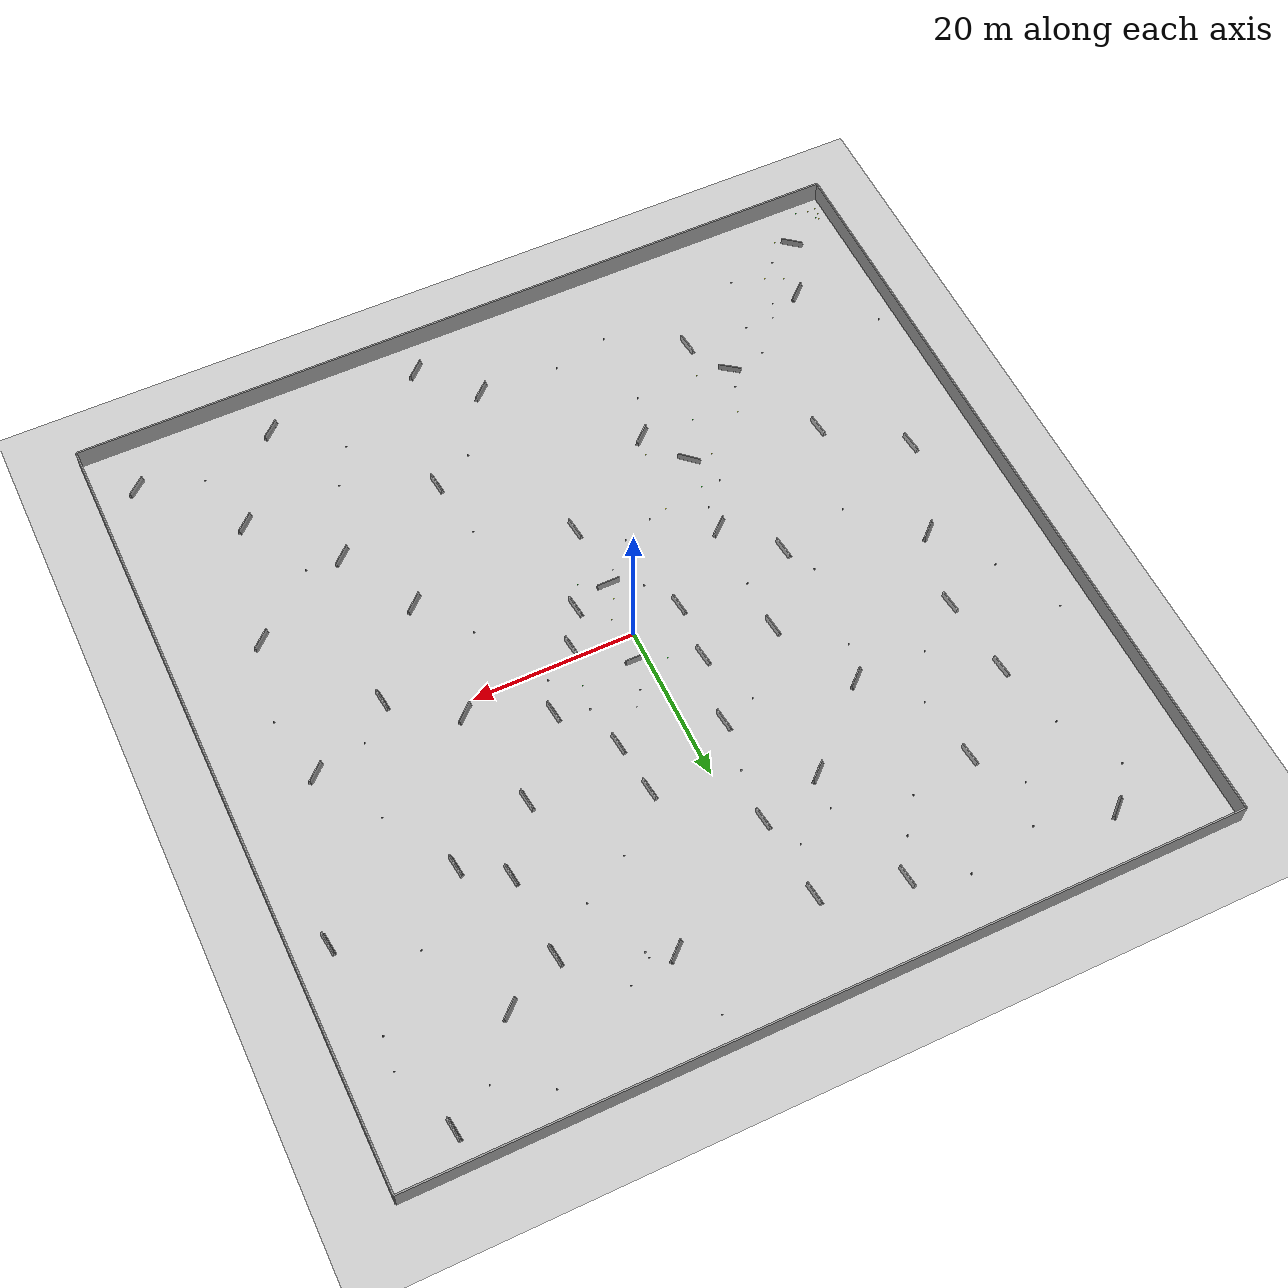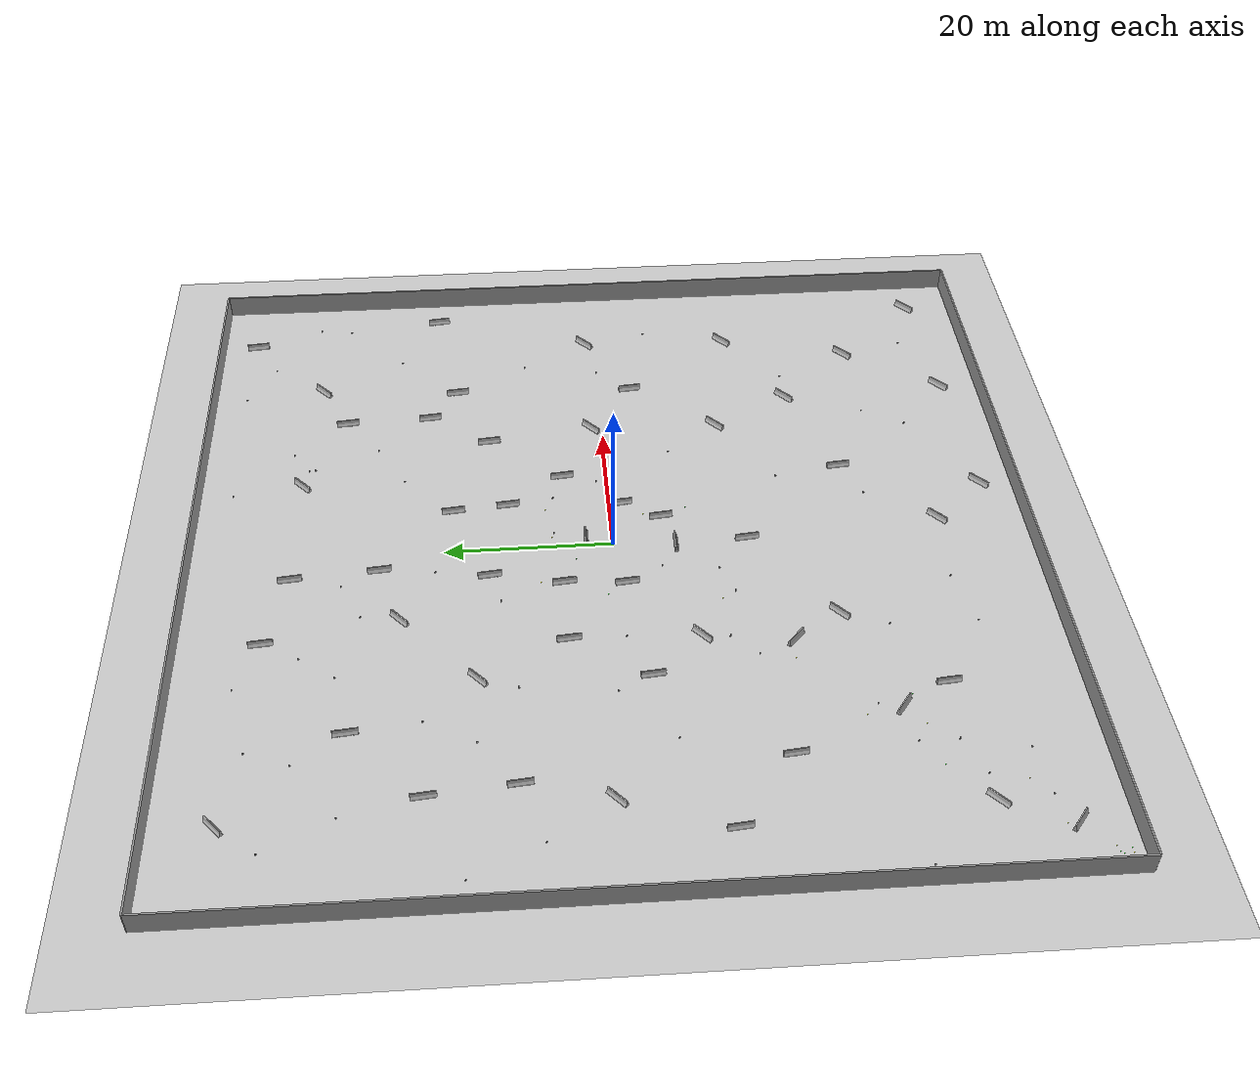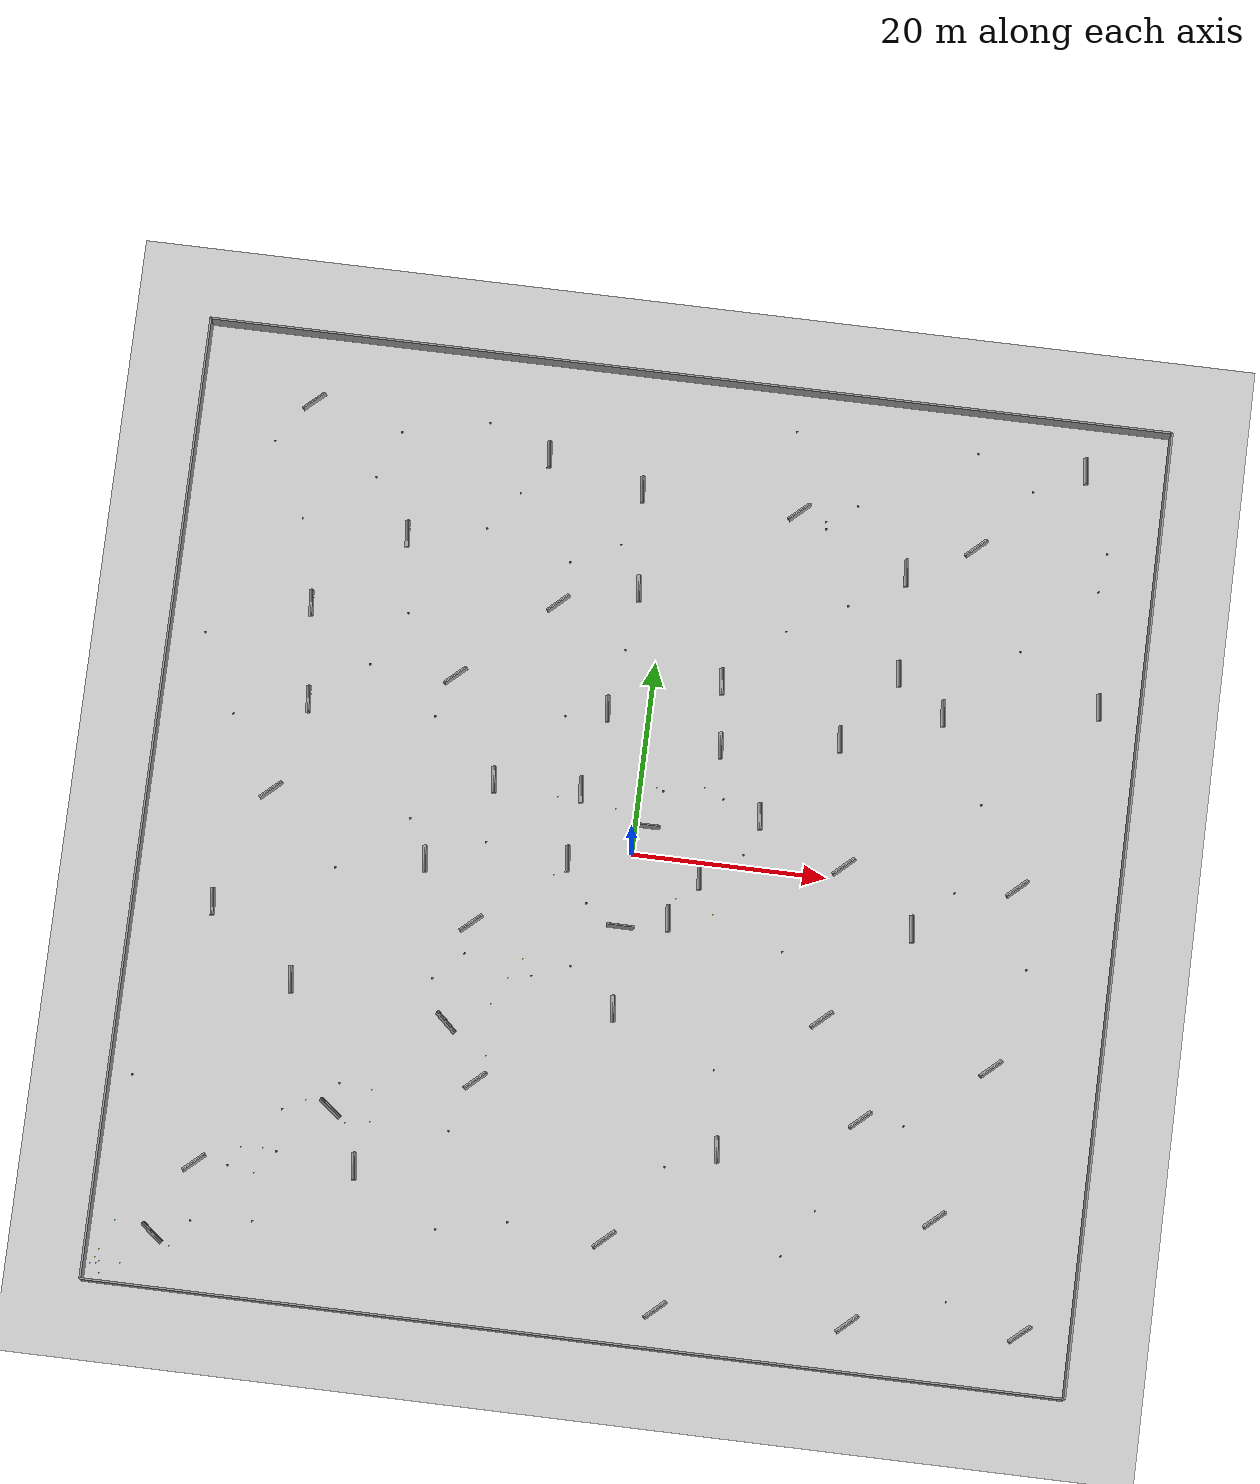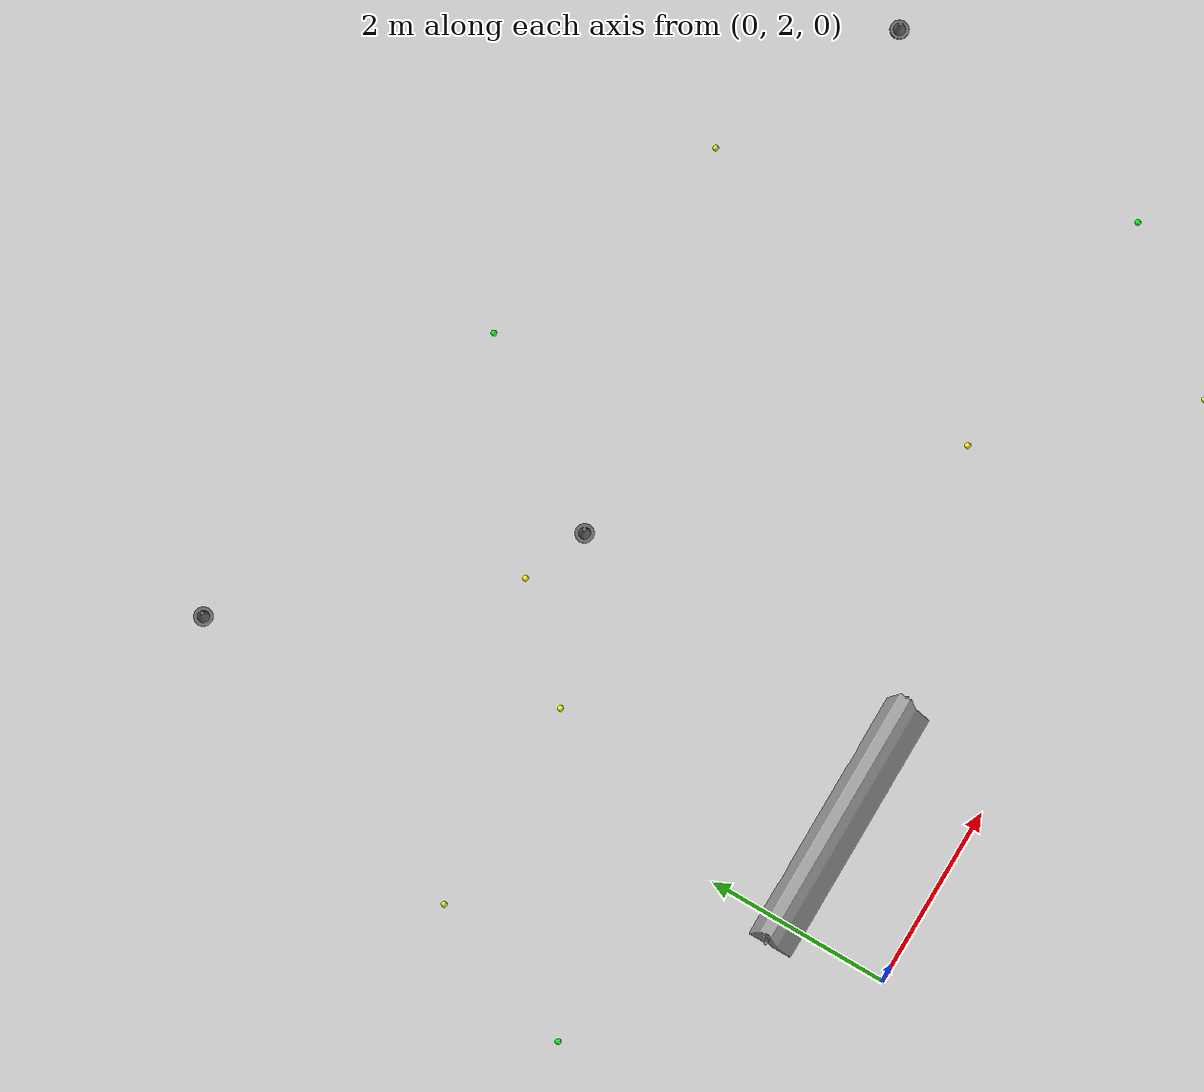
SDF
<sdf version="1.6">
 <world name="default">
  <scene><ambient>0.4 0.4 0.4 1</ambient><background>0.25 0.25 0.25 1</background><shadows>0</shadows></scene>
  <light name="some_light" type="directional">
   <diffuse>0.7 0.7 0.7 0</diffuse>
   <specular>1 1 1 0</specular>
   <direction>-1 -1 -1</direction>
  </light>
  <gravity>0 0 -9.8</gravity>
  <magnetic_field>6e-06 2.3e-05 -4.2e-05</magnetic_field>
  <atmosphere type="adiabatic"/>
  <physics name="default_physics" default="0" type="ode">
   <max_step_size>0.001</max_step_size>
   <real_time_factor>1</real_time_factor>
   <real_time_update_rate>1000</real_time_update_rate>
  </physics>
  <spherical_coordinates>
   <surface_model>EARTH_WGS84</surface_model>
   <latitude_deg>0</latitude_deg>
   <longitude_deg>0</longitude_deg>
   <elevation>0</elevation>
   <heading_deg>0</heading_deg>
  </spherical_coordinates>
  <model name="ground_plane">
   <static>1</static>
   <link name="link">
    <collision name="collision">
     <geometry><plane><normal>0 0 1</normal><size>100 100</size></plane></geometry>
     <surface>
      <contact><collide_bitmask>65535</collide_bitmask></contact>
      <friction><ode><mu>100</mu><mu2>50</mu2></ode></friction>
     </surface>
    </collision>
    <visual name="visual">
     <cast_shadows>0</cast_shadows>
     <geometry><plane><normal>0 0 1</normal><size>100 100</size></plane></geometry>
     <material>
      <script><uri>file://media/materials/scripts/gazebo.material</uri><name>Gazebo/Grey</name></script>
     </material>
    </visual>
   </link>
   <pose>-0.027205 0.027206 0 0 -0 0</pose>
  </model>
  <model name="road_barricade">
   <static>0</static>
   <link name="ball">
    <pose>0 0 0.1 0 -0 0</pose>
    <collision name="collision">
     <geometry><mesh><uri>model://road_barricade/road_barricade.dae</uri></mesh></geometry>
     <surface>
      <bounce><restitution_coefficient>0.2</restitution_coefficient><threshold>100</threshold></bounce>
      <contact><ode><max_vel>10</max_vel></ode></contact>
     </surface>
    </collision>
    <visual name="visual">
     <geometry><mesh><uri>model://road_barricade/road_barricade.dae</uri></mesh></geometry>
    </visual>
    <inertial>
     <mass>200</mass>
     <inertia>
      <ixx>0.075021</ixx>
      <ixy>3e-06</ixy>
      <ixz>-2.9e-05</ixz>
      <iyy>0.89513</iyy>
      <iyz>-0.00631</iyz>
      <izz>0.847779</izz>
     </inertia>
    </inertial>
   </link>
   <pose>1.1409 3.17936 -0.100005 -8.2e-05 -3.4e-05 0.001621</pose>
  </model>
  <model name="road_barricade_0">
   <static>0</static>
   <link name="ball">
    <pose>0 0 0.1 0 -0 0</pose>
    <collision name="collision">
     <geometry><mesh><uri>model://road_barricade/road_barricade.dae</uri></mesh></geometry>
     <surface>
      <bounce><restitution_coefficient>0.2</restitution_coefficient><threshold>100</threshold></bounce>
      <contact><ode><max_vel>10</max_vel></ode></contact>
     </surface>
    </collision>
    <visual name="visual">
     <geometry><mesh><uri>model://road_barricade/road_barricade.dae</uri></mesh></geometry>
    </visual>
    <inertial>
     <mass>200</mass>
     <inertia>
      <ixx>0.075021</ixx>
      <ixy>3e-06</ixy>
      <ixz>-2.9e-05</ixz>
      <iyy>0.89513</iyy>
      <iyz>-0.00631</iyz>
      <izz>0.847779</izz>
     </inertia>
    </inertial>
   </link>
   <pose>7.13108 -1.37862 -0.100008 -0.000216 0.000102 -1.46697</pose>
  </model>
  <model name="road_barricade_0_clone">
   <static>0</static>
   <link name="ball">
    <pose>0 0 0.1 0 -0 0</pose>
    <collision name="collision">
     <geometry><mesh><uri>model://road_barricade/road_barricade.dae</uri></mesh></geometry>
     <surface>
      <bounce><restitution_coefficient>0.2</restitution_coefficient><threshold>100</threshold></bounce>
      <contact><ode><max_vel>10</max_vel></ode></contact>
     </surface>
    </collision>
    <visual name="visual">
     <geometry><mesh><uri>model://road_barricade/road_barricade.dae</uri></mesh></geometry>
    </visual>
    <inertial>
     <mass>200</mass>
     <inertia>
      <ixx>0.075021</ixx>
      <ixy>3e-06</ixy>
      <ixz>-2.9e-05</ixz>
      <iyy>0.89513</iyy>
      <iyz>-0.00631</iyz>
      <izz>0.847779</izz>
     </inertia>
    </inertial>
   </link>
   <pose>4.48179 -6.07193 -0.100005 -8.2e-05 -3.4e-05 -1.46463</pose>
  </model>
  <model name="road_barricade_0_clone_0">
   <static>0</static>
   <link name="ball">
    <pose>0 0 0.1 0 -0 0</pose>
    <collision name="collision">
     <geometry><mesh><uri>model://road_barricade/road_barricade.dae</uri></mesh></geometry>
     <surface>
      <bounce><restitution_coefficient>0.2</restitution_coefficient><threshold>100</threshold></bounce>
      <contact><ode><max_vel>10</max_vel></ode></contact>
     </surface>
    </collision>
    <visual name="visual">
     <geometry><mesh><uri>model://road_barricade/road_barricade.dae</uri></mesh></geometry>
    </visual>
    <inertial>
     <mass>200</mass>
     <inertia>
      <ixx>0.075021</ixx>
      <ixy>3e-06</ixy>
      <ixz>-2.9e-05</ixz>
      <iyy>0.89513</iyy>
      <iyz>-0.00631</iyz>
      <izz>0.847779</izz>
     </inertia>
    </inertial>
   </link>
   <pose>-6.49143 -1.22101 -0.100008 -0.000216 0.000102 -1.46632</pose>
  </model>
  <model name="road_barricade_0_clone_1">
   <static>0</static>
   <link name="ball">
    <pose>0 0 0.1 0 -0 0</pose>
    <collision name="collision">
     <geometry><mesh><uri>model://road_barricade/road_barricade.dae</uri></mesh></geometry>
     <surface>
      <bounce><restitution_coefficient>0.2</restitution_coefficient><threshold>100</threshold></bounce>
      <contact><ode><max_vel>10</max_vel></ode></contact>
     </surface>
    </collision>
    <visual name="visual">
     <geometry><mesh><uri>model://road_barricade/road_barricade.dae</uri></mesh></geometry>
    </visual>
    <inertial>
     <mass>200</mass>
     <inertia>
      <ixx>0.075021</ixx>
      <ixy>3e-06</ixy>
      <ixz>-2.9e-05</ixz>
      <iyy>0.89513</iyy>
      <iyz>-0.00631</iyz>
      <izz>0.847779</izz>
     </inertia>
    </inertial>
   </link>
   <pose>-5.98707 6.08351 -0.100006 8.4e-05 3.9e-05 -1.46616</pose>
  </model>
  <model name="road_barricade_0_clone_2">
   <static>0</static>
   <link name="ball">
    <pose>0 0 0.1 0 -0 0</pose>
    <collision name="collision">
     <geometry><mesh><uri>model://road_barricade/road_barricade.dae</uri></mesh></geometry>
     <surface>
      <bounce><restitution_coefficient>0.2</restitution_coefficient><threshold>100</threshold></bounce>
      <contact><ode><max_vel>10</max_vel></ode></contact>
     </surface>
    </collision>
    <visual name="visual">
     <geometry><mesh><uri>model://road_barricade/road_barricade.dae</uri></mesh></geometry>
    </visual>
    <inertial>
     <mass>200</mass>
     <inertia>
      <ixx>0.075021</ixx>
      <ixy>3e-06</ixy>
      <ixz>-2.9e-05</ixz>
      <iyy>0.89513</iyy>
      <iyz>-0.00631</iyz>
      <izz>0.847779</izz>
     </inertia>
    </inertial>
   </link>
   <pose>-4.32031 14.7364 -0.100006 8.4e-05 3.9e-05 -1.46481</pose>
  </model>
  <model name="road_barricade_0_clone_3">
   <static>0</static>
   <link name="ball">
    <pose>0 0 0.1 0 -0 0</pose>
    <collision name="collision">
     <geometry><mesh><uri>model://road_barricade/road_barricade.dae</uri></mesh></geometry>
     <surface>
      <bounce><restitution_coefficient>0.2</restitution_coefficient><threshold>100</threshold></bounce>
      <contact><ode><max_vel>10</max_vel></ode></contact>
     </surface>
    </collision>
    <visual name="visual">
     <geometry><mesh><uri>model://road_barricade/road_barricade.dae</uri></mesh></geometry>
    </visual>
    <inertial>
     <mass>200</mass>
     <inertia>
      <ixx>0.075021</ixx>
      <ixy>3e-06</ixy>
      <ixz>-2.9e-05</ixz>
      <iyy>0.89513</iyy>
      <iyz>-0.00631</iyz>
      <izz>0.847779</izz>
     </inertia>
    </inertial>
   </link>
   <pose>7.67213 12.341 -0.100006 8.4e-05 3.9e-05 -1.46612</pose>
  </model>
  <model name="road_barricade_0_clone_4">
   <static>0</static>
   <link name="ball">
    <pose>0 0 0.1 0 -0 0</pose>
    <collision name="collision">
     <geometry><mesh><uri>model://road_barricade/road_barricade.dae</uri></mesh></geometry>
     <surface>
      <bounce><restitution_coefficient>0.2</restitution_coefficient><threshold>100</threshold></bounce>
      <contact><ode><max_vel>10</max_vel></ode></contact>
     </surface>
    </collision>
    <visual name="visual">
     <geometry><mesh><uri>model://road_barricade/road_barricade.dae</uri></mesh></geometry>
    </visual>
    <inertial>
     <mass>200</mass>
     <inertia>
      <ixx>0.075021</ixx>
      <ixy>3e-06</ixy>
      <ixz>-2.9e-05</ixz>
      <iyy>0.89513</iyy>
      <iyz>-0.00631</iyz>
      <izz>0.847779</izz>
     </inertia>
    </inertial>
   </link>
   <pose>12.5399 5.53979 -0.100013 -0.000189 3.8e-05 -1.46609</pose>
  </model>
  <model name="road_barricade_0_clone_5">
   <static>0</static>
   <link name="ball">
    <pose>0 0 0.1 0 -0 0</pose>
    <collision name="collision">
     <geometry><mesh><uri>model://road_barricade/road_barricade.dae</uri></mesh></geometry>
     <surface>
      <bounce><restitution_coefficient>0.2</restitution_coefficient><threshold>100</threshold></bounce>
      <contact><ode><max_vel>10</max_vel></ode></contact>
     </surface>
    </collision>
    <visual name="visual">
     <geometry><mesh><uri>model://road_barricade/road_barricade.dae</uri></mesh></geometry>
    </visual>
    <inertial>
     <mass>200</mass>
     <inertia>
      <ixx>0.075021</ixx>
      <ixy>3e-06</ixy>
      <ixz>-2.9e-05</ixz>
      <iyy>0.89513</iyy>
      <iyz>-0.00631</iyz>
      <izz>0.847779</izz>
     </inertia>
    </inertial>
   </link>
   <pose>29.3899 -4.14525 -0.100006 8.4e-05 3.9e-05 -1.46605</pose>
  </model>
  <model name="road_barricade_0_clone_6">
   <static>0</static>
   <link name="ball">
    <pose>0 0 0.1 0 -0 0</pose>
    <collision name="collision">
     <geometry><mesh><uri>model://road_barricade/road_barricade.dae</uri></mesh></geometry>
     <surface>
      <bounce><restitution_coefficient>0.2</restitution_coefficient><threshold>100</threshold></bounce>
      <contact><ode><max_vel>10</max_vel></ode></contact>
     </surface>
    </collision>
    <visual name="visual">
     <geometry><mesh><uri>model://road_barricade/road_barricade.dae</uri></mesh></geometry>
    </visual>
    <inertial>
     <mass>200</mass>
     <inertia>
      <ixx>0.075021</ixx>
      <ixy>3e-06</ixy>
      <ixz>-2.9e-05</ixz>
      <iyy>0.89513</iyy>
      <iyz>-0.00631</iyz>
      <izz>0.847779</izz>
     </inertia>
    </inertial>
   </link>
   <pose>12.2567 -29.0407 -0.100005 -8.2e-05 -3.4e-05 -1.46628</pose>
  </model>
  <model name="road_barricade_0_clone_7">
   <static>0</static>
   <link name="ball">
    <pose>0 0 0.1 0 -0 0</pose>
    <collision name="collision">
     <geometry><mesh><uri>model://road_barricade/road_barricade.dae</uri></mesh></geometry>
     <surface>
      <bounce><restitution_coefficient>0.2</restitution_coefficient><threshold>100</threshold></bounce>
      <contact><ode><max_vel>10</max_vel></ode></contact>
     </surface>
    </collision>
    <visual name="visual">
     <geometry><mesh><uri>model://road_barricade/road_barricade.dae</uri></mesh></geometry>
    </visual>
    <inertial>
     <mass>200</mass>
     <inertia>
      <ixx>0.075021</ixx>
      <ixy>3e-06</ixy>
      <ixz>-2.9e-05</ixz>
      <iyy>0.89513</iyy>
      <iyz>-0.00631</iyz>
      <izz>0.847779</izz>
     </inertia>
    </inertial>
   </link>
   <pose>0.000859 -16 -0.100005 -8.2e-05 -3.4e-05 -1.46484</pose>
  </model>
  <model name="road_barricade_0_clone_8">
   <static>0</static>
   <link name="ball">
    <pose>0 0 0.1 0 -0 0</pose>
    <collision name="collision">
     <geometry><mesh><uri>model://road_barricade/road_barricade.dae</uri></mesh></geometry>
     <surface>
      <bounce><restitution_coefficient>0.2</restitution_coefficient><threshold>100</threshold></bounce>
      <contact><ode><max_vel>10</max_vel></ode></contact>
     </surface>
    </collision>
    <visual name="visual">
     <geometry><mesh><uri>model://road_barricade/road_barricade.dae</uri></mesh></geometry>
    </visual>
    <inertial>
     <mass>200</mass>
     <inertia>
      <ixx>0.075021</ixx>
      <ixy>3e-06</ixy>
      <ixz>-2.9e-05</ixz>
      <iyy>0.89513</iyy>
      <iyz>-0.00631</iyz>
      <izz>0.847779</izz>
     </inertia>
    </inertial>
   </link>
   <pose>-24.1662 -35.1747 -0.100008 -0.000216 0.000102 -1.46626</pose>
  </model>
  <model name="road_barricade_0_clone_9">
   <static>0</static>
   <link name="ball">
    <pose>0 0 0.1 0 -0 0</pose>
    <collision name="collision">
     <geometry><mesh><uri>model://road_barricade/road_barricade.dae</uri></mesh></geometry>
     <surface>
      <bounce><restitution_coefficient>0.2</restitution_coefficient><threshold>100</threshold></bounce>
      <contact><ode><max_vel>10</max_vel></ode></contact>
     </surface>
    </collision>
    <visual name="visual">
     <geometry><mesh><uri>model://road_barricade/road_barricade.dae</uri></mesh></geometry>
    </visual>
    <inertial>
     <mass>200</mass>
     <inertia>
      <ixx>0.075021</ixx>
      <ixy>3e-06</ixy>
      <ixz>-2.9e-05</ixz>
      <iyy>0.89513</iyy>
      <iyz>-0.00631</iyz>
      <izz>0.847779</izz>
     </inertia>
    </inertial>
   </link>
   <pose>-32.9995 -17.0001 -0.100012 0 -2e-05 -1.46626</pose>
  </model>
  <model name="road_barricade_0_clone_10">
   <static>0</static>
   <link name="ball">
    <pose>0 0 0.1 0 -0 0</pose>
    <collision name="collision">
     <geometry><mesh><uri>model://road_barricade/road_barricade.dae</uri></mesh></geometry>
     <surface>
      <bounce><restitution_coefficient>0.2</restitution_coefficient><threshold>100</threshold></bounce>
      <contact><ode><max_vel>10</max_vel></ode></contact>
     </surface>
    </collision>
    <visual name="visual">
     <geometry><mesh><uri>model://road_barricade/road_barricade.dae</uri></mesh></geometry>
    </visual>
    <inertial>
     <mass>200</mass>
     <inertia>
      <ixx>0.075021</ixx>
      <ixy>3e-06</ixy>
      <ixz>-2.9e-05</ixz>
      <iyy>0.89513</iyy>
      <iyz>-0.00631</iyz>
      <izz>0.847779</izz>
     </inertia>
    </inertial>
   </link>
   <pose>-27.0883 30.3993 -0.100012 -0 -2e-05 -1.46478</pose>
  </model>
  <model name="road_barricade_0_clone_11">
   <static>0</static>
   <link name="ball">
    <pose>0 0 0.1 0 -0 0</pose>
    <collision name="collision">
     <geometry><mesh><uri>model://road_barricade/road_barricade.dae</uri></mesh></geometry>
     <surface>
      <bounce><restitution_coefficient>0.2</restitution_coefficient><threshold>100</threshold></bounce>
      <contact><ode><max_vel>10</max_vel></ode></contact>
     </surface>
    </collision>
    <visual name="visual">
     <geometry><mesh><uri>model://road_barricade/road_barricade.dae</uri></mesh></geometry>
    </visual>
    <inertial>
     <mass>200</mass>
     <inertia>
      <ixx>0.075021</ixx>
      <ixy>3e-06</ixy>
      <ixz>-2.9e-05</ixz>
      <iyy>0.89513</iyy>
      <iyz>-0.00631</iyz>
      <izz>0.847779</izz>
     </inertia>
    </inertial>
   </link>
   <pose>30.0005 18.4505 -0.100008 -0.000216 0.000102 -1.46598</pose>
  </model>
  <model name="road_barricade_0_clone_12">
   <static>0</static>
   <link name="ball">
    <pose>0 0 0.1 0 -0 0</pose>
    <collision name="collision">
     <geometry><mesh><uri>model://road_barricade/road_barricade.dae</uri></mesh></geometry>
     <surface>
      <bounce><restitution_coefficient>0.2</restitution_coefficient><threshold>100</threshold></bounce>
      <contact><ode><max_vel>10</max_vel></ode></contact>
     </surface>
    </collision>
    <visual name="visual">
     <geometry><mesh><uri>model://road_barricade/road_barricade.dae</uri></mesh></geometry>
    </visual>
    <inertial>
     <mass>200</mass>
     <inertia>
      <ixx>0.075021</ixx>
      <ixy>3e-06</ixy>
      <ixz>-2.9e-05</ixz>
      <iyy>0.89513</iyy>
      <iyz>-0.00631</iyz>
      <izz>0.847779</izz>
     </inertia>
    </inertial>
   </link>
   <pose>24.5443 32.5648 -0.100012 -0 -2e-05 -1.46619</pose>
  </model>
  <model name="road_barricade_0_clone_13">
   <static>0</static>
   <link name="ball">
    <pose>0 0 0.1 0 -0 0</pose>
    <collision name="collision">
     <geometry><mesh><uri>model://road_barricade/road_barricade.dae</uri></mesh></geometry>
     <surface>
      <bounce><restitution_coefficient>0.2</restitution_coefficient><threshold>100</threshold></bounce>
      <contact><ode><max_vel>10</max_vel></ode></contact>
     </surface>
    </collision>
    <visual name="visual">
     <geometry><mesh><uri>model://road_barricade/road_barricade.dae</uri></mesh></geometry>
    </visual>
    <inertial>
     <mass>200</mass>
     <inertia>
      <ixx>0.075021</ixx>
      <ixy>3e-06</ixy>
      <ixz>-2.9e-05</ixz>
      <iyy>0.89513</iyy>
      <iyz>-0.00631</iyz>
      <izz>0.847779</izz>
     </inertia>
    </inertial>
   </link>
   <pose>-3.54562 37.9995 -0.100006 8.4e-05 3.9e-05 -1.46473</pose>
  </model>
  <model name="road_barricade_0_clone_14">
   <static>0</static>
   <link name="ball">
    <pose>0 0 0.1 0 -0 0</pose>
    <collision name="collision">
     <geometry><mesh><uri>model://road_barricade/road_barricade.dae</uri></mesh></geometry>
     <surface>
      <bounce><restitution_coefficient>0.2</restitution_coefficient><threshold>100</threshold></bounce>
      <contact><ode><max_vel>10</max_vel></ode></contact>
     </surface>
    </collision>
    <visual name="visual">
     <geometry><mesh><uri>model://road_barricade/road_barricade.dae</uri></mesh></geometry>
    </visual>
    <inertial>
     <mass>200</mass>
     <inertia>
      <ixx>0.075021</ixx>
      <ixy>3e-06</ixy>
      <ixz>-2.9e-05</ixz>
      <iyy>0.89513</iyy>
      <iyz>-0.00631</iyz>
      <izz>0.847779</izz>
     </inertia>
    </inertial>
   </link>
   <pose>25 21.9999 -0.100008 -0.000216 0.000102 -1.46501</pose>
  </model>
  <model name="road_barricade_0_clone_15">
   <static>0</static>
   <link name="ball">
    <pose>0 0 0.1 0 -0 0</pose>
    <collision name="collision">
     <geometry><mesh><uri>model://road_barricade/road_barricade.dae</uri></mesh></geometry>
     <surface>
      <bounce><restitution_coefficient>0.2</restitution_coefficient><threshold>100</threshold></bounce>
      <contact><ode><max_vel>10</max_vel></ode></contact>
     </surface>
    </collision>
    <visual name="visual">
     <geometry><mesh><uri>model://road_barricade/road_barricade.dae</uri></mesh></geometry>
    </visual>
    <inertial>
     <mass>200</mass>
     <inertia>
      <ixx>0.075021</ixx>
      <ixy>3e-06</ixy>
      <ixz>-2.9e-05</ixz>
      <iyy>0.89513</iyy>
      <iyz>-0.00631</iyz>
      <izz>0.847779</izz>
     </inertia>
    </inertial>
   </link>
   <pose>-2.67367 27.6337 -0.100005 -8.2e-05 -3.4e-05 -1.46461</pose>
  </model>
  <model name="road_barricade_0_clone_16">
   <static>0</static>
   <link name="ball">
    <pose>0 0 0.1 0 -0 0</pose>
    <collision name="collision">
     <geometry><mesh><uri>model://road_barricade/road_barricade.dae</uri></mesh></geometry>
     <surface>
      <bounce><restitution_coefficient>0.2</restitution_coefficient><threshold>100</threshold></bounce>
      <contact><ode><max_vel>10</max_vel></ode></contact>
     </surface>
    </collision>
    <visual name="visual">
     <geometry><mesh><uri>model://road_barricade/road_barricade.dae</uri></mesh></geometry>
    </visual>
    <inertial>
     <mass>200</mass>
     <inertia>
      <ixx>0.075021</ixx>
      <ixy>3e-06</ixy>
      <ixz>-2.9e-05</ixz>
      <iyy>0.89513</iyy>
      <iyz>-0.00631</iyz>
      <izz>0.847779</izz>
     </inertia>
    </inertial>
   </link>
   <pose>7.00075 19 -0.100006 8.4e-05 3.9e-05 -1.46485</pose>
  </model>
  <model name="road_barricade_0_clone_17">
   <static>0</static>
   <link name="ball">
    <pose>0 0 0.1 0 -0 0</pose>
    <collision name="collision">
     <geometry><mesh><uri>model://road_barricade/road_barricade.dae</uri></mesh></geometry>
     <surface>
      <bounce><restitution_coefficient>0.2</restitution_coefficient><threshold>100</threshold></bounce>
      <contact><ode><max_vel>10</max_vel></ode></contact>
     </surface>
    </collision>
    <visual name="visual">
     <geometry><mesh><uri>model://road_barricade/road_barricade.dae</uri></mesh></geometry>
    </visual>
    <inertial>
     <mass>200</mass>
     <inertia>
      <ixx>0.075021</ixx>
      <ixy>3e-06</ixy>
      <ixz>-2.9e-05</ixz>
      <iyy>0.89513</iyy>
      <iyz>-0.00631</iyz>
      <izz>0.847779</izz>
     </inertia>
    </inertial>
   </link>
   <pose>-35.9998 21.9999 -0.100012 0 -2e-05 -1.46623</pose>
  </model>
  <model name="road_barricade_0_clone_18">
   <static>0</static>
   <link name="ball">
    <pose>0 0 0.1 0 -0 0</pose>
    <collision name="collision">
     <geometry><mesh><uri>model://road_barricade/road_barricade.dae</uri></mesh></geometry>
     <surface>
      <bounce><restitution_coefficient>0.2</restitution_coefficient><threshold>100</threshold></bounce>
      <contact><ode><max_vel>10</max_vel></ode></contact>
     </surface>
    </collision>
    <visual name="visual">
     <geometry><mesh><uri>model://road_barricade/road_barricade.dae</uri></mesh></geometry>
    </visual>
    <inertial>
     <mass>200</mass>
     <inertia>
      <ixx>0.075021</ixx>
      <ixy>3e-06</ixy>
      <ixz>-2.9e-05</ixz>
      <iyy>0.89513</iyy>
      <iyz>-0.00631</iyz>
      <izz>0.847779</izz>
     </inertia>
    </inertial>
   </link>
   <pose>-13.5578 40.5121 -0.100008 -0.000216 0.000102 -1.46643</pose>
  </model>
  <model name="road_barricade_0_clone_19">
   <static>0</static>
   <link name="ball">
    <pose>0 0 0.1 0 -0 0</pose>
    <collision name="collision">
     <geometry><mesh><uri>model://road_barricade/road_barricade.dae</uri></mesh></geometry>
     <surface>
      <bounce><restitution_coefficient>0.2</restitution_coefficient><threshold>100</threshold></bounce>
      <contact><ode><max_vel>10</max_vel></ode></contact>
     </surface>
    </collision>
    <visual name="visual">
     <geometry><mesh><uri>model://road_barricade/road_barricade.dae</uri></mesh></geometry>
    </visual>
    <inertial>
     <mass>200</mass>
     <inertia>
      <ixx>0.075021</ixx>
      <ixy>3e-06</ixy>
      <ixz>-2.9e-05</ixz>
      <iyy>0.89513</iyy>
      <iyz>-0.00631</iyz>
      <izz>0.847779</izz>
     </inertia>
    </inertial>
   </link>
   <pose>-41.9988 -10.0002 -0.100006 8.4e-05 3.9e-05 -1.46633</pose>
  </model>
  <model name="road_barricade_0_clone_20">
   <static>0</static>
   <link name="ball">
    <pose>0 0 0.1 0 -0 0</pose>
    <collision name="collision">
     <geometry><mesh><uri>model://road_barricade/road_barricade.dae</uri></mesh></geometry>
     <surface>
      <bounce><restitution_coefficient>0.2</restitution_coefficient><threshold>100</threshold></bounce>
      <contact><ode><max_vel>10</max_vel></ode></contact>
     </surface>
    </collision>
    <visual name="visual">
     <geometry><mesh><uri>model://road_barricade/road_barricade.dae</uri></mesh></geometry>
    </visual>
    <inertial>
     <mass>200</mass>
     <inertia>
      <ixx>0.075021</ixx>
      <ixy>3e-06</ixy>
      <ixz>-2.9e-05</ixz>
      <iyy>0.89513</iyy>
      <iyz>-0.00631</iyz>
      <izz>0.847779</izz>
     </inertia>
    </inertial>
   </link>
   <pose>-20.999 -3.00012 -0.100005 -8.2e-05 -3.4e-05 -1.46598</pose>
  </model>
  <model name="road_barricade_0_clone_21">
   <static>0</static>
   <link name="ball">
    <pose>0 0 0.1 0 -0 0</pose>
    <collision name="collision">
     <geometry><mesh><uri>model://road_barricade/road_barricade.dae</uri></mesh></geometry>
     <surface>
      <bounce><restitution_coefficient>0.2</restitution_coefficient><threshold>100</threshold></bounce>
      <contact><ode><max_vel>10</max_vel></ode></contact>
     </surface>
    </collision>
    <visual name="visual">
     <geometry><mesh><uri>model://road_barricade/road_barricade.dae</uri></mesh></geometry>
    </visual>
    <inertial>
     <mass>200</mass>
     <inertia>
      <ixx>0.075021</ixx>
      <ixy>3e-06</ixy>
      <ixz>-2.9e-05</ixz>
      <iyy>0.89513</iyy>
      <iyz>-0.00631</iyz>
      <izz>0.847779</izz>
     </inertia>
    </inertial>
   </link>
   <pose>-35.0004 11.9998 -0.100013 -0.000189 3.8e-05 -1.46626</pose>
  </model>
  <model name="road_barricade_0_clone_22">
   <static>0</static>
   <link name="ball">
    <pose>0 0 0.1 0 -0 0</pose>
    <collision name="collision">
     <geometry><mesh><uri>model://road_barricade/road_barricade.dae</uri></mesh></geometry>
     <surface>
      <bounce><restitution_coefficient>0.2</restitution_coefficient><threshold>100</threshold></bounce>
      <contact><ode><max_vel>10</max_vel></ode></contact>
     </surface>
    </collision>
    <visual name="visual">
     <geometry><mesh><uri>model://road_barricade/road_barricade.dae</uri></mesh></geometry>
    </visual>
    <inertial>
     <mass>200</mass>
     <inertia>
      <ixx>0.075021</ixx>
      <ixy>3e-06</ixy>
      <ixz>-2.9e-05</ixz>
      <iyy>0.89513</iyy>
      <iyz>-0.00631</iyz>
      <izz>0.847779</izz>
     </inertia>
    </inertial>
   </link>
   <pose>-14.9999 5.99986 -0.100012 0 -2e-05 -1.46629</pose>
  </model>
  <model name="road_barricade_0_clone_23">
   <static>0</static>
   <link name="ball">
    <pose>0 0 0.1 0 -0 0</pose>
    <collision name="collision">
     <geometry><mesh><uri>model://road_barricade/road_barricade.dae</uri></mesh></geometry>
     <surface>
      <bounce><restitution_coefficient>0.2</restitution_coefficient><threshold>100</threshold></bounce>
      <contact><ode><max_vel>10</max_vel></ode></contact>
     </surface>
    </collision>
    <visual name="visual">
     <geometry><mesh><uri>model://road_barricade/road_barricade.dae</uri></mesh></geometry>
    </visual>
    <inertial>
     <mass>200</mass>
     <inertia>
      <ixx>0.075021</ixx>
      <ixy>3e-06</ixy>
      <ixz>-2.9e-05</ixz>
      <iyy>0.89513</iyy>
      <iyz>-0.00631</iyz>
      <izz>0.847779</izz>
     </inertia>
    </inertial>
   </link>
   <pose>19.7959 14.481 -0.100012 -0 -2e-05 -1.46649</pose>
  </model>
  <model name="road_barricade_0_clone_24">
   <static>0</static>
   <link name="ball">
    <pose>0 0 0.1 0 -0 0</pose>
    <collision name="collision">
     <geometry><mesh><uri>model://road_barricade/road_barricade.dae</uri></mesh></geometry>
     <surface>
      <bounce><restitution_coefficient>0.2</restitution_coefficient><threshold>100</threshold></bounce>
      <contact><ode><max_vel>10</max_vel></ode></contact>
     </surface>
    </collision>
    <visual name="visual">
     <geometry><mesh><uri>model://road_barricade/road_barricade.dae</uri></mesh></geometry>
    </visual>
    <inertial>
     <mass>200</mass>
     <inertia>
      <ixx>0.075021</ixx>
      <ixy>3e-06</ixy>
      <ixz>-2.9e-05</ixz>
      <iyy>0.89513</iyy>
      <iyz>-0.00631</iyz>
      <izz>0.847779</izz>
     </inertia>
    </inertial>
   </link>
   <pose>45.8278 21.0197 -0.100006 8.4e-05 3.9e-05 -1.46608</pose>
  </model>
  <model name="road_barricade_0_clone_25">
   <static>0</static>
   <link name="ball">
    <pose>0 0 0.1 0 -0 0</pose>
    <collision name="collision">
     <geometry><mesh><uri>model://road_barricade/road_barricade.dae</uri></mesh></geometry>
     <surface>
      <bounce><restitution_coefficient>0.2</restitution_coefficient><threshold>100</threshold></bounce>
      <contact><ode><max_vel>10</max_vel></ode></contact>
     </surface>
    </collision>
    <visual name="visual">
     <geometry><mesh><uri>model://road_barricade/road_barricade.dae</uri></mesh></geometry>
    </visual>
    <inertial>
     <mass>200</mass>
     <inertia>
      <ixx>0.075021</ixx>
      <ixy>3e-06</ixy>
      <ixz>-2.9e-05</ixz>
      <iyy>0.89513</iyy>
      <iyz>-0.00631</iyz>
      <izz>0.847779</izz>
     </inertia>
    </inertial>
   </link>
   <pose>41.7454 45.4874 -0.100008 -0.000216 0.000102 -1.46636</pose>
  </model>
  <model name="road_barricade_0_clone_26">
   <static>0</static>
   <link name="ball">
    <pose>0 0 0.1 0 -0 0</pose>
    <collision name="collision">
     <geometry><mesh><uri>model://road_barricade/road_barricade.dae</uri></mesh></geometry>
     <surface>
      <bounce><restitution_coefficient>0.2</restitution_coefficient><threshold>100</threshold></bounce>
      <contact><ode><max_vel>10</max_vel></ode></contact>
     </surface>
    </collision>
    <visual name="visual">
     <geometry><mesh><uri>model://road_barricade/road_barricade.dae</uri></mesh></geometry>
    </visual>
    <inertial>
     <mass>200</mass>
     <inertia>
      <ixx>0.075021</ixx>
      <ixy>3e-06</ixy>
      <ixz>-2.9e-05</ixz>
      <iyy>0.89513</iyy>
      <iyz>-0.00631</iyz>
      <izz>0.847779</izz>
     </inertia>
    </inertial>
   </link>
   <pose>31.415 36.0462 -0.100006 8.4e-05 3.9e-05 -2.40343</pose>
  </model>
  <model name="road_barricade_0_clone_26_clone">
   <static>0</static>
   <link name="ball">
    <pose>0 0 0.1 0 -0 0</pose>
    <collision name="collision">
     <geometry><mesh><uri>model://road_barricade/road_barricade.dae</uri></mesh></geometry>
     <surface>
      <bounce><restitution_coefficient>0.2</restitution_coefficient><threshold>100</threshold></bounce>
      <contact><ode><max_vel>10</max_vel></ode></contact>
     </surface>
    </collision>
    <visual name="visual">
     <geometry><mesh><uri>model://road_barricade/road_barricade.dae</uri></mesh></geometry>
    </visual>
    <inertial>
     <mass>200</mass>
     <inertia>
      <ixx>0.075021</ixx>
      <ixy>3e-06</ixy>
      <ixz>-2.9e-05</ixz>
      <iyy>0.89513</iyy>
      <iyz>-0.00631</iyz>
      <izz>0.847779</izz>
     </inertia>
    </inertial>
   </link>
   <pose>12.8505 37.6268 -0.100005 -8.2e-05 -3.4e-05 -2.40259</pose>
  </model>
  <model name="road_barricade_0_clone_26_clone_0">
   <static>0</static>
   <link name="ball">
    <pose>0 0 0.1 0 -0 0</pose>
    <collision name="collision">
     <geometry><mesh><uri>model://road_barricade/road_barricade.dae</uri></mesh></geometry>
     <surface>
      <bounce><restitution_coefficient>0.2</restitution_coefficient><threshold>100</threshold></bounce>
      <contact><ode><max_vel>10</max_vel></ode></contact>
     </surface>
    </collision>
    <visual name="visual">
     <geometry><mesh><uri>model://road_barricade/road_barricade.dae</uri></mesh></geometry>
    </visual>
    <inertial>
     <mass>200</mass>
     <inertia>
      <ixx>0.075021</ixx>
      <ixy>3e-06</ixy>
      <ixz>-2.9e-05</ixz>
      <iyy>0.89513</iyy>
      <iyz>-0.00631</iyz>
      <izz>0.847779</izz>
     </inertia>
    </inertial>
   </link>
   <pose>39.0007 -17.4367 -0.100006 8.4e-05 3.9e-05 -2.40326</pose>
  </model>
  <model name="road_barricade_0_clone_26_clone_1">
   <static>0</static>
   <link name="ball">
    <pose>0 0 0.1 0 -0 0</pose>
    <collision name="collision">
     <geometry><mesh><uri>model://road_barricade/road_barricade.dae</uri></mesh></geometry>
     <surface>
      <bounce><restitution_coefficient>0.2</restitution_coefficient><threshold>100</threshold></bounce>
      <contact><ode><max_vel>10</max_vel></ode></contact>
     </surface>
    </collision>
    <visual name="visual">
     <geometry><mesh><uri>model://road_barricade/road_barricade.dae</uri></mesh></geometry>
    </visual>
    <inertial>
     <mass>200</mass>
     <inertia>
      <ixx>0.075021</ixx>
      <ixy>3e-06</ixy>
      <ixz>-2.9e-05</ixz>
      <iyy>0.89513</iyy>
      <iyz>-0.00631</iyz>
      <izz>0.847779</izz>
     </inertia>
    </inertial>
   </link>
   <pose>35.0405 -33.4391 -0.100013 0.00027 -6.3e-05 -2.40278</pose>
  </model>
  <model name="road_barricade_0_clone_26_clone_2">
   <static>0</static>
   <link name="ball">
    <pose>0 0 0.1 0 -0 0</pose>
    <collision name="collision">
     <geometry><mesh><uri>model://road_barricade/road_barricade.dae</uri></mesh></geometry>
     <surface>
      <bounce><restitution_coefficient>0.2</restitution_coefficient><threshold>100</threshold></bounce>
      <contact><ode><max_vel>10</max_vel></ode></contact>
     </surface>
    </collision>
    <visual name="visual">
     <geometry><mesh><uri>model://road_barricade/road_barricade.dae</uri></mesh></geometry>
    </visual>
    <inertial>
     <mass>200</mass>
     <inertia>
      <ixx>0.075021</ixx>
      <ixy>3e-06</ixy>
      <ixz>-2.9e-05</ixz>
      <iyy>0.89513</iyy>
      <iyz>-0.00631</iyz>
      <izz>0.847779</izz>
     </inertia>
    </inertial>
   </link>
   <pose>21.6931 1.41213 -0.100006 8.4e-05 3.9e-05 -2.40275</pose>
  </model>
  <model name="road_barricade_0_clone_26_clone_3">
   <static>0</static>
   <link name="ball">
    <pose>0 0 0.1 0 -0 0</pose>
    <collision name="collision">
     <geometry><mesh><uri>model://road_barricade/road_barricade.dae</uri></mesh></geometry>
     <surface>
      <bounce><restitution_coefficient>0.2</restitution_coefficient><threshold>100</threshold></bounce>
      <contact><ode><max_vel>10</max_vel></ode></contact>
     </surface>
    </collision>
    <visual name="visual">
     <geometry><mesh><uri>model://road_barricade/road_barricade.dae</uri></mesh></geometry>
    </visual>
    <inertial>
     <mass>200</mass>
     <inertia>
      <ixx>0.075021</ixx>
      <ixy>3e-06</ixy>
      <ixz>-2.9e-05</ixz>
      <iyy>0.89513</iyy>
      <iyz>-0.00631</iyz>
      <izz>0.847779</izz>
     </inertia>
    </inertial>
   </link>
   <pose>39.5898 1.29322 -0.100006 8.4e-05 3.9e-05 -2.40306</pose>
  </model>
  <model name="road_barricade_0_clone_26_clone_4">
   <static>0</static>
   <link name="ball">
    <pose>0 0 0.1 0 -0 0</pose>
    <collision name="collision">
     <geometry><mesh><uri>model://road_barricade/road_barricade.dae</uri></mesh></geometry>
     <surface>
      <bounce><restitution_coefficient>0.2</restitution_coefficient><threshold>100</threshold></bounce>
      <contact><ode><max_vel>10</max_vel></ode></contact>
     </surface>
    </collision>
    <visual name="visual">
     <geometry><mesh><uri>model://road_barricade/road_barricade.dae</uri></mesh></geometry>
    </visual>
    <inertial>
     <mass>200</mass>
     <inertia>
      <ixx>0.075021</ixx>
      <ixy>3e-06</ixy>
      <ixz>-2.9e-05</ixz>
      <iyy>0.89513</iyy>
      <iyz>-0.00631</iyz>
      <izz>0.847779</izz>
     </inertia>
    </inertial>
   </link>
   <pose>44.9425 -43.9144 -0.100013 -0.000189 3.8e-05 -2.42554</pose>
  </model>
  <model name="road_barricade_0_clone_26_clone_5">
   <static>0</static>
   <link name="ball">
    <pose>0 0 0.1 0 -0 0</pose>
    <collision name="collision">
     <geometry><mesh><uri>model://road_barricade/road_barricade.dae</uri></mesh></geometry>
     <surface>
      <bounce><restitution_coefficient>0.2</restitution_coefficient><threshold>100</threshold></bounce>
      <contact><ode><max_vel>10</max_vel></ode></contact>
     </surface>
    </collision>
    <visual name="visual">
     <geometry><mesh><uri>model://road_barricade/road_barricade.dae</uri></mesh></geometry>
    </visual>
    <inertial>
     <mass>200</mass>
     <inertia>
      <ixx>0.075021</ixx>
      <ixy>3e-06</ixy>
      <ixz>-2.9e-05</ixz>
      <iyy>0.89513</iyy>
      <iyz>-0.00631</iyz>
      <izz>0.847779</izz>
     </inertia>
    </inertial>
   </link>
   <pose>-40.3517 -36.7623 -0.100013 0.00027 -6.3e-05 -2.40286</pose>
  </model>
  <model name="road_barricade_0_clone_26_clone_6">
   <static>0</static>
   <link name="ball">
    <pose>0 0 0.1 0 -0 0</pose>
    <collision name="collision">
     <geometry><mesh><uri>model://road_barricade/road_barricade.dae</uri></mesh></geometry>
     <surface>
      <bounce><restitution_coefficient>0.2</restitution_coefficient><threshold>100</threshold></bounce>
      <contact><ode><max_vel>10</max_vel></ode></contact>
     </surface>
    </collision>
    <visual name="visual">
     <geometry><mesh><uri>model://road_barricade/road_barricade.dae</uri></mesh></geometry>
    </visual>
    <inertial>
     <mass>200</mass>
     <inertia>
      <ixx>0.075021</ixx>
      <ixy>3e-06</ixy>
      <ixz>-2.9e-05</ixz>
      <iyy>0.89513</iyy>
      <iyz>-0.00631</iyz>
      <izz>0.847779</izz>
     </inertia>
    </inertial>
   </link>
   <pose>2.00051 -39.4666 -0.100013 0.00027 -6.3e-05 -2.40246</pose>
  </model>
  <model name="road_barricade_0_clone_26_clone_7">
   <static>0</static>
   <link name="ball">
    <pose>0 0 0.1 0 -0 0</pose>
    <collision name="collision">
     <geometry><mesh><uri>model://road_barricade/road_barricade.dae</uri></mesh></geometry>
     <surface>
      <bounce><restitution_coefficient>0.2</restitution_coefficient><threshold>100</threshold></bounce>
      <contact><ode><max_vel>10</max_vel></ode></contact>
     </surface>
    </collision>
    <visual name="visual">
     <geometry><mesh><uri>model://road_barricade/road_barricade.dae</uri></mesh></geometry>
    </visual>
    <inertial>
     <mass>200</mass>
     <inertia>
      <ixx>0.075021</ixx>
      <ixy>3e-06</ixy>
      <ixz>-2.9e-05</ixz>
      <iyy>0.89513</iyy>
      <iyz>-0.00631</iyz>
      <izz>0.847779</izz>
     </inertia>
    </inertial>
   </link>
   <pose>-12.9996 -24.9999 -0.100006 8.4e-05 3.9e-05 -2.40246</pose>
  </model>
  <model name="road_barricade_0_clone_26_clone_8">
   <static>0</static>
   <link name="ball">
    <pose>0 0 0.1 0 -0 0</pose>
    <collision name="collision">
     <geometry><mesh><uri>model://road_barricade/road_barricade.dae</uri></mesh></geometry>
     <surface>
      <bounce><restitution_coefficient>0.2</restitution_coefficient><threshold>100</threshold></bounce>
      <contact><ode><max_vel>10</max_vel></ode></contact>
     </surface>
    </collision>
    <visual name="visual">
     <geometry><mesh><uri>model://road_barricade/road_barricade.dae</uri></mesh></geometry>
    </visual>
    <inertial>
     <mass>200</mass>
     <inertia>
      <ixx>0.075021</ixx>
      <ixy>3e-06</ixy>
      <ixz>-2.9e-05</ixz>
      <iyy>0.89513</iyy>
      <iyz>-0.00631</iyz>
      <izz>0.847779</izz>
     </inertia>
    </inertial>
   </link>
   <pose>-15.4553 -8.99599 -0.100013 0.00027 -6.3e-05 -2.40883</pose>
  </model>
  <model name="road_barricade_0_clone_26_clone_9">
   <static>0</static>
   <link name="ball">
    <pose>0 0 0.1 0 -0 0</pose>
    <collision name="collision">
     <geometry><mesh><uri>model://road_barricade/road_barricade.dae</uri></mesh></geometry>
     <surface>
      <bounce><restitution_coefficient>0.2</restitution_coefficient><threshold>100</threshold></bounce>
      <contact><ode><max_vel>10</max_vel></ode></contact>
     </surface>
    </collision>
    <visual name="visual">
     <geometry><mesh><uri>model://road_barricade/road_barricade.dae</uri></mesh></geometry>
    </visual>
    <inertial>
     <mass>200</mass>
     <inertia>
      <ixx>0.075021</ixx>
      <ixy>3e-06</ixy>
      <ixz>-2.9e-05</ixz>
      <iyy>0.89513</iyy>
      <iyz>-0.00631</iyz>
      <izz>0.847779</izz>
     </inertia>
    </inertial>
   </link>
   <pose>-37.5667 2.18742 -0.100005 -8.2e-05 -3.4e-05 -2.40249</pose>
  </model>
  <model name="road_barricade_0_clone_26_clone_10">
   <static>0</static>
   <link name="ball">
    <pose>0 0 0.1 0 -0 0</pose>
    <collision name="collision">
     <geometry><mesh><uri>model://road_barricade/road_barricade.dae</uri></mesh></geometry>
     <surface>
      <bounce><restitution_coefficient>0.2</restitution_coefficient><threshold>100</threshold></bounce>
      <contact><ode><max_vel>10</max_vel></ode></contact>
     </surface>
    </collision>
    <visual name="visual">
     <geometry><mesh><uri>model://road_barricade/road_barricade.dae</uri></mesh></geometry>
    </visual>
    <inertial>
     <mass>200</mass>
     <inertia>
      <ixx>0.075021</ixx>
      <ixy>3e-06</ixy>
      <ixz>-2.9e-05</ixz>
      <iyy>0.89513</iyy>
      <iyz>-0.00631</iyz>
      <izz>0.847779</izz>
     </inertia>
    </inertial>
   </link>
   <pose>-10.7284 25.1002 -0.100006 8.4e-05 3.9e-05 -2.40273</pose>
  </model>
  <model name="road_barricade_0_clone_26_clone_11">
   <static>0</static>
   <link name="ball">
    <pose>0 0 0.1 0 -0 0</pose>
    <collision name="collision">
     <geometry><mesh><uri>model://road_barricade/road_barricade.dae</uri></mesh></geometry>
     <surface>
      <bounce><restitution_coefficient>0.2</restitution_coefficient><threshold>100</threshold></bounce>
      <contact><ode><max_vel>10</max_vel></ode></contact>
     </surface>
    </collision>
    <visual name="visual">
     <geometry><mesh><uri>model://road_barricade/road_barricade.dae</uri></mesh></geometry>
    </visual>
    <inertial>
     <mass>200</mass>
     <inertia>
      <ixx>0.075021</ixx>
      <ixy>3e-06</ixy>
      <ixz>-2.9e-05</ixz>
      <iyy>0.89513</iyy>
      <iyz>-0.00631</iyz>
      <izz>0.847779</izz>
     </inertia>
    </inertial>
   </link>
   <pose>-20.2903 16.2901 -0.100005 -8.2e-05 -3.4e-05 -2.40209</pose>
  </model>
  <model name="road_barricade_0_clone_26_clone_12">
   <static>0</static>
   <link name="ball">
    <pose>0 0 0.1 0 -0 0</pose>
    <collision name="collision">
     <geometry><mesh><uri>model://road_barricade/road_barricade.dae</uri></mesh></geometry>
     <surface>
      <bounce><restitution_coefficient>0.2</restitution_coefficient><threshold>100</threshold></bounce>
      <contact><ode><max_vel>10</max_vel></ode></contact>
     </surface>
    </collision>
    <visual name="visual">
     <geometry><mesh><uri>model://road_barricade/road_barricade.dae</uri></mesh></geometry>
    </visual>
    <inertial>
     <mass>200</mass>
     <inertia>
      <ixx>0.075021</ixx>
      <ixy>3e-06</ixy>
      <ixz>-2.9e-05</ixz>
      <iyy>0.89513</iyy>
      <iyz>-0.00631</iyz>
      <izz>0.847779</izz>
     </inertia>
    </inertial>
   </link>
   <pose>-38.429 43.1406 -0.100006 8.4e-05 3.9e-05 -2.40286</pose>
  </model>
  <model name="road_barricade_0_clone_26_clone_13">
   <static>0</static>
   <link name="ball">
    <pose>0 0 0.1 0 -0 0</pose>
    <collision name="collision">
     <geometry><mesh><uri>model://road_barricade/road_barricade.dae</uri></mesh></geometry>
     <surface>
      <bounce><restitution_coefficient>0.2</restitution_coefficient><threshold>100</threshold></bounce>
      <contact><ode><max_vel>10</max_vel></ode></contact>
     </surface>
    </collision>
    <visual name="visual">
     <geometry><mesh><uri>model://road_barricade/road_barricade.dae</uri></mesh></geometry>
    </visual>
    <inertial>
     <mass>200</mass>
     <inertia>
      <ixx>0.075021</ixx>
      <ixy>3e-06</ixy>
      <ixz>-2.9e-05</ixz>
      <iyy>0.89513</iyy>
      <iyz>-0.00631</iyz>
      <izz>0.847779</izz>
     </inertia>
    </inertial>
   </link>
   <pose>21.2766 -14.5218 -0.100006 8.4e-05 3.9e-05 -2.40353</pose>
  </model>
  <model name="road_barricade_0_clone_26_clone_14">
   <static>0</static>
   <link name="ball">
    <pose>0 0 0.1 0 -0 0</pose>
    <collision name="collision">
     <geometry><mesh><uri>model://road_barricade/road_barricade.dae</uri></mesh></geometry>
     <surface>
      <bounce><restitution_coefficient>0.2</restitution_coefficient><threshold>100</threshold></bounce>
      <contact><ode><max_vel>10</max_vel></ode></contact>
     </surface>
    </collision>
    <visual name="visual">
     <geometry><mesh><uri>model://road_barricade/road_barricade.dae</uri></mesh></geometry>
    </visual>
    <inertial>
     <mass>200</mass>
     <inertia>
      <ixx>0.075021</ixx>
      <ixy>3e-06</ixy>
      <ixz>-2.9e-05</ixz>
      <iyy>0.89513</iyy>
      <iyz>-0.00631</iyz>
      <izz>0.847779</izz>
     </inertia>
    </inertial>
   </link>
   <pose>26.3911 -24.243 -0.100013 0.00027 -6.3e-05 -2.40361</pose>
  </model>
  <model name="road_barricade_0_clone_26_clone_15">
   <static>0</static>
   <link name="ball">
    <pose>0 0 0.1 0 -0 0</pose>
    <collision name="collision">
     <geometry><mesh><uri>model://road_barricade/road_barricade.dae</uri></mesh></geometry>
     <surface>
      <bounce><restitution_coefficient>0.2</restitution_coefficient><threshold>100</threshold></bounce>
      <contact><ode><max_vel>10</max_vel></ode></contact>
     </surface>
    </collision>
    <visual name="visual">
     <geometry><mesh><uri>model://road_barricade/road_barricade.dae</uri></mesh></geometry>
    </visual>
    <inertial>
     <mass>200</mass>
     <inertia>
      <ixx>0.075021</ixx>
      <ixy>3e-06</ixy>
      <ixz>-2.9e-05</ixz>
      <iyy>0.89513</iyy>
      <iyz>-0.00631</iyz>
      <izz>0.847779</izz>
     </inertia>
    </inertial>
   </link>
   <pose>27.4504 -44.9998 -0.100013 0.00027 -6.3e-05 -2.40155</pose>
  </model>
  <model name="road_barricade_0_clone_26_clone_16">
   <static>0</static>
   <link name="ball">
    <pose>0 0 0.1 0 -0 0</pose>
    <collision name="collision">
     <geometry><mesh><uri>model://road_barricade/road_barricade.dae</uri></mesh></geometry>
     <surface>
      <bounce><restitution_coefficient>0.2</restitution_coefficient><threshold>100</threshold></bounce>
      <contact><ode><max_vel>10</max_vel></ode></contact>
     </surface>
    </collision>
    <visual name="visual">
     <geometry><mesh><uri>model://road_barricade/road_barricade.dae</uri></mesh></geometry>
    </visual>
    <inertial>
     <mass>200</mass>
     <inertia>
      <ixx>0.075021</ixx>
      <ixy>3e-06</ixy>
      <ixz>-2.9e-05</ixz>
      <iyy>0.89513</iyy>
      <iyz>-0.00631</iyz>
      <izz>0.847779</izz>
     </inertia>
    </inertial>
   </link>
   <pose>7.98792 -45.9425 -0.100013 0.00027 -6.3e-05 -2.39687</pose>
  </model>
  <model name="pylon">
   <static>0</static>
   <link name="ball">
    <pose>0 0 0 1.5708 -0 0</pose>
    <collision name="collision"><geometry><mesh><uri>model://pylon/pylon.dae</uri></mesh></geometry></collision>
    <visual name="visual"><geometry><mesh><uri>model://pylon/pylon.dae</uri></mesh></geometry></visual>
    <inertial>
     <mass>4.5</mass>
     <inertia><ixx>1</ixx><ixy>0</ixy><ixz>0</ixz><iyy>1</iyy><iyz>0</iyz><izz>1</izz></inertia>
    </inertial>
   </link>
   <pose>-25.9044 22.2306 0.134267 -5e-06 1e-06 0.002957</pose>
  </model>
  <model name="pylon_0">
   <static>0</static>
   <link name="ball">
    <pose>0 0 0 1.5708 -0 0</pose>
    <collision name="collision"><geometry><mesh><uri>model://pylon/pylon.dae</uri></mesh></geometry></collision>
    <visual name="visual"><geometry><mesh><uri>model://pylon/pylon.dae</uri></mesh></geometry></visual>
    <inertial>
     <mass>4.5</mass>
     <inertia><ixx>1</ixx><ixy>0</ixy><ixz>0</ixz><iyy>1</iyy><iyz>0</iyz><izz>1</izz></inertia>
    </inertial>
   </link>
   <pose>18.7796 38.9897 0.134258 -6e-06 2e-06 0.003014</pose>
  </model>
  <model name="pylon_1">
   <static>0</static>
   <link name="ball">
    <pose>0 0 0 1.5708 -0 0</pose>
    <collision name="collision"><geometry><mesh><uri>model://pylon/pylon.dae</uri></mesh></geometry></collision>
    <visual name="visual"><geometry><mesh><uri>model://pylon/pylon.dae</uri></mesh></geometry></visual>
    <inertial>
     <mass>4.5</mass>
     <inertia><ixx>1</ixx><ixy>0</ixy><ixz>0</ixz><iyy>1</iyy><iyz>0</iyz><izz>1</izz></inertia>
    </inertial>
   </link>
   <pose>15.6801 36.9584 0.134267 -4e-06 -0 0.003044</pose>
  </model>
  <model name="pylon_2">
   <static>0</static>
   <link name="ball">
    <pose>0 0 0.1 1.5708 -0 0</pose>
    <collision name="collision"><geometry><mesh><uri>model://pylon/pylon.dae</uri></mesh></geometry></collision>
    <visual name="visual"><geometry><mesh><uri>model://pylon/pylon.dae</uri></mesh></geometry></visual>
    <inertial>
     <mass>4.5</mass>
     <inertia><ixx>1</ixx><ixy>0</ixy><ixz>0</ixz><iyy>1</iyy><iyz>0</iyz><izz>1</izz></inertia>
    </inertial>
   </link>
   <pose>15.8036 36.2173 0.034267 -4e-06 0 0.000579</pose>
  </model>
  <model name="pylon_4">
   <static>0</static>
   <link name="ball">
    <pose>0 0 0.1 1.5708 -0 0</pose>
    <collision name="collision"><geometry><mesh><uri>model://pylon/pylon.dae</uri></mesh></geometry></collision>
    <visual name="visual"><geometry><mesh><uri>model://pylon/pylon.dae</uri></mesh></geometry></visual>
    <inertial>
     <mass>4.5</mass>
     <inertia><ixx>1</ixx><ixy>0</ixy><ixz>0</ixz><iyy>1</iyy><iyz>0</iyz><izz>1</izz></inertia>
    </inertial>
   </link>
   <pose>37.1473 -41.5739 0.034267 -3e-06 -2e-06 0.000773</pose>
  </model>
  <model name="pylon_5">
   <static>0</static>
   <link name="ball">
    <pose>0 0 0.1 1.5708 -0 0</pose>
    <collision name="collision"><geometry><mesh><uri>model://pylon/pylon.dae</uri></mesh></geometry></collision>
    <visual name="visual"><geometry><mesh><uri>model://pylon/pylon.dae</uri></mesh></geometry></visual>
    <inertial>
     <mass>4.5</mass>
     <inertia><ixx>1</ixx><ixy>0</ixy><ixz>0</ixz><iyy>1</iyy><iyz>0</iyz><izz>1</izz></inertia>
    </inertial>
   </link>
   <pose>30.8747 -24.3745 0.034267 -3e-06 2e-06 0.000786</pose>
  </model>
  <model name="pylon_6">
   <static>0</static>
   <link name="ball">
    <pose>0 0 0.1 1.5708 -0 0</pose>
    <collision name="collision"><geometry><mesh><uri>model://pylon/pylon.dae</uri></mesh></geometry></collision>
    <visual name="visual"><geometry><mesh><uri>model://pylon/pylon.dae</uri></mesh></geometry></visual>
    <inertial>
     <mass>4.5</mass>
     <inertia><ixx>1</ixx><ixy>0</ixy><ixz>0</ixz><iyy>1</iyy><iyz>0</iyz><izz>1</izz></inertia>
    </inertial>
   </link>
   <pose>41.47 -6.88464 0.034266 -8e-06 6e-06 0.000625</pose>
  </model>
  <model name="pylon_7">
   <static>0</static>
   <link name="ball">
    <pose>0 0 0.1 1.5708 -0 0</pose>
    <collision name="collision"><geometry><mesh><uri>model://pylon/pylon.dae</uri></mesh></geometry></collision>
    <visual name="visual"><geometry><mesh><uri>model://pylon/pylon.dae</uri></mesh></geometry></visual>
    <inertial>
     <mass>4.5</mass>
     <inertia><ixx>1</ixx><ixy>0</ixy><ixz>0</ixz><iyy>1</iyy><iyz>0</iyz><izz>1</izz></inertia>
    </inertial>
   </link>
   <pose>33.2822 0.043768 0.034267 0 -4e-06 0.000718</pose>
  </model>
  <model name="pylon_8">
   <static>0</static>
   <link name="ball">
    <pose>0 0 0.1 1.5708 -0 0</pose>
    <collision name="collision"><geometry><mesh><uri>model://pylon/pylon.dae</uri></mesh></geometry></collision>
    <visual name="visual"><geometry><mesh><uri>model://pylon/pylon.dae</uri></mesh></geometry></visual>
    <inertial>
     <mass>4.5</mass>
     <inertia><ixx>1</ixx><ixy>0</ixy><ixz>0</ixz><iyy>1</iyy><iyz>0</iyz><izz>1</izz></inertia>
    </inertial>
   </link>
   <pose>16.4667 -8.09136 0.034268 -1e-05 -6e-06 0.000573</pose>
  </model>
  <model name="pylon_9">
   <static>0</static>
   <link name="ball">
    <pose>0 0 0.1 1.5708 -0 0</pose>
    <collision name="collision"><geometry><mesh><uri>model://pylon/pylon.dae</uri></mesh></geometry></collision>
    <visual name="visual"><geometry><mesh><uri>model://pylon/pylon.dae</uri></mesh></geometry></visual>
    <inertial>
     <mass>4.5</mass>
     <inertia><ixx>1</ixx><ixy>0</ixy><ixz>0</ixz><iyy>1</iyy><iyz>0</iyz><izz>1</izz></inertia>
    </inertial>
   </link>
   <pose>7.20543 -31.4177 0.034267 -4e-06 -1e-06 0.000532</pose>
  </model>
  <model name="pylon_10">
   <static>0</static>
   <link name="ball">
    <pose>0 0 0.1 1.5708 -0 0</pose>
    <collision name="collision"><geometry><mesh><uri>model://pylon/pylon.dae</uri></mesh></geometry></collision>
    <visual name="visual"><geometry><mesh><uri>model://pylon/pylon.dae</uri></mesh></geometry></visual>
    <inertial>
     <mass>4.5</mass>
     <inertia><ixx>1</ixx><ixy>0</ixy><ixz>0</ixz><iyy>1</iyy><iyz>0</iyz><izz>1</izz></inertia>
    </inertial>
   </link>
   <pose>-15.163 -40.57 0.034267 -3e-06 2e-06 0.000344</pose>
  </model>
  <model name="pylon_11">
   <static>0</static>
   <link name="ball">
    <pose>0 0 0.1 1.5708 -0 0</pose>
    <collision name="collision"><geometry><mesh><uri>model://pylon/pylon.dae</uri></mesh></geometry></collision>
    <visual name="visual"><geometry><mesh><uri>model://pylon/pylon.dae</uri></mesh></geometry></visual>
    <inertial>
     <mass>4.5</mass>
     <inertia><ixx>1</ixx><ixy>0</ixy><ixz>0</ixz><iyy>1</iyy><iyz>0</iyz><izz>1</izz></inertia>
    </inertial>
   </link>
   <pose>-7.97762 -38.9509 0.034267 -4e-06 -1e-06 0.000556</pose>
  </model>
  <model name="pylon_12">
   <static>0</static>
   <link name="ball">
    <pose>0 0 0.1 1.5708 -0 0</pose>
    <collision name="collision"><geometry><mesh><uri>model://pylon/pylon.dae</uri></mesh></geometry></collision>
    <visual name="visual"><geometry><mesh><uri>model://pylon/pylon.dae</uri></mesh></geometry></visual>
    <inertial>
     <mass>4.5</mass>
     <inertia><ixx>1</ixx><ixy>0</ixy><ixz>0</ixz><iyy>1</iyy><iyz>0</iyz><izz>1</izz></inertia>
    </inertial>
   </link>
   <pose>-15.0436 -30.4315 0.034258 -3e-06 3e-06 0.000532</pose>
  </model>
  <model name="pylon_13">
   <static>0</static>
   <link name="ball">
    <pose>0 0 0.1 1.5708 -0 0</pose>
    <collision name="collision"><geometry><mesh><uri>model://pylon/pylon.dae</uri></mesh></geometry></collision>
    <visual name="visual"><geometry><mesh><uri>model://pylon/pylon.dae</uri></mesh></geometry></visual>
    <inertial>
     <mass>4.5</mass>
     <inertia><ixx>1</ixx><ixy>0</ixy><ixz>0</ixz><iyy>1</iyy><iyz>0</iyz><izz>1</izz></inertia>
    </inertial>
   </link>
   <pose>-32.1524 -30.2648 0.034267 -6e-06 2e-06 0.000665</pose>
  </model>
  <model name="pylon_14">
   <static>0</static>
   <link name="ball">
    <pose>0 0 0.1 1.5708 -0 0</pose>
    <collision name="collision"><geometry><mesh><uri>model://pylon/pylon.dae</uri></mesh></geometry></collision>
    <visual name="visual"><geometry><mesh><uri>model://pylon/pylon.dae</uri></mesh></geometry></visual>
    <inertial>
     <mass>4.5</mass>
     <inertia><ixx>1</ixx><ixy>0</ixy><ixz>0</ixz><iyy>1</iyy><iyz>0</iyz><izz>1</izz></inertia>
    </inertial>
   </link>
   <pose>-33.7166 -41.9736 0.034267 -3e-06 -4e-06 0.000548</pose>
  </model>
  <model name="pylon_15">
   <static>0</static>
   <link name="ball">
    <pose>0 0 0.1 1.5708 -0 0</pose>
    <collision name="collision"><geometry><mesh><uri>model://pylon/pylon.dae</uri></mesh></geometry></collision>
    <visual name="visual"><geometry><mesh><uri>model://pylon/pylon.dae</uri></mesh></geometry></visual>
    <inertial>
     <mass>4.5</mass>
     <inertia><ixx>1</ixx><ixy>0</ixy><ixz>0</ixz><iyy>1</iyy><iyz>0</iyz><izz>1</izz></inertia>
    </inertial>
   </link>
   <pose>-47.7479 -28.6107 0.034267 -4e-06 -3e-06 0.000706</pose>
  </model>
  <model name="pylon_16">
   <static>0</static>
   <link name="ball">
    <pose>0 0 0.1 1.5708 -0 0</pose>
    <collision name="collision"><geometry><mesh><uri>model://pylon/pylon.dae</uri></mesh></geometry></collision>
    <visual name="visual"><geometry><mesh><uri>model://pylon/pylon.dae</uri></mesh></geometry></visual>
    <inertial>
     <mass>4.5</mass>
     <inertia><ixx>1</ixx><ixy>0</ixy><ixz>0</ixz><iyy>1</iyy><iyz>0</iyz><izz>1</izz></inertia>
    </inertial>
   </link>
   <pose>-18.681 -15.1141 0.034267 -4e-06 5e-06 0.000475</pose>
  </model>
  <model name="pylon_16_clone">
   <static>0</static>
   <link name="ball">
    <pose>0 0 0.1 1.5708 -0 0</pose>
    <collision name="collision"><geometry><mesh><uri>model://pylon/pylon.dae</uri></mesh></geometry></collision>
    <visual name="visual"><geometry><mesh><uri>model://pylon/pylon.dae</uri></mesh></geometry></visual>
    <inertial>
     <mass>4.5</mass>
     <inertia><ixx>1</ixx><ixy>0</ixy><ixz>0</ixz><iyy>1</iyy><iyz>0</iyz><izz>1</izz></inertia>
    </inertial>
   </link>
   <pose>-4.80428 -12.1547 0.034267 -4e-06 -1e-06 0.000473</pose>
  </model>
  <model name="pylon_16_clone_0">
   <static>0</static>
   <link name="ball">
    <pose>0 0 0.1 1.5708 -0 0</pose>
    <collision name="collision"><geometry><mesh><uri>model://pylon/pylon.dae</uri></mesh></geometry></collision>
    <visual name="visual"><geometry><mesh><uri>model://pylon/pylon.dae</uri></mesh></geometry></visual>
    <inertial>
     <mass>4.5</mass>
     <inertia><ixx>1</ixx><ixy>0</ixy><ixz>0</ixz><iyy>1</iyy><iyz>0</iyz><izz>1</izz></inertia>
    </inertial>
   </link>
   <pose>-3.99997 -5.52501 0.034267 -3e-06 -0 0.000481</pose>
  </model>
  <model name="pylon_16_clone_1">
   <static>0</static>
   <link name="ball">
    <pose>0 0 0.1 1.5708 -0 0</pose>
    <collision name="collision"><geometry><mesh><uri>model://pylon/pylon.dae</uri></mesh></geometry></collision>
    <visual name="visual"><geometry><mesh><uri>model://pylon/pylon.dae</uri></mesh></geometry></visual>
    <inertial>
     <mass>4.5</mass>
     <inertia><ixx>1</ixx><ixy>0</ixy><ixz>0</ixz><iyy>1</iyy><iyz>0</iyz><izz>1</izz></inertia>
    </inertial>
   </link>
   <pose>-15 -0.517432 0.034267 -4e-06 -1e-06 0.000543</pose>
  </model>
  <model name="pylon_16_clone_2">
   <static>0</static>
   <link name="ball">
    <pose>0 0 0.1 1.5708 -0 0</pose>
    <collision name="collision"><geometry><mesh><uri>model://pylon/pylon.dae</uri></mesh></geometry></collision>
    <visual name="visual"><geometry><mesh><uri>model://pylon/pylon.dae</uri></mesh></geometry></visual>
    <inertial>
     <mass>4.5</mass>
     <inertia><ixx>1</ixx><ixy>0</ixy><ixz>0</ixz><iyy>1</iyy><iyz>0</iyz><izz>1</izz></inertia>
    </inertial>
   </link>
   <pose>-23 0.999889 0.034258 -3e-06 1e-06 0.000458</pose>
  </model>
  <model name="pylon_16_clone_3">
   <static>0</static>
   <link name="ball">
    <pose>0 0 0.1 1.5708 -0 0</pose>
    <collision name="collision"><geometry><mesh><uri>model://pylon/pylon.dae</uri></mesh></geometry></collision>
    <visual name="visual"><geometry><mesh><uri>model://pylon/pylon.dae</uri></mesh></geometry></visual>
    <inertial>
     <mass>4.5</mass>
     <inertia><ixx>1</ixx><ixy>0</ixy><ixz>0</ixz><iyy>1</iyy><iyz>0</iyz><izz>1</izz></inertia>
    </inertial>
   </link>
   <pose>-30 -5.00011 0.034267 -4e-06 -1e-06 0.000574</pose>
  </model>
  <model name="pylon_16_clone_4">
   <static>0</static>
   <link name="ball">
    <pose>0 0 0.1 1.5708 -0 0</pose>
    <collision name="collision"><geometry><mesh><uri>model://pylon/pylon.dae</uri></mesh></geometry></collision>
    <visual name="visual"><geometry><mesh><uri>model://pylon/pylon.dae</uri></mesh></geometry></visual>
    <inertial>
     <mass>4.5</mass>
     <inertia><ixx>1</ixx><ixy>0</ixy><ixz>0</ixz><iyy>1</iyy><iyz>0</iyz><izz>1</izz></inertia>
    </inertial>
   </link>
   <pose>-42.4484 9.59492 0.03426 0 -8e-06 0.000406</pose>
  </model>
  <model name="pylon_16_clone_5">
   <static>0</static>
   <link name="ball">
    <pose>0 0 0.1 1.5708 -0 0</pose>
    <collision name="collision"><geometry><mesh><uri>model://pylon/pylon.dae</uri></mesh></geometry></collision>
    <visual name="visual"><geometry><mesh><uri>model://pylon/pylon.dae</uri></mesh></geometry></visual>
    <inertial>
     <mass>4.5</mass>
     <inertia><ixx>1</ixx><ixy>0</ixy><ixz>0</ixz><iyy>1</iyy><iyz>0</iyz><izz>1</izz></inertia>
    </inertial>
   </link>
   <pose>-29.1459 16.4327 0.034267 -4e-06 0 0.000486</pose>
  </model>
  <model name="pylon_16_clone_6">
   <static>0</static>
   <link name="ball">
    <pose>0 0 0.1 1.5708 -0 0</pose>
    <collision name="collision"><geometry><mesh><uri>model://pylon/pylon.dae</uri></mesh></geometry></collision>
    <visual name="visual"><geometry><mesh><uri>model://pylon/pylon.dae</uri></mesh></geometry></visual>
    <inertial>
     <mass>4.5</mass>
     <inertia><ixx>1</ixx><ixy>0</ixy><ixz>0</ixz><iyy>1</iyy><iyz>0</iyz><izz>1</izz></inertia>
    </inertial>
   </link>
   <pose>-21.8012 11.8096 0.034267 -4e-06 -2e-06 0.000444</pose>
  </model>
  <model name="pylon_16_clone_7">
   <static>0</static>
   <link name="ball">
    <pose>0 0 0.1 1.5708 -0 0</pose>
    <collision name="collision"><geometry><mesh><uri>model://pylon/pylon.dae</uri></mesh></geometry></collision>
    <visual name="visual"><geometry><mesh><uri>model://pylon/pylon.dae</uri></mesh></geometry></visual>
    <inertial>
     <mass>4.5</mass>
     <inertia><ixx>1</ixx><ixy>0</ixy><ixz>0</ixz><iyy>1</iyy><iyz>0</iyz><izz>1</izz></inertia>
    </inertial>
   </link>
   <pose>-8.52867 13.5097 0.034267 -4e-06 4e-06 0.000402</pose>
  </model>
  <model name="pylon_16_clone_8">
   <static>0</static>
   <link name="ball">
    <pose>0 0 0.1 1.5708 -0 0</pose>
    <collision name="collision"><geometry><mesh><uri>model://pylon/pylon.dae</uri></mesh></geometry></collision>
    <visual name="visual"><geometry><mesh><uri>model://pylon/pylon.dae</uri></mesh></geometry></visual>
    <inertial>
     <mass>4.5</mass>
     <inertia><ixx>1</ixx><ixy>0</ixy><ixz>0</ixz><iyy>1</iyy><iyz>0</iyz><izz>1</izz></inertia>
    </inertial>
   </link>
   <pose>-0.300752 9.8823 0.034267 -3e-06 -1e-06 0.000463</pose>
  </model>
  <model name="pylon_16_clone_9">
   <static>0</static>
   <link name="ball">
    <pose>0 0 0.1 1.5708 -0 0</pose>
    <collision name="collision"><geometry><mesh><uri>model://pylon/pylon.dae</uri></mesh></geometry></collision>
    <visual name="visual"><geometry><mesh><uri>model://pylon/pylon.dae</uri></mesh></geometry></visual>
    <inertial>
     <mass>4.5</mass>
     <inertia><ixx>1</ixx><ixy>0</ixy><ixz>0</ixz><iyy>1</iyy><iyz>0</iyz><izz>1</izz></inertia>
    </inertial>
   </link>
   <pose>8.65314 6.8397 0.034267 -4e-06 -0 0.000423</pose>
  </model>
  <model name="pylon_16_clone_10">
   <static>0</static>
   <link name="ball">
    <pose>0 0 0.1 1.5708 -0 0</pose>
    <collision name="collision"><geometry><mesh><uri>model://pylon/pylon.dae</uri></mesh></geometry></collision>
    <visual name="visual"><geometry><mesh><uri>model://pylon/pylon.dae</uri></mesh></geometry></visual>
    <inertial>
     <mass>4.5</mass>
     <inertia><ixx>1</ixx><ixy>0</ixy><ixz>0</ixz><iyy>1</iyy><iyz>0</iyz><izz>1</izz></inertia>
    </inertial>
   </link>
   <pose>11.385 1.36913 0.034258 -3e-06 7e-06 0.000641</pose>
  </model>
  <model name="pylon_16_clone_11">
   <static>0</static>
   <link name="ball">
    <pose>0 0 0.1 1.5708 -0 0</pose>
    <collision name="collision"><geometry><mesh><uri>model://pylon/pylon.dae</uri></mesh></geometry></collision>
    <visual name="visual"><geometry><mesh><uri>model://pylon/pylon.dae</uri></mesh></geometry></visual>
    <inertial>
     <mass>4.5</mass>
     <inertia><ixx>1</ixx><ixy>0</ixy><ixz>0</ixz><iyy>1</iyy><iyz>0</iyz><izz>1</izz></inertia>
    </inertial>
   </link>
   <pose>2.42981 6.95877 0.034267 2e-06 -6e-06 0.000339</pose>
  </model>
  <model name="pylon_16_clone_12">
   <static>0</static>
   <link name="ball">
    <pose>0 0 0.1 1.5708 -0 0</pose>
    <collision name="collision"><geometry><mesh><uri>model://pylon/pylon.dae</uri></mesh></geometry></collision>
    <visual name="visual"><geometry><mesh><uri>model://pylon/pylon.dae</uri></mesh></geometry></visual>
    <inertial>
     <mass>4.5</mass>
     <inertia><ixx>1</ixx><ixy>0</ixy><ixz>0</ixz><iyy>1</iyy><iyz>0</iyz><izz>1</izz></inertia>
    </inertial>
   </link>
   <pose>-3.23484 21.0924 0.034266 -7e-06 -5e-06 0.000463</pose>
  </model>
  <model name="pylon_16_clone_13">
   <static>0</static>
   <link name="ball">
    <pose>0 0 0.1 1.5708 -0 0</pose>
    <collision name="collision"><geometry><mesh><uri>model://pylon/pylon.dae</uri></mesh></geometry></collision>
    <visual name="visual"><geometry><mesh><uri>model://pylon/pylon.dae</uri></mesh></geometry></visual>
    <inertial>
     <mass>4.5</mass>
     <inertia><ixx>1</ixx><ixy>0</ixy><ixz>0</ixz><iyy>1</iyy><iyz>0</iyz><izz>1</izz></inertia>
    </inertial>
   </link>
   <pose>-15.9957 36.1325 0.034267 -4e-06 -0 0.000546</pose>
  </model>
  <model name="pylon_16_clone_14">
   <static>0</static>
   <link name="ball">
    <pose>0 0 0.1 1.5708 -0 0</pose>
    <collision name="collision"><geometry><mesh><uri>model://pylon/pylon.dae</uri></mesh></geometry></collision>
    <visual name="visual"><geometry><mesh><uri>model://pylon/pylon.dae</uri></mesh></geometry></visual>
    <inertial>
     <mass>4.5</mass>
     <inertia><ixx>1</ixx><ixy>0</ixy><ixz>0</ixz><iyy>1</iyy><iyz>0</iyz><izz>1</izz></inertia>
    </inertial>
   </link>
   <pose>-4.99997 31.9999 0.034267 -4e-06 1e-06 0.000491</pose>
  </model>
  <model name="pylon_16_clone_15">
   <static>0</static>
   <link name="ball">
    <pose>0 0 0.1 1.5708 -0 0</pose>
    <collision name="collision"><geometry><mesh><uri>model://pylon/pylon.dae</uri></mesh></geometry></collision>
    <visual name="visual"><geometry><mesh><uri>model://pylon/pylon.dae</uri></mesh></geometry></visual>
    <inertial>
     <mass>4.5</mass>
     <inertia><ixx>1</ixx><ixy>0</ixy><ixz>0</ixz><iyy>1</iyy><iyz>0</iyz><izz>1</izz></inertia>
    </inertial>
   </link>
   <pose>-20.0145 43.095 0.034267 -4e-06 -0 0.000363</pose>
  </model>
  <model name="pylon_16_clone_16">
   <static>0</static>
   <link name="ball">
    <pose>0 0 0.1 1.5708 -0 0</pose>
    <collision name="collision"><geometry><mesh><uri>model://pylon/pylon.dae</uri></mesh></geometry></collision>
    <visual name="visual"><geometry><mesh><uri>model://pylon/pylon.dae</uri></mesh></geometry></visual>
    <inertial>
     <mass>4.5</mass>
     <inertia><ixx>1</ixx><ixy>0</ixy><ixz>0</ixz><iyy>1</iyy><iyz>0</iyz><izz>1</izz></inertia>
    </inertial>
   </link>
   <pose>-29 40.9999 0.034258 1e-06 -4e-06 0.000338</pose>
  </model>
  <model name="pylon_16_clone_17">
   <static>0</static>
   <link name="ball">
    <pose>0 0 0.1 1.5708 -0 0</pose>
    <collision name="collision"><geometry><mesh><uri>model://pylon/pylon.dae</uri></mesh></geometry></collision>
    <visual name="visual"><geometry><mesh><uri>model://pylon/pylon.dae</uri></mesh></geometry></visual>
    <inertial>
     <mass>4.5</mass>
     <inertia><ixx>1</ixx><ixy>0</ixy><ixz>0</ixz><iyy>1</iyy><iyz>0</iyz><izz>1</izz></inertia>
    </inertial>
   </link>
   <pose>-38.0351 30.7959 0.034267 -3e-06 -1e-06 0.000468</pose>
  </model>
  <model name="pylon_16_clone_18">
   <static>0</static>
   <link name="ball">
    <pose>0 0 0.1 1.5708 -0 0</pose>
    <collision name="collision"><geometry><mesh><uri>model://pylon/pylon.dae</uri></mesh></geometry></collision>
    <visual name="visual"><geometry><mesh><uri>model://pylon/pylon.dae</uri></mesh></geometry></visual>
    <inertial>
     <mass>4.5</mass>
     <inertia><ixx>1</ixx><ixy>0</ixy><ixz>0</ixz><iyy>1</iyy><iyz>0</iyz><izz>1</izz></inertia>
    </inertial>
   </link>
   <pose>-46.4082 17.6911 0.034258 -3e-06 1e-06 0.000282</pose>
  </model>
  <model name="pylon_16_clone_19">
   <static>0</static>
   <link name="ball">
    <pose>0 0 0.1 1.5708 -0 0</pose>
    <collision name="collision"><geometry><mesh><uri>model://pylon/pylon.dae</uri></mesh></geometry></collision>
    <visual name="visual"><geometry><mesh><uri>model://pylon/pylon.dae</uri></mesh></geometry></visual>
    <inertial>
     <mass>4.5</mass>
     <inertia><ixx>1</ixx><ixy>0</ixy><ixz>0</ixz><iyy>1</iyy><iyz>0</iyz><izz>1</izz></inertia>
    </inertial>
   </link>
   <pose>-41.9131 38.5233 0.034267 -3e-06 -0 0.00047</pose>
  </model>
  <model name="pylon_16_clone_20">
   <static>0</static>
   <link name="ball">
    <pose>0 0 0.1 1.5708 -0 0</pose>
    <collision name="collision"><geometry><mesh><uri>model://pylon/pylon.dae</uri></mesh></geometry></collision>
    <visual name="visual"><geometry><mesh><uri>model://pylon/pylon.dae</uri></mesh></geometry></visual>
    <inertial>
     <mass>4.5</mass>
     <inertia><ixx>1</ixx><ixy>0</ixy><ixz>0</ixz><iyy>1</iyy><iyz>0</iyz><izz>1</izz></inertia>
    </inertial>
   </link>
   <pose>-31 35.9999 0.034267 -6e-06 3e-06 0.000483</pose>
  </model>
  <model name="pylon_16_clone_21">
   <static>0</static>
   <link name="ball">
    <pose>0 0 0.1 1.5708 -0 0</pose>
    <collision name="collision"><geometry><mesh><uri>model://pylon/pylon.dae</uri></mesh></geometry></collision>
    <visual name="visual"><geometry><mesh><uri>model://pylon/pylon.dae</uri></mesh></geometry></visual>
    <inertial>
     <mass>4.5</mass>
     <inertia><ixx>1</ixx><ixy>0</ixy><ixz>0</ixz><iyy>1</iyy><iyz>0</iyz><izz>1</izz></inertia>
    </inertial>
   </link>
   <pose>-19 31.9999 0.034267 -5e-06 -4e-06 0.000327</pose>
  </model>
  <model name="pylon_16_clone_22">
   <static>0</static>
   <link name="ball">
    <pose>0 0 0.1 1.5708 -0 0</pose>
    <collision name="collision"><geometry><mesh><uri>model://pylon/pylon.dae</uri></mesh></geometry></collision>
    <visual name="visual"><geometry><mesh><uri>model://pylon/pylon.dae</uri></mesh></geometry></visual>
    <inertial>
     <mass>4.5</mass>
     <inertia><ixx>1</ixx><ixy>0</ixy><ixz>0</ixz><iyy>1</iyy><iyz>0</iyz><izz>1</izz></inertia>
    </inertial>
   </link>
   <pose>-9.99997 29.5454 0.034257 -4e-06 4e-06 0.000402</pose>
  </model>
  <model name="pylon_16_clone_23">
   <static>0</static>
   <link name="ball">
    <pose>0 0 0.1 1.5708 -0 0</pose>
    <collision name="collision"><geometry><mesh><uri>model://pylon/pylon.dae</uri></mesh></geometry></collision>
    <visual name="visual"><geometry><mesh><uri>model://pylon/pylon.dae</uri></mesh></geometry></visual>
    <inertial>
     <mass>4.5</mass>
     <inertia><ixx>1</ixx><ixy>0</ixy><ixz>0</ixz><iyy>1</iyy><iyz>0</iyz><izz>1</izz></inertia>
    </inertial>
   </link>
   <pose>37.1615 25.8475 0.034267 -3e-06 1e-06 0.000367</pose>
  </model>
  <model name="pylon_16_clone_24">
   <static>0</static>
   <link name="ball">
    <pose>0 0 0.1 1.5708 -0 0</pose>
    <collision name="collision"><geometry><mesh><uri>model://pylon/pylon.dae</uri></mesh></geometry></collision>
    <visual name="visual"><geometry><mesh><uri>model://pylon/pylon.dae</uri></mesh></geometry></visual>
    <inertial>
     <mass>4.5</mass>
     <inertia><ixx>1</ixx><ixy>0</ixy><ixz>0</ixz><iyy>1</iyy><iyz>0</iyz><izz>1</izz></inertia>
    </inertial>
   </link>
   <pose>44.4854 32.9999 0.034267 -2e-06 -7e-06 0.000374</pose>
  </model>
  <model name="pylon_16_clone_25">
   <static>0</static>
   <link name="ball">
    <pose>0 0 0.1 1.5708 -0 0</pose>
    <collision name="collision"><geometry><mesh><uri>model://pylon/pylon.dae</uri></mesh></geometry></collision>
    <visual name="visual"><geometry><mesh><uri>model://pylon/pylon.dae</uri></mesh></geometry></visual>
    <inertial>
     <mass>4.5</mass>
     <inertia><ixx>1</ixx><ixy>0</ixy><ixz>0</ixz><iyy>1</iyy><iyz>0</iyz><izz>1</izz></inertia>
    </inertial>
   </link>
   <pose>36.5814 42.6514 0.034267 -4e-06 -3e-06 0.000434</pose>
  </model>
  <model name="pylon_16_clone_26">
   <static>0</static>
   <link name="ball">
    <pose>0 0 0.1 1.5708 -0 0</pose>
    <collision name="collision"><geometry><mesh><uri>model://pylon/pylon.dae</uri></mesh></geometry></collision>
    <visual name="visual"><geometry><mesh><uri>model://pylon/pylon.dae</uri></mesh></geometry></visual>
    <inertial>
     <mass>4.5</mass>
     <inertia><ixx>1</ixx><ixy>0</ixy><ixz>0</ixz><iyy>1</iyy><iyz>0</iyz><izz>1</izz></inertia>
    </inertial>
   </link>
   <pose>44.8936 37.0854 0.034267 -4e-06 -0 0.000456</pose>
  </model>
  <model name="pylon_16_clone_27">
   <static>0</static>
   <link name="ball">
    <pose>0 0 0.1 1.5708 -0 0</pose>
    <collision name="collision"><geometry><mesh><uri>model://pylon/pylon.dae</uri></mesh></geometry></collision>
    <visual name="visual"><geometry><mesh><uri>model://pylon/pylon.dae</uri></mesh></geometry></visual>
    <inertial>
     <mass>4.5</mass>
     <inertia><ixx>1</ixx><ixy>0</ixy><ixz>0</ixz><iyy>1</iyy><iyz>0</iyz><izz>1</izz></inertia>
    </inertial>
   </link>
   <pose>30.5413 46 0.034258 -3e-06 2e-06 0.00059</pose>
  </model>
  <model name="pylon_16_clone_28">
   <static>0</static>
   <link name="ball">
    <pose>0 0 0.1 1.5708 -0 0</pose>
    <collision name="collision"><geometry><mesh><uri>model://pylon/pylon.dae</uri></mesh></geometry></collision>
    <visual name="visual"><geometry><mesh><uri>model://pylon/pylon.dae</uri></mesh></geometry></visual>
    <inertial>
     <mass>4.5</mass>
     <inertia><ixx>1</ixx><ixy>0</ixy><ixz>0</ixz><iyy>1</iyy><iyz>0</iyz><izz>1</izz></inertia>
    </inertial>
   </link>
   <pose>11.5934 46 0.034268 1e-06 -8e-06 0.000575</pose>
  </model>
  <model name="pylon_16_clone_29">
   <static>0</static>
   <link name="ball">
    <pose>0 0 0.1 1.5708 -0 0</pose>
    <collision name="collision"><geometry><mesh><uri>model://pylon/pylon.dae</uri></mesh></geometry></collision>
    <visual name="visual"><geometry><mesh><uri>model://pylon/pylon.dae</uri></mesh></geometry></visual>
    <inertial>
     <mass>4.5</mass>
     <inertia><ixx>1</ixx><ixy>0</ixy><ixz>0</ixz><iyy>1</iyy><iyz>0</iyz><izz>1</izz></inertia>
    </inertial>
   </link>
   <pose>13 25 0.034257 -4e-06 1e-06 0.000624</pose>
  </model>
  <model name="pylon_16_clone_30">
   <static>0</static>
   <link name="ball">
    <pose>0 0 0.1 1.5708 -0 0</pose>
    <collision name="collision"><geometry><mesh><uri>model://pylon/pylon.dae</uri></mesh></geometry></collision>
    <visual name="visual"><geometry><mesh><uri>model://pylon/pylon.dae</uri></mesh></geometry></visual>
    <inertial>
     <mass>4.5</mass>
     <inertia><ixx>1</ixx><ixy>0</ixy><ixz>0</ixz><iyy>1</iyy><iyz>0</iyz><izz>1</izz></inertia>
    </inertial>
   </link>
   <pose>19 28.4236 0.034267 -3e-06 -2e-06 0.000454</pose>
  </model>
  <model name="pylon_16_clone_31">
   <static>0</static>
   <link name="ball">
    <pose>0 0 0.1 1.5708 -0 0</pose>
    <collision name="collision"><geometry><mesh><uri>model://pylon/pylon.dae</uri></mesh></geometry></collision>
    <visual name="visual"><geometry><mesh><uri>model://pylon/pylon.dae</uri></mesh></geometry></visual>
    <inertial>
     <mass>4.5</mass>
     <inertia><ixx>1</ixx><ixy>0</ixy><ixz>0</ixz><iyy>1</iyy><iyz>0</iyz><izz>1</izz></inertia>
    </inertial>
   </link>
   <pose>35 9.48203 0.034267 -5e-06 -1e-06 0.000516</pose>
  </model>
  <model name="pylon_16_clone_32">
   <static>0</static>
   <link name="ball">
    <pose>0 0 0.1 1.5708 -0 0</pose>
    <collision name="collision"><geometry><mesh><uri>model://pylon/pylon.dae</uri></mesh></geometry></collision>
    <visual name="visual"><geometry><mesh><uri>model://pylon/pylon.dae</uri></mesh></geometry></visual>
    <inertial>
     <mass>4.5</mass>
     <inertia><ixx>1</ixx><ixy>0</ixy><ixz>0</ixz><iyy>1</iyy><iyz>0</iyz><izz>1</izz></inertia>
    </inertial>
   </link>
   <pose>20 -39 0.034267 -3e-06 -1e-06 0.000322</pose>
  </model>
  <model name="pylon_16_clone_33">
   <static>0</static>
   <link name="ball">
    <pose>0 0 0.1 1.5708 -0 0</pose>
    <collision name="collision"><geometry><mesh><uri>model://pylon/pylon.dae</uri></mesh></geometry></collision>
    <visual name="visual"><geometry><mesh><uri>model://pylon/pylon.dae</uri></mesh></geometry></visual>
    <inertial>
     <mass>4.5</mass>
     <inertia><ixx>1</ixx><ixy>0</ixy><ixz>0</ixz><iyy>1</iyy><iyz>0</iyz><izz>1</izz></inertia>
    </inertial>
   </link>
   <pose>22.8974 -33.9986 0.034267 -3e-06 2e-06 0.000597</pose>
  </model>
  <model name="pylon_16_clone_34">
   <static>0</static>
   <link name="ball">
    <pose>0 0 0.1 1.5708 -0 0</pose>
    <collision name="collision"><geometry><mesh><uri>model://pylon/pylon.dae</uri></mesh></geometry></collision>
    <visual name="visual"><geometry><mesh><uri>model://pylon/pylon.dae</uri></mesh></geometry></visual>
    <inertial>
     <mass>4.5</mass>
     <inertia><ixx>1</ixx><ixy>0</ixy><ixz>0</ixz><iyy>1</iyy><iyz>0</iyz><izz>1</izz></inertia>
    </inertial>
   </link>
   <pose>11 -21 0.034267 -4e-06 -6e-06 0.00056</pose>
  </model>
  <model name="tennis_yellow">
   <static>0</static>
   <link name="ball">
    <pose>0 0 1 0 -0 0</pose>
    <collision name="collision">
     <geometry><mesh><uri>model://tennis_yellow/tennis_yellow.dae</uri></mesh></geometry>
     <surface>
      <bounce><restitution_coefficient>0.725</restitution_coefficient><threshold>0</threshold></bounce>
      <contact><ode><max_vel>10</max_vel></ode></contact>
     </surface>
    </collision>
    <visual name="visual">
     <geometry><mesh><uri>model://tennis_yellow/tennis_yellow.dae</uri></mesh></geometry>
    </visual>
    <inertial>
     <mass>0.055</mass>
     <inertia><ixx>5.19527</ixx><ixy>0</ixy><ixz>0</ixz><iyy>5.15681</iyy><iyz>0</iyz><izz>5.15681</izz></inertia>
    </inertial>
   </link>
   <pose>1.75754 7.23987 -1.00068 0 -0.038877 0</pose>
  </model>
  <model name="tenni_green">
   <static>0</static>
   <link name="ball">
    <pose>0 0 1 0 -0 0</pose>
    <collision name="collision">
     <geometry><mesh><uri>model://tennis_green/tennis_green.dae</uri></mesh></geometry>
     <surface>
      <bounce><restitution_coefficient>0.725</restitution_coefficient><threshold>0</threshold></bounce>
      <contact><ode><max_vel>10</max_vel></ode></contact>
     </surface>
    </collision>
    <visual name="visual">
     <geometry><mesh><uri>model://tennis_green/tennis_green.dae</uri></mesh></geometry>
    </visual>
    <inertial>
     <mass>0.055</mass>
     <inertia><ixx>5.19527</ixx><ixy>0</ixy><ixz>0</ixz><iyy>5.15681</iyy><iyz>0</iyz><izz>5.15681</izz></inertia>
    </inertial>
   </link>
   <pose>3.78945 8.82821 -1.00069 0 -0.038397 0</pose>
  </model>
  <model name="tennis_fluorescent_yellow">
   <static>0</static>
   <link name="ball">
    <pose>0 0 1 0 -0 0</pose>
    <collision name="collision">
     <geometry><mesh><uri>model://tennis_fluorescent_yellow/tennis_fluorescent_yellow.dae</uri></mesh></geometry>
     <surface>
      <bounce><restitution_coefficient>0.725</restitution_coefficient><threshold>0</threshold></bounce>
      <contact><ode><max_vel>10</max_vel></ode></contact>
     </surface>
    </collision>
    <visual name="visual">
     <geometry><mesh><uri>model://tennis_fluorescent_yellow/tennis_fluorescent_yellow.dae</uri></mesh></geometry>
    </visual>
    <inertial>
     <mass>0.055</mass>
     <inertia><ixx>5.19527</ixx><ixy>0</ixy><ixz>0</ixz><iyy>5.15681</iyy><iyz>0</iyz><izz>5.15681</izz></inertia>
    </inertial>
   </link>
   <pose>-3.88787 -2.12321 -1.00071 0 -0.037966 0</pose>
  </model>
  <model name="tennis_fluorescent_yellow_0">
   <static>0</static>
   <link name="ball">
    <pose>0 0 1 0 -0 0</pose>
    <collision name="collision">
     <geometry><mesh><uri>model://tennis_fluorescent_yellow/tennis_fluorescent_yellow.dae</uri></mesh></geometry>
     <surface>
      <bounce><restitution_coefficient>0.725</restitution_coefficient><threshold>0</threshold></bounce>
      <contact><ode><max_vel>10</max_vel></ode></contact>
     </surface>
    </collision>
    <visual name="visual">
     <geometry><mesh><uri>model://tennis_fluorescent_yellow/tennis_fluorescent_yellow.dae</uri></mesh></geometry>
    </visual>
    <inertial>
     <mass>0.055</mass>
     <inertia><ixx>5.19527</ixx><ixy>0</ixy><ixz>0</ixz><iyy>5.15681</iyy><iyz>0</iyz><izz>5.15681</izz></inertia>
    </inertial>
   </link>
   <pose>0.02462 -5.34086 -1.00072 0 -0.037577 0</pose>
  </model>
  <model name="tennis_fluorescent_yellow_1">
   <static>0</static>
   <link name="ball">
    <pose>0 0 1 0 -0 0</pose>
    <collision name="collision">
     <geometry><mesh><uri>model://tennis_fluorescent_yellow/tennis_fluorescent_yellow.dae</uri></mesh></geometry>
     <surface>
      <bounce><restitution_coefficient>0.725</restitution_coefficient><threshold>0</threshold></bounce>
      <contact><ode><max_vel>10</max_vel></ode></contact>
     </surface>
    </collision>
    <visual name="visual">
     <geometry><mesh><uri>model://tennis_fluorescent_yellow/tennis_fluorescent_yellow.dae</uri></mesh></geometry>
    </visual>
    <inertial>
     <mass>0.055</mass>
     <inertia><ixx>5.19527</ixx><ixy>0</ixy><ixz>0</ixz><iyy>5.15681</iyy><iyz>0</iyz><izz>5.15681</izz></inertia>
    </inertial>
   </link>
   <pose>5.087 -3.95572 -1.00074 0 -0.037208 0</pose>
  </model>
  <model name="tennis_fluorescent_yellow_2">
   <static>0</static>
   <link name="ball">
    <pose>0 0 1 0 -0 0</pose>
    <collision name="collision">
     <geometry><mesh><uri>model://tennis_fluorescent_yellow/tennis_fluorescent_yellow.dae</uri></mesh></geometry>
     <surface>
      <bounce><restitution_coefficient>0.725</restitution_coefficient><threshold>0</threshold></bounce>
      <contact><ode><max_vel>10</max_vel></ode></contact>
     </surface>
    </collision>
    <visual name="visual">
     <geometry><mesh><uri>model://tennis_fluorescent_yellow/tennis_fluorescent_yellow.dae</uri></mesh></geometry>
    </visual>
    <inertial>
     <mass>0.055</mass>
     <inertia><ixx>5.19527</ixx><ixy>0</ixy><ixz>0</ixz><iyy>5.15681</iyy><iyz>0</iyz><izz>5.15681</izz></inertia>
    </inertial>
   </link>
   <pose>5.02824 -0.37449 -1.00075 0 -0.036847 0</pose>
  </model>
  <model name="tennis_lime">
   <static>0</static>
   <link name="ball">
    <pose>0 0 1 0 -0 0</pose>
    <collision name="collision">
     <geometry><mesh><uri>model://tennis_lime/tennis_lime.dae</uri></mesh></geometry>
     <surface>
      <bounce><restitution_coefficient>0.725</restitution_coefficient><threshold>0</threshold></bounce>
      <contact><ode><max_vel>10</max_vel></ode></contact>
     </surface>
    </collision>
    <visual name="visual">
     <geometry><mesh><uri>model://tennis_lime/tennis_lime.dae</uri></mesh></geometry>
    </visual>
    <inertial>
     <mass>0.055</mass>
     <inertia><ixx>5.19527</ixx><ixy>0</ixy><ixz>0</ixz><iyy>5.15681</iyy><iyz>0</iyz><izz>5.15681</izz></inertia>
    </inertial>
   </link>
   <pose>4.63077 0.097853 -1.00076 0 -0.036501 0</pose>
  </model>
  <model name="tennis_yellow_0">
   <static>0</static>
   <link name="ball">
    <pose>0 0 1 0 -0 0</pose>
    <collision name="collision">
     <geometry><mesh><uri>model://tennis_yellow/tennis_yellow.dae</uri></mesh></geometry>
     <surface>
      <bounce><restitution_coefficient>0.725</restitution_coefficient><threshold>0</threshold></bounce>
      <contact><ode><max_vel>10</max_vel></ode></contact>
     </surface>
    </collision>
    <visual name="visual">
     <geometry><mesh><uri>model://tennis_yellow/tennis_yellow.dae</uri></mesh></geometry>
    </visual>
    <inertial>
     <mass>0.055</mass>
     <inertia><ixx>5.19527</ixx><ixy>0</ixy><ixz>0</ixz><iyy>5.15681</iyy><iyz>0</iyz><izz>5.15681</izz></inertia>
    </inertial>
   </link>
   <pose>0.781039 6.24513 -1.00077 0 -0.036107 0</pose>
  </model>
  <model name="tennis_lime_0">
   <static>0</static>
   <link name="ball">
    <pose>0 0 1 0 -0 0</pose>
    <collision name="collision">
     <geometry><mesh><uri>model://tennis_lime/tennis_lime.dae</uri></mesh></geometry>
     <surface>
      <bounce><restitution_coefficient>0.725</restitution_coefficient><threshold>0</threshold></bounce>
      <contact><ode><max_vel>10</max_vel></ode></contact>
     </surface>
    </collision>
    <visual name="visual">
     <geometry><mesh><uri>model://tennis_lime/tennis_lime.dae</uri></mesh></geometry>
    </visual>
    <inertial>
     <mass>0.055</mass>
     <inertia><ixx>5.19527</ixx><ixy>0</ixy><ixz>0</ixz><iyy>5.15681</iyy><iyz>0</iyz><izz>5.15681</izz></inertia>
    </inertial>
   </link>
   <pose>-1.54964 6.23949 -1.00078 0 -0.035839 0</pose>
  </model>
  <model name="tenni_green_0">
   <static>0</static>
   <link name="ball">
    <pose>0 0 1 0 -0 0</pose>
    <collision name="collision">
     <geometry><mesh><uri>model://tennis_green/tennis_green.dae</uri></mesh></geometry>
     <surface>
      <bounce><restitution_coefficient>0.725</restitution_coefficient><threshold>0</threshold></bounce>
      <contact><ode><max_vel>10</max_vel></ode></contact>
     </surface>
    </collision>
    <visual name="visual">
     <geometry><mesh><uri>model://tennis_green/tennis_green.dae</uri></mesh></geometry>
    </visual>
    <inertial>
     <mass>0.055</mass>
     <inertia><ixx>5.19527</ixx><ixy>0</ixy><ixz>0</ixz><iyy>5.15681</iyy><iyz>0</iyz><izz>5.15681</izz></inertia>
    </inertial>
   </link>
   <pose>-2.16258 4.52896 -1.0008 0 -0.035481 0</pose>
  </model>
  <model name="tennis_fluorescent_yellow_3">
   <static>0</static>
   <link name="ball">
    <pose>0 0 1 0 -0 0</pose>
    <collision name="collision">
     <geometry><mesh><uri>model://tennis_fluorescent_yellow/tennis_fluorescent_yellow.dae</uri></mesh></geometry>
     <surface>
      <bounce><restitution_coefficient>0.725</restitution_coefficient><threshold>0</threshold></bounce>
      <contact><ode><max_vel>10</max_vel></ode></contact>
     </surface>
    </collision>
    <visual name="visual">
     <geometry><mesh><uri>model://tennis_fluorescent_yellow/tennis_fluorescent_yellow.dae</uri></mesh></geometry>
    </visual>
    <inertial>
     <mass>0.055</mass>
     <inertia><ixx>5.19527</ixx><ixy>0</ixy><ixz>0</ixz><iyy>5.15681</iyy><iyz>0</iyz><izz>5.15681</izz></inertia>
    </inertial>
   </link>
   <pose>8.21384 1.12005 -1.00083 0 -0.03428 0</pose>
  </model>
  <model name="tenni_green_1">
   <static>0</static>
   <link name="ball">
    <pose>0 0 1 0 -0 0</pose>
    <collision name="collision">
     <geometry><mesh><uri>model://tennis_green/tennis_green.dae</uri></mesh></geometry>
     <surface>
      <bounce><restitution_coefficient>0.725</restitution_coefficient><threshold>0</threshold></bounce>
      <contact><ode><max_vel>10</max_vel></ode></contact>
     </surface>
    </collision>
    <visual name="visual">
     <geometry><mesh><uri>model://tennis_green/tennis_green.dae</uri></mesh></geometry>
    </visual>
    <inertial>
     <mass>0.055</mass>
     <inertia><ixx>5.19527</ixx><ixy>0</ixy><ixz>0</ixz><iyy>5.15681</iyy><iyz>0</iyz><izz>5.15681</izz></inertia>
    </inertial>
   </link>
   <pose>8.17315 3.68651 -1.00084 0 -0.034087 0</pose>
  </model>
  <model name="tennis_lime_1">
   <static>0</static>
   <link name="ball">
    <pose>0 0 1 0 -0 0</pose>
    <collision name="collision">
     <geometry><mesh><uri>model://tennis_lime/tennis_lime.dae</uri></mesh></geometry>
     <surface>
      <bounce><restitution_coefficient>0.725</restitution_coefficient><threshold>0</threshold></bounce>
      <contact><ode><max_vel>10</max_vel></ode></contact>
     </surface>
    </collision>
    <visual name="visual">
     <geometry><mesh><uri>model://tennis_lime/tennis_lime.dae</uri></mesh></geometry>
    </visual>
    <inertial>
     <mass>0.055</mass>
     <inertia><ixx>5.19527</ixx><ixy>0</ixy><ixz>0</ixz><iyy>5.15681</iyy><iyz>0</iyz><izz>5.15681</izz></inertia>
    </inertial>
   </link>
   <pose>6.62862 7.84505 -1.00085 0 -0.033857 0</pose>
  </model>
  <model name="tennis_yellow_1">
   <static>0</static>
   <link name="ball">
    <pose>0 0 1 0 -0 0</pose>
    <collision name="collision">
     <geometry><mesh><uri>model://tennis_yellow/tennis_yellow.dae</uri></mesh></geometry>
     <surface>
      <bounce><restitution_coefficient>0.725</restitution_coefficient><threshold>0</threshold></bounce>
      <contact><ode><max_vel>10</max_vel></ode></contact>
     </surface>
    </collision>
    <visual name="visual">
     <geometry><mesh><uri>model://tennis_yellow/tennis_yellow.dae</uri></mesh></geometry>
    </visual>
    <inertial>
     <mass>0.055</mass>
     <inertia><ixx>5.19527</ixx><ixy>0</ixy><ixz>0</ixz><iyy>5.15681</iyy><iyz>0</iyz><izz>5.15681</izz></inertia>
    </inertial>
   </link>
   <pose>5.25401 4.02749 -1.00086 0 -0.03365 0</pose>
  </model>
  <model name="tennis_yellow_2">
   <static>0</static>
   <link name="ball">
    <pose>0 0 1 0 -0 0</pose>
    <collision name="collision">
     <geometry><mesh><uri>model://tennis_yellow/tennis_yellow.dae</uri></mesh></geometry>
     <surface>
      <bounce><restitution_coefficient>0.725</restitution_coefficient><threshold>0</threshold></bounce>
      <contact><ode><max_vel>10</max_vel></ode></contact>
     </surface>
    </collision>
    <visual name="visual">
     <geometry><mesh><uri>model://tennis_yellow/tennis_yellow.dae</uri></mesh></geometry>
    </visual>
    <inertial>
     <mass>0.055</mass>
     <inertia><ixx>5.19527</ixx><ixy>0</ixy><ixz>0</ixz><iyy>5.15681</iyy><iyz>0</iyz><izz>5.15681</izz></inertia>
    </inertial>
   </link>
   <pose>-5.76876 8.77817 -1.00086 0 -0.033436 0</pose>
  </model>
  <model name="tennis_lime_2">
   <static>0</static>
   <link name="ball">
    <pose>0 0 1 0 -0 0</pose>
    <collision name="collision">
     <geometry><mesh><uri>model://tennis_lime/tennis_lime.dae</uri></mesh></geometry>
     <surface>
      <bounce><restitution_coefficient>0.725</restitution_coefficient><threshold>0</threshold></bounce>
      <contact><ode><max_vel>10</max_vel></ode></contact>
     </surface>
    </collision>
    <visual name="visual">
     <geometry><mesh><uri>model://tennis_lime/tennis_lime.dae</uri></mesh></geometry>
    </visual>
    <inertial>
     <mass>0.055</mass>
     <inertia><ixx>5.19527</ixx><ixy>0</ixy><ixz>0</ixz><iyy>5.15681</iyy><iyz>0</iyz><izz>5.15681</izz></inertia>
    </inertial>
   </link>
   <pose>-8.20545 5.06329 -1.00087 0 -0.033052 0</pose>
  </model>
  <model name="tenni_green_2">
   <static>0</static>
   <link name="ball">
    <pose>0 0 1 0 -0 0</pose>
    <collision name="collision">
     <geometry><mesh><uri>model://tennis_green/tennis_green.dae</uri></mesh></geometry>
     <surface>
      <bounce><restitution_coefficient>0.725</restitution_coefficient><threshold>0</threshold></bounce>
      <contact><ode><max_vel>10</max_vel></ode></contact>
     </surface>
    </collision>
    <visual name="visual">
     <geometry><mesh><uri>model://tennis_green/tennis_green.dae</uri></mesh></geometry>
    </visual>
    <inertial>
     <mass>0.055</mass>
     <inertia><ixx>5.19527</ixx><ixy>0</ixy><ixz>0</ixz><iyy>5.15681</iyy><iyz>0</iyz><izz>5.15681</izz></inertia>
    </inertial>
   </link>
   <pose>-8.22267 1.09453 -1.00088 0 -0.032842 0</pose>
  </model>
  <model name="tenni_green_3">
   <static>0</static>
   <link name="ball">
    <pose>0 0 1 0 -0 0</pose>
    <collision name="collision">
     <geometry><mesh><uri>model://tennis_green/tennis_green.dae</uri></mesh></geometry>
     <surface>
      <bounce><restitution_coefficient>0.725</restitution_coefficient><threshold>0</threshold></bounce>
      <contact><ode><max_vel>10</max_vel></ode></contact>
     </surface>
    </collision>
    <visual name="visual">
     <geometry><mesh><uri>model://tennis_green/tennis_green.dae</uri></mesh></geometry>
    </visual>
    <inertial>
     <mass>0.055</mass>
     <inertia><ixx>5.19527</ixx><ixy>0</ixy><ixz>0</ixz><iyy>5.15681</iyy><iyz>0</iyz><izz>5.15681</izz></inertia>
    </inertial>
   </link>
   <pose>-7.62869 -3.00907 -1.0009 0 -0.032229 0</pose>
  </model>
  <model name="tennis_lime_3">
   <static>0</static>
   <link name="ball">
    <pose>0 0 1 0 -0 0</pose>
    <collision name="collision">
     <geometry><mesh><uri>model://tennis_lime/tennis_lime.dae</uri></mesh></geometry>
     <surface>
      <bounce><restitution_coefficient>0.725</restitution_coefficient><threshold>0</threshold></bounce>
      <contact><ode><max_vel>10</max_vel></ode></contact>
     </surface>
    </collision>
    <visual name="visual">
     <geometry><mesh><uri>model://tennis_lime/tennis_lime.dae</uri></mesh></geometry>
    </visual>
    <inertial>
     <mass>0.055</mass>
     <inertia><ixx>5.19527</ixx><ixy>0</ixy><ixz>0</ixz><iyy>5.15681</iyy><iyz>0</iyz><izz>5.15681</izz></inertia>
    </inertial>
   </link>
   <pose>-7.04342 -6.68164 -1.0009 0 -0.032115 0</pose>
  </model>
  <model name="tennis_yellow_3">
   <static>0</static>
   <link name="ball">
    <pose>0 0 1 0 -0 0</pose>
    <collision name="collision">
     <geometry><mesh><uri>model://tennis_yellow/tennis_yellow.dae</uri></mesh></geometry>
     <surface>
      <bounce><restitution_coefficient>0.725</restitution_coefficient><threshold>0</threshold></bounce>
      <contact><ode><max_vel>10</max_vel></ode></contact>
     </surface>
    </collision>
    <visual name="visual">
     <geometry><mesh><uri>model://tennis_yellow/tennis_yellow.dae</uri></mesh></geometry>
    </visual>
    <inertial>
     <mass>0.055</mass>
     <inertia><ixx>5.19527</ixx><ixy>0</ixy><ixz>0</ixz><iyy>5.15681</iyy><iyz>0</iyz><izz>5.15681</izz></inertia>
    </inertial>
   </link>
   <pose>-2.08122 -5.00971 -1.00091 0 -0.03198 0</pose>
  </model>
  <model name="tennis_fluorescent_yellow_4">
   <static>0</static>
   <link name="ball">
    <pose>0 0 1 0 -0 0</pose>
    <collision name="collision">
     <geometry><mesh><uri>model://tennis_fluorescent_yellow/tennis_fluorescent_yellow.dae</uri></mesh></geometry>
     <surface>
      <bounce><restitution_coefficient>0.725</restitution_coefficient><threshold>0</threshold></bounce>
      <contact><ode><max_vel>10</max_vel></ode></contact>
     </surface>
    </collision>
    <visual name="visual">
     <geometry><mesh><uri>model://tennis_fluorescent_yellow/tennis_fluorescent_yellow.dae</uri></mesh></geometry>
    </visual>
    <inertial>
     <mass>0.055</mass>
     <inertia><ixx>5.19527</ixx><ixy>0</ixy><ixz>0</ixz><iyy>5.15681</iyy><iyz>0</iyz><izz>5.15681</izz></inertia>
    </inertial>
   </link>
   <pose>1.46327 -2.87873 -1.00091 0 -0.031849 0</pose>
  </model>
  <model name="tenni_green_4">
   <static>0</static>
   <link name="ball">
    <pose>0 0 1 0 -0 0</pose>
    <collision name="collision">
     <geometry><mesh><uri>model://tennis_green/tennis_green.dae</uri></mesh></geometry>
     <surface>
      <bounce><restitution_coefficient>0.725</restitution_coefficient><threshold>0</threshold></bounce>
      <contact><ode><max_vel>10</max_vel></ode></contact>
     </surface>
    </collision>
    <visual name="visual">
     <geometry><mesh><uri>model://tennis_green/tennis_green.dae</uri></mesh></geometry>
    </visual>
    <inertial>
     <mass>0.055</mass>
     <inertia><ixx>5.19527</ixx><ixy>0</ixy><ixz>0</ixz><iyy>5.15681</iyy><iyz>0</iyz><izz>5.15681</izz></inertia>
    </inertial>
   </link>
   <pose>-0.87291 -1.80177 -1.00091 0 -0.031729 0</pose>
  </model>
  <model name="tennis_lime_4">
   <static>0</static>
   <link name="ball">
    <pose>0 0 1 0 -0 0</pose>
    <collision name="collision">
     <geometry><mesh><uri>model://tennis_lime/tennis_lime.dae</uri></mesh></geometry>
     <surface>
      <bounce><restitution_coefficient>0.725</restitution_coefficient><threshold>0</threshold></bounce>
      <contact><ode><max_vel>10</max_vel></ode></contact>
     </surface>
    </collision>
    <visual name="visual">
     <geometry><mesh><uri>model://tennis_lime/tennis_lime.dae</uri></mesh></geometry>
    </visual>
    <inertial>
     <mass>0.055</mass>
     <inertia><ixx>5.19527</ixx><ixy>0</ixy><ixz>0</ixz><iyy>5.15681</iyy><iyz>0</iyz><izz>5.15681</izz></inertia>
    </inertial>
   </link>
   <pose>-1.60189 -9.03791 -1.00092 0 -0.031616 0</pose>
  </model>
  <model name="tennis_yellow_4">
   <static>0</static>
   <link name="ball">
    <pose>0 0 1 0 -0 0</pose>
    <collision name="collision">
     <geometry><mesh><uri>model://tennis_yellow/tennis_yellow.dae</uri></mesh></geometry>
     <surface>
      <bounce><restitution_coefficient>0.725</restitution_coefficient><threshold>0</threshold></bounce>
      <contact><ode><max_vel>10</max_vel></ode></contact>
     </surface>
    </collision>
    <visual name="visual">
     <geometry><mesh><uri>model://tennis_yellow/tennis_yellow.dae</uri></mesh></geometry>
    </visual>
    <inertial>
     <mass>0.055</mass>
     <inertia><ixx>5.19527</ixx><ixy>0</ixy><ixz>0</ixz><iyy>5.15681</iyy><iyz>0</iyz><izz>5.15681</izz></inertia>
    </inertial>
   </link>
   <pose>-4.75112 -8.66358 -1.00092 0 -0.031518 0</pose>
  </model>
  <model name="tennis_lime_5">
   <static>0</static>
   <link name="ball">
    <pose>0 0 1 0 -0 0</pose>
    <collision name="collision">
     <geometry><mesh><uri>model://tennis_lime/tennis_lime.dae</uri></mesh></geometry>
     <surface>
      <bounce><restitution_coefficient>0.725</restitution_coefficient><threshold>0</threshold></bounce>
      <contact><ode><max_vel>10</max_vel></ode></contact>
     </surface>
    </collision>
    <visual name="visual">
     <geometry><mesh><uri>model://tennis_lime/tennis_lime.dae</uri></mesh></geometry>
    </visual>
    <inertial>
     <mass>0.055</mass>
     <inertia><ixx>5.19527</ixx><ixy>0</ixy><ixz>0</ixz><iyy>5.15681</iyy><iyz>0</iyz><izz>5.15681</izz></inertia>
    </inertial>
   </link>
   <pose>-2.42423 -7.61868 -1.00092 0 -0.031406 0</pose>
  </model>
  <model name="tenni_green_5">
   <static>0</static>
   <link name="ball">
    <pose>0 0 1 0 -0 0</pose>
    <collision name="collision">
     <geometry><mesh><uri>model://tennis_green/tennis_green.dae</uri></mesh></geometry>
     <surface>
      <bounce><restitution_coefficient>0.725</restitution_coefficient><threshold>0</threshold></bounce>
      <contact><ode><max_vel>10</max_vel></ode></contact>
     </surface>
    </collision>
    <visual name="visual">
     <geometry><mesh><uri>model://tennis_green/tennis_green.dae</uri></mesh></geometry>
    </visual>
    <inertial>
     <mass>0.055</mass>
     <inertia><ixx>5.19527</ixx><ixy>0</ixy><ixz>0</ixz><iyy>5.15681</iyy><iyz>0</iyz><izz>5.15681</izz></inertia>
    </inertial>
   </link>
   <pose>6.01972 -9.20307 -1.00093 0 -0.031283 0</pose>
  </model>
  <model name="road_barricade_1">
   <static>0</static>
   <link name="ball">
    <pose>0 0 0.1 0 -0 0</pose>
    <collision name="collision">
     <geometry><mesh><uri>model://road_barricade/road_barricade.dae</uri></mesh></geometry>
     <surface>
      <bounce><restitution_coefficient>0.2</restitution_coefficient><threshold>100</threshold></bounce>
      <contact><ode><max_vel>10</max_vel></ode></contact>
     </surface>
    </collision>
    <visual name="visual">
     <geometry><mesh><uri>model://road_barricade/road_barricade.dae</uri></mesh></geometry>
    </visual>
    <inertial>
     <mass>200</mass>
     <inertia>
      <ixx>0.075021</ixx>
      <ixy>3e-06</ixy>
      <ixz>-2.9e-05</ixz>
      <iyy>0.89513</iyy>
      <iyz>-0.00631</iyz>
      <izz>0.847779</izz>
     </inertia>
    </inertial>
   </link>
   <pose>-0.26763 -7.46554 -0.100006 8.4e-05 3.9e-05 0.001313</pose>
  </model>
  <model name="tennis_yellow_5">
   <static>0</static>
   <link name="ball">
    <pose>0 0 1 0 -0 0</pose>
    <collision name="collision">
     <geometry><mesh><uri>model://tennis_yellow/tennis_yellow.dae</uri></mesh></geometry>
     <surface>
      <bounce><restitution_coefficient>0.725</restitution_coefficient><threshold>0</threshold></bounce>
      <contact><ode><max_vel>10</max_vel></ode></contact>
     </surface>
    </collision>
    <visual name="visual">
     <geometry><mesh><uri>model://tennis_yellow/tennis_yellow.dae</uri></mesh></geometry>
    </visual>
    <inertial>
     <mass>0.055</mass>
     <inertia><ixx>5.19527</ixx><ixy>0</ixy><ixz>0</ixz><iyy>5.15681</iyy><iyz>0</iyz><izz>5.15681</izz></inertia>
    </inertial>
   </link>
   <pose>9.03463 -5.15906 -1.00093 0 -0.031181 0</pose>
  </model>
  <model name="tennis_lime_6">
   <static>0</static>
   <link name="ball">
    <pose>0 0 1 0 -0 0</pose>
    <collision name="collision">
     <geometry><mesh><uri>model://tennis_lime/tennis_lime.dae</uri></mesh></geometry>
     <surface>
      <bounce><restitution_coefficient>0.725</restitution_coefficient><threshold>0</threshold></bounce>
      <contact><ode><max_vel>10</max_vel></ode></contact>
     </surface>
    </collision>
    <visual name="visual">
     <geometry><mesh><uri>model://tennis_lime/tennis_lime.dae</uri></mesh></geometry>
    </visual>
    <inertial>
     <mass>0.055</mass>
     <inertia><ixx>5.19527</ixx><ixy>0</ixy><ixz>0</ixz><iyy>5.15681</iyy><iyz>0</iyz><izz>5.15681</izz></inertia>
    </inertial>
   </link>
   <pose>6.90577 2.16601 -1.00093 0 -0.031181 0</pose>
  </model>
  <model name="tenni_green_6">
   <static>0</static>
   <link name="ball">
    <pose>0 0 1 0 -0 0</pose>
    <collision name="collision">
     <geometry><mesh><uri>model://tennis_green/tennis_green.dae</uri></mesh></geometry>
     <surface>
      <bounce><restitution_coefficient>0.725</restitution_coefficient><threshold>0</threshold></bounce>
      <contact><ode><max_vel>10</max_vel></ode></contact>
     </surface>
    </collision>
    <visual name="visual">
     <geometry><mesh><uri>model://tennis_green/tennis_green.dae</uri></mesh></geometry>
    </visual>
    <inertial>
     <mass>0.055</mass>
     <inertia><ixx>5.19527</ixx><ixy>0</ixy><ixz>0</ixz><iyy>5.15681</iyy><iyz>0</iyz><izz>5.15681</izz></inertia>
    </inertial>
   </link>
   <pose>2.97707 -8.93364 -1.00093 0 -0.031183 0</pose>
  </model>
  <model name="tennis_fluorescent_yellow_5">
   <static>0</static>
   <link name="ball">
    <pose>0 0 1 0 -0 0</pose>
    <collision name="collision">
     <geometry><mesh><uri>model://tennis_fluorescent_yellow/tennis_fluorescent_yellow.dae</uri></mesh></geometry>
     <surface>
      <bounce><restitution_coefficient>0.725</restitution_coefficient><threshold>0</threshold></bounce>
      <contact><ode><max_vel>10</max_vel></ode></contact>
     </surface>
    </collision>
    <visual name="visual">
     <geometry><mesh><uri>model://tennis_fluorescent_yellow/tennis_fluorescent_yellow.dae</uri></mesh></geometry>
    </visual>
    <inertial>
     <mass>0.055</mass>
     <inertia><ixx>5.19527</ixx><ixy>0</ixy><ixz>0</ixz><iyy>5.15681</iyy><iyz>0</iyz><izz>5.15681</izz></inertia>
    </inertial>
   </link>
   <pose>-46.8106 -47.5733 -1.00093 0 -0.031072 0</pose>
  </model>
  <model name="tennis_yellow_6">
   <static>0</static>
   <link name="ball">
    <pose>0 0 0.1 0 -0 0</pose>
    <collision name="collision">
     <geometry><mesh><uri>model://tennis_yellow/tennis_yellow.dae</uri></mesh></geometry>
     <surface>
      <bounce><restitution_coefficient>0.725</restitution_coefficient><threshold>0</threshold></bounce>
      <contact><ode><max_vel>10</max_vel></ode></contact>
     </surface>
    </collision>
    <visual name="visual">
     <geometry><mesh><uri>model://tennis_yellow/tennis_yellow.dae</uri></mesh></geometry>
    </visual>
    <inertial>
     <mass>0.055</mass>
     <inertia><ixx>5.19527</ixx><ixy>0</ixy><ixz>0</ixz><iyy>5.15681</iyy><iyz>0</iyz><izz>5.15681</izz></inertia>
    </inertial>
   </link>
   <pose>-47.6992 -46.4454 -0.101368 0 -0.030662 0</pose>
  </model>
  <model name="tennis_lime_7">
   <static>0</static>
   <link name="ball">
    <pose>0 0 0.1 0 -0 0</pose>
    <collision name="collision">
     <geometry><mesh><uri>model://tennis_lime/tennis_lime.dae</uri></mesh></geometry>
     <surface>
      <bounce><restitution_coefficient>0.725</restitution_coefficient><threshold>0</threshold></bounce>
      <contact><ode><max_vel>10</max_vel></ode></contact>
     </surface>
    </collision>
    <visual name="visual">
     <geometry><mesh><uri>model://tennis_lime/tennis_lime.dae</uri></mesh></geometry>
    </visual>
    <inertial>
     <mass>0.055</mass>
     <inertia><ixx>5.19527</ixx><ixy>0</ixy><ixz>0</ixz><iyy>5.15681</iyy><iyz>0</iyz><izz>5.15681</izz></inertia>
    </inertial>
   </link>
   <pose>-47.8478 -46.9998 -0.101368 0 -0.030486 0</pose>
  </model>
  <model name="tenni_green_7">
   <static>0</static>
   <link name="ball">
    <pose>0 0 0.1 0 -0 0</pose>
    <collision name="collision">
     <geometry><mesh><uri>model://tennis_green/tennis_green.dae</uri></mesh></geometry>
     <surface>
      <bounce><restitution_coefficient>0.725</restitution_coefficient><threshold>0</threshold></bounce>
      <contact><ode><max_vel>10</max_vel></ode></contact>
     </surface>
    </collision>
    <visual name="visual">
     <geometry><mesh><uri>model://tennis_green/tennis_green.dae</uri></mesh></geometry>
    </visual>
    <inertial>
     <mass>0.055</mass>
     <inertia><ixx>5.19527</ixx><ixy>0</ixy><ixz>0</ixz><iyy>5.15681</iyy><iyz>0</iyz><izz>5.15681</izz></inertia>
    </inertial>
   </link>
   <pose>-47.1642 -46.7802 -0.101368 0 -0.03028 0</pose>
  </model>
  <model name="tenni_green_8">
   <static>0</static>
   <link name="ball">
    <pose>0 0 0.1 0 -0 0</pose>
    <collision name="collision">
     <geometry><mesh><uri>model://tennis_green/tennis_green.dae</uri></mesh></geometry>
     <surface>
      <bounce><restitution_coefficient>0.725</restitution_coefficient><threshold>0</threshold></bounce>
      <contact><ode><max_vel>10</max_vel></ode></contact>
     </surface>
    </collision>
    <visual name="visual">
     <geometry><mesh><uri>model://tennis_green/tennis_green.dae</uri></mesh></geometry>
    </visual>
    <inertial>
     <mass>0.055</mass>
     <inertia><ixx>5.19527</ixx><ixy>0</ixy><ixz>0</ixz><iyy>5.15681</iyy><iyz>0</iyz><izz>5.15681</izz></inertia>
    </inertial>
   </link>
   <pose>-47.7341 -47.6732 -0.101368 0 -0.030117 0</pose>
  </model>
  <model name="tennis_lime_8">
   <static>0</static>
   <link name="ball">
    <pose>0 0 0.1 0 -0 0</pose>
    <collision name="collision">
     <geometry><mesh><uri>model://tennis_lime/tennis_lime.dae</uri></mesh></geometry>
     <surface>
      <bounce><restitution_coefficient>0.725</restitution_coefficient><threshold>0</threshold></bounce>
      <contact><ode><max_vel>10</max_vel></ode></contact>
     </surface>
    </collision>
    <visual name="visual">
     <geometry><mesh><uri>model://tennis_lime/tennis_lime.dae</uri></mesh></geometry>
    </visual>
    <inertial>
     <mass>0.055</mass>
     <inertia><ixx>5.19527</ixx><ixy>0</ixy><ixz>0</ixz><iyy>5.15681</iyy><iyz>0</iyz><izz>5.15681</izz></inertia>
    </inertial>
   </link>
   <pose>-48.5979 -47.8708 -0.101369 0 -0.029976 0</pose>
  </model>
  <model name="tennis_yellow_7">
   <static>0</static>
   <link name="ball">
    <pose>0 0 0.1 0 -0 0</pose>
    <collision name="collision">
     <geometry><mesh><uri>model://tennis_yellow/tennis_yellow.dae</uri></mesh></geometry>
     <surface>
      <bounce><restitution_coefficient>0.725</restitution_coefficient><threshold>0</threshold></bounce>
      <contact><ode><max_vel>10</max_vel></ode></contact>
     </surface>
    </collision>
    <visual name="visual">
     <geometry><mesh><uri>model://tennis_yellow/tennis_yellow.dae</uri></mesh></geometry>
    </visual>
    <inertial>
     <mass>0.055</mass>
     <inertia><ixx>5.19527</ixx><ixy>0</ixy><ixz>0</ixz><iyy>5.15681</iyy><iyz>0</iyz><izz>5.15681</izz></inertia>
    </inertial>
   </link>
   <pose>-48.0526 -48.3737 -0.101369 0 -0.029852 0</pose>
  </model>
  <model name="tennis_lime_9">
   <static>0</static>
   <link name="ball">
    <pose>0 0 0.1 0 -0 0</pose>
    <collision name="collision">
     <geometry><mesh><uri>model://tennis_lime/tennis_lime.dae</uri></mesh></geometry>
     <surface>
      <bounce><restitution_coefficient>0.725</restitution_coefficient><threshold>0</threshold></bounce>
      <contact><ode><max_vel>10</max_vel></ode></contact>
     </surface>
    </collision>
    <visual name="visual">
     <geometry><mesh><uri>model://tennis_lime/tennis_lime.dae</uri></mesh></geometry>
    </visual>
    <inertial>
     <mass>0.055</mass>
     <inertia><ixx>5.19527</ixx><ixy>0</ixy><ixz>0</ixz><iyy>5.15681</iyy><iyz>0</iyz><izz>5.15681</izz></inertia>
    </inertial>
   </link>
   <pose>-48.5321 -47.5112 -0.101369 0 -0.029719 0</pose>
  </model>
  <model name="tennis_fluorescent_yellow_6">
   <static>0</static>
   <link name="ball">
    <pose>0 0 0.1 0 -0 0</pose>
    <collision name="collision">
     <geometry><mesh><uri>model://tennis_fluorescent_yellow/tennis_fluorescent_yellow.dae</uri></mesh></geometry>
     <surface>
      <bounce><restitution_coefficient>0.725</restitution_coefficient><threshold>0</threshold></bounce>
      <contact><ode><max_vel>10</max_vel></ode></contact>
     </surface>
    </collision>
    <visual name="visual">
     <geometry><mesh><uri>model://tennis_fluorescent_yellow/tennis_fluorescent_yellow.dae</uri></mesh></geometry>
    </visual>
    <inertial>
     <mass>0.055</mass>
     <inertia><ixx>5.19527</ixx><ixy>0</ixy><ixz>0</ixz><iyy>5.15681</iyy><iyz>0</iyz><izz>5.15681</izz></inertia>
    </inertial>
   </link>
   <pose>-47.3448 -48.0595 -0.101369 0 -0.02934 0</pose>
  </model>
  <model name="tenni_green_9">
   <static>0</static>
   <link name="ball">
    <pose>0 0 0.1 0 -0 0</pose>
    <collision name="collision">
     <geometry><mesh><uri>model://tennis_green/tennis_green.dae</uri></mesh></geometry>
     <surface>
      <bounce><restitution_coefficient>0.725</restitution_coefficient><threshold>0</threshold></bounce>
      <contact><ode><max_vel>10</max_vel></ode></contact>
     </surface>
    </collision>
    <visual name="visual">
     <geometry><mesh><uri>model://tennis_green/tennis_green.dae</uri></mesh></geometry>
    </visual>
    <inertial>
     <mass>0.055</mass>
     <inertia><ixx>5.19527</ixx><ixy>0</ixy><ixz>0</ixz><iyy>5.15681</iyy><iyz>0</iyz><izz>5.15681</izz></inertia>
    </inertial>
   </link>
   <pose>-47.4751 -47.3866 -0.101369 0 -0.029235 0</pose>
  </model>
  <model name="tennis_lime_10">
   <static>0</static>
   <link name="ball">
    <pose>0 0 0.1 0 -0 0</pose>
    <collision name="collision">
     <geometry><mesh><uri>model://tennis_lime/tennis_lime.dae</uri></mesh></geometry>
     <surface>
      <bounce><restitution_coefficient>0.725</restitution_coefficient><threshold>0</threshold></bounce>
      <contact><ode><max_vel>10</max_vel></ode></contact>
     </surface>
    </collision>
    <visual name="visual">
     <geometry><mesh><uri>model://tennis_lime/tennis_lime.dae</uri></mesh></geometry>
    </visual>
    <inertial>
     <mass>0.055</mass>
     <inertia><ixx>5.19527</ixx><ixy>0</ixy><ixz>0</ixz><iyy>5.15681</iyy><iyz>0</iyz><izz>5.15681</izz></inertia>
    </inertial>
   </link>
   <pose>-48.6719 -48.6392 -0.101369 0 -0.029138 0</pose>
  </model>
  <model name="tennis_yellow_8">
   <static>0</static>
   <link name="ball">
    <pose>0 0 0.1 0 -0 0</pose>
    <collision name="collision">
     <geometry><mesh><uri>model://tennis_yellow/tennis_yellow.dae</uri></mesh></geometry>
     <surface>
      <bounce><restitution_coefficient>0.725</restitution_coefficient><threshold>0</threshold></bounce>
      <contact><ode><max_vel>10</max_vel></ode></contact>
     </surface>
    </collision>
    <visual name="visual">
     <geometry><mesh><uri>model://tennis_yellow/tennis_yellow.dae</uri></mesh></geometry>
    </visual>
    <inertial>
     <mass>0.055</mass>
     <inertia><ixx>5.19527</ixx><ixy>0</ixy><ixz>0</ixz><iyy>5.15681</iyy><iyz>0</iyz><izz>5.15681</izz></inertia>
    </inertial>
   </link>
   <pose>-48.7843 -46.6611 -0.101369 0 -0.029047 0</pose>
  </model>
  <model name="tennis_lime_11">
   <static>0</static>
   <link name="ball">
    <pose>0 0 0.1 0 -0 0</pose>
    <collision name="collision">
     <geometry><mesh><uri>model://tennis_lime/tennis_lime.dae</uri></mesh></geometry>
     <surface>
      <bounce><restitution_coefficient>0.725</restitution_coefficient><threshold>0</threshold></bounce>
      <contact><ode><max_vel>10</max_vel></ode></contact>
     </surface>
    </collision>
    <visual name="visual">
     <geometry><mesh><uri>model://tennis_lime/tennis_lime.dae</uri></mesh></geometry>
    </visual>
    <inertial>
     <mass>0.055</mass>
     <inertia><ixx>5.19527</ixx><ixy>0</ixy><ixz>0</ixz><iyy>5.15681</iyy><iyz>0</iyz><izz>5.15681</izz></inertia>
    </inertial>
   </link>
   <pose>-49.1134 -48.4052 -0.101369 0 -0.028955 0</pose>
  </model>
  <model name="tennis_lime_12">
   <static>0</static>
   <link name="ball">
    <pose>0 0 0.1 0 -0 0</pose>
    <collision name="collision">
     <geometry><mesh><uri>model://tennis_lime/tennis_lime.dae</uri></mesh></geometry>
     <surface>
      <bounce><restitution_coefficient>0.725</restitution_coefficient><threshold>0</threshold></bounce>
      <contact><ode><max_vel>10</max_vel></ode></contact>
     </surface>
    </collision>
    <visual name="visual">
     <geometry><mesh><uri>model://tennis_lime/tennis_lime.dae</uri></mesh></geometry>
    </visual>
    <inertial>
     <mass>0.055</mass>
     <inertia><ixx>5.19527</ixx><ixy>0</ixy><ixz>0</ixz><iyy>5.15681</iyy><iyz>0</iyz><izz>5.15681</izz></inertia>
    </inertial>
   </link>
   <pose>-49.0269 -47.5044 -0.101369 0 -0.028885 0</pose>
  </model>
  <model name="tenni_green_10">
   <static>0</static>
   <link name="ball">
    <pose>0 0 0.1 0 -0 0</pose>
    <collision name="collision">
     <geometry><mesh><uri>model://tennis_green/tennis_green.dae</uri></mesh></geometry>
     <surface>
      <bounce><restitution_coefficient>0.725</restitution_coefficient><threshold>0</threshold></bounce>
      <contact><ode><max_vel>10</max_vel></ode></contact>
     </surface>
    </collision>
    <visual name="visual">
     <geometry><mesh><uri>model://tennis_green/tennis_green.dae</uri></mesh></geometry>
    </visual>
    <inertial>
     <mass>0.055</mass>
     <inertia><ixx>5.19527</ixx><ixy>0</ixy><ixz>0</ixz><iyy>5.15681</iyy><iyz>0</iyz><izz>5.15681</izz></inertia>
    </inertial>
   </link>
   <pose>-48.5196 -46.9849 -0.10137 0 -0.028803 0</pose>
  </model>
  <model name="tennis_yellow_9">
   <static>0</static>
   <link name="ball">
    <pose>0 0 0.1 0 -0 0</pose>
    <collision name="collision">
     <geometry><mesh><uri>model://tennis_yellow/tennis_yellow.dae</uri></mesh></geometry>
     <surface>
      <bounce><restitution_coefficient>0.725</restitution_coefficient><threshold>0</threshold></bounce>
      <contact><ode><max_vel>10</max_vel></ode></contact>
     </surface>
    </collision>
    <visual name="visual">
     <geometry><mesh><uri>model://tennis_yellow/tennis_yellow.dae</uri></mesh></geometry>
    </visual>
    <inertial>
     <mass>0.055</mass>
     <inertia><ixx>5.19527</ixx><ixy>0</ixy><ixz>0</ixz><iyy>5.15681</iyy><iyz>0</iyz><izz>5.15681</izz></inertia>
    </inertial>
   </link>
   <pose>-48.1975 -46.6265 -0.10137 0 -0.028722 0</pose>
  </model>
  <model name="tennis_lime_13">
   <static>0</static>
   <link name="ball">
    <pose>0 0 0.1 0 -0 0</pose>
    <collision name="collision">
     <geometry><mesh><uri>model://tennis_lime/tennis_lime.dae</uri></mesh></geometry>
     <surface>
      <bounce><restitution_coefficient>0.725</restitution_coefficient><threshold>0</threshold></bounce>
      <contact><ode><max_vel>10</max_vel></ode></contact>
     </surface>
    </collision>
    <visual name="visual">
     <geometry><mesh><uri>model://tennis_lime/tennis_lime.dae</uri></mesh></geometry>
    </visual>
    <inertial>
     <mass>0.055</mass>
     <inertia><ixx>5.19527</ixx><ixy>0</ixy><ixz>0</ixz><iyy>5.15681</iyy><iyz>0</iyz><izz>5.15681</izz></inertia>
    </inertial>
   </link>
   <pose>-46.779 -47.1519 -0.10137 0 -0.02866 0</pose>
  </model>
  <model name="tennis_yellow_10">
   <static>0</static>
   <link name="ball">
    <pose>0 0 0.1 0 -0 0</pose>
    <collision name="collision">
     <geometry><mesh><uri>model://tennis_yellow/tennis_yellow.dae</uri></mesh></geometry>
     <surface>
      <bounce><restitution_coefficient>0.725</restitution_coefficient><threshold>0</threshold></bounce>
      <contact><ode><max_vel>10</max_vel></ode></contact>
     </surface>
    </collision>
    <visual name="visual">
     <geometry><mesh><uri>model://tennis_yellow/tennis_yellow.dae</uri></mesh></geometry>
    </visual>
    <inertial>
     <mass>0.055</mass>
     <inertia><ixx>5.19527</ixx><ixy>0</ixy><ixz>0</ixz><iyy>5.15681</iyy><iyz>0</iyz><izz>5.15681</izz></inertia>
    </inertial>
   </link>
   <pose>-46.4574 -47.8304 -0.10137 0 -0.028537 0</pose>
  </model>
  <model name="tennis_yellow_11">
   <static>0</static>
   <link name="ball">
    <pose>0 0 0.1 0 -0 0</pose>
    <collision name="collision">
     <geometry><mesh><uri>model://tennis_yellow/tennis_yellow.dae</uri></mesh></geometry>
     <surface>
      <bounce><restitution_coefficient>0.725</restitution_coefficient><threshold>0</threshold></bounce>
      <contact><ode><max_vel>10</max_vel></ode></contact>
     </surface>
    </collision>
    <visual name="visual">
     <geometry><mesh><uri>model://tennis_yellow/tennis_yellow.dae</uri></mesh></geometry>
    </visual>
    <inertial>
     <mass>0.055</mass>
     <inertia><ixx>5.19527</ixx><ixy>0</ixy><ixz>0</ixz><iyy>5.15681</iyy><iyz>0</iyz><izz>5.15681</izz></inertia>
    </inertial>
   </link>
   <pose>-47.7084 -48.6722 -0.10137 0 -0.028483 0</pose>
  </model>
  <model name="tennis_lime_14">
   <static>0</static>
   <link name="ball">
    <pose>0 0 0.1 0 -0 0</pose>
    <collision name="collision">
     <geometry><mesh><uri>model://tennis_lime/tennis_lime.dae</uri></mesh></geometry>
     <surface>
      <bounce><restitution_coefficient>0.725</restitution_coefficient><threshold>0</threshold></bounce>
      <contact><ode><max_vel>10</max_vel></ode></contact>
     </surface>
    </collision>
    <visual name="visual">
     <geometry><mesh><uri>model://tennis_lime/tennis_lime.dae</uri></mesh></geometry>
    </visual>
    <inertial>
     <mass>0.055</mass>
     <inertia><ixx>5.19527</ixx><ixy>0</ixy><ixz>0</ixz><iyy>5.15681</iyy><iyz>0</iyz><izz>5.15681</izz></inertia>
    </inertial>
   </link>
   <pose>-46.9335 -48.3886 -0.10137 0 -0.02844 0</pose>
  </model>
  <model name="tenni_green_11">
   <static>0</static>
   <link name="ball">
    <pose>0 0 0.1 0 -0 0</pose>
    <collision name="collision">
     <geometry><mesh><uri>model://tennis_green/tennis_green.dae</uri></mesh></geometry>
     <surface>
      <bounce><restitution_coefficient>0.725</restitution_coefficient><threshold>0</threshold></bounce>
      <contact><ode><max_vel>10</max_vel></ode></contact>
     </surface>
    </collision>
    <visual name="visual">
     <geometry><mesh><uri>model://tennis_green/tennis_green.dae</uri></mesh></geometry>
    </visual>
    <inertial>
     <mass>0.055</mass>
     <inertia><ixx>5.19527</ixx><ixy>0</ixy><ixz>0</ixz><iyy>5.15681</iyy><iyz>0</iyz><izz>5.15681</izz></inertia>
    </inertial>
   </link>
   <pose>-48.8322 -48.0973 -0.10137 0 -0.028385 0</pose>
  </model>
  <model name="tennis_fluorescent_yellow_7">
   <static>0</static>
   <link name="ball">
    <pose>0 0 0.1 0 -0 0</pose>
    <collision name="collision">
     <geometry><mesh><uri>model://tennis_fluorescent_yellow/tennis_fluorescent_yellow.dae</uri></mesh></geometry>
     <surface>
      <bounce><restitution_coefficient>0.725</restitution_coefficient><threshold>0</threshold></bounce>
      <contact><ode><max_vel>10</max_vel></ode></contact>
     </surface>
    </collision>
    <visual name="visual">
     <geometry><mesh><uri>model://tennis_fluorescent_yellow/tennis_fluorescent_yellow.dae</uri></mesh></geometry>
    </visual>
    <inertial>
     <mass>0.055</mass>
     <inertia><ixx>5.19527</ixx><ixy>0</ixy><ixz>0</ixz><iyy>5.15681</iyy><iyz>0</iyz><izz>5.15681</izz></inertia>
    </inertial>
   </link>
   <pose>-49.4528 -48.1663 -0.10137 0 -0.028341 0</pose>
  </model>
  <model name="tennis_lime_15">
   <static>0</static>
   <link name="ball">
    <pose>0 0 0.1 0 -0 0</pose>
    <collision name="collision">
     <geometry><mesh><uri>model://tennis_lime/tennis_lime.dae</uri></mesh></geometry>
     <surface>
      <bounce><restitution_coefficient>0.725</restitution_coefficient><threshold>0</threshold></bounce>
      <contact><ode><max_vel>10</max_vel></ode></contact>
     </surface>
    </collision>
    <visual name="visual">
     <geometry><mesh><uri>model://tennis_lime/tennis_lime.dae</uri></mesh></geometry>
    </visual>
    <inertial>
     <mass>0.055</mass>
     <inertia><ixx>5.19527</ixx><ixy>0</ixy><ixz>0</ixz><iyy>5.15681</iyy><iyz>0</iyz><izz>5.15681</izz></inertia>
    </inertial>
   </link>
   <pose>-48.4539 -49.0663 -0.10137 0 -0.028262 0</pose>
  </model>
  <model name="tennis_yellow_12">
   <static>0</static>
   <link name="ball">
    <pose>0 0 0.1 0 -0 0</pose>
    <collision name="collision">
     <geometry><mesh><uri>model://tennis_yellow/tennis_yellow.dae</uri></mesh></geometry>
     <surface>
      <bounce><restitution_coefficient>0.725</restitution_coefficient><threshold>0</threshold></bounce>
      <contact><ode><max_vel>10</max_vel></ode></contact>
     </surface>
    </collision>
    <visual name="visual">
     <geometry><mesh><uri>model://tennis_yellow/tennis_yellow.dae</uri></mesh></geometry>
    </visual>
    <inertial>
     <mass>0.055</mass>
     <inertia><ixx>5.19527</ixx><ixy>0</ixy><ixz>0</ixz><iyy>5.15681</iyy><iyz>0</iyz><izz>5.15681</izz></inertia>
    </inertial>
   </link>
   <pose>-47.8269 -49.4451 -0.10137 0 -0.028251 0</pose>
  </model>
  <model name="tennis_lime_16">
   <static>0</static>
   <link name="ball">
    <pose>0 0 0.1 0 -0 0</pose>
    <collision name="collision">
     <geometry><mesh><uri>model://tennis_lime/tennis_lime.dae</uri></mesh></geometry>
     <surface>
      <bounce><restitution_coefficient>0.725</restitution_coefficient><threshold>0</threshold></bounce>
      <contact><ode><max_vel>10</max_vel></ode></contact>
     </surface>
    </collision>
    <visual name="visual">
     <geometry><mesh><uri>model://tennis_lime/tennis_lime.dae</uri></mesh></geometry>
    </visual>
    <inertial>
     <mass>0.055</mass>
     <inertia><ixx>5.19527</ixx><ixy>0</ixy><ixz>0</ixz><iyy>5.15681</iyy><iyz>0</iyz><izz>5.15681</izz></inertia>
    </inertial>
   </link>
   <pose>-47.3988 -49.306 -0.10137 0 -0.028251 0</pose>
  </model>
  <model name="tenni_green_12">
   <static>0</static>
   <link name="ball">
    <pose>0 0 0.1 0 -0 0</pose>
    <collision name="collision">
     <geometry><mesh><uri>model://tennis_green/tennis_green.dae</uri></mesh></geometry>
     <surface>
      <bounce><restitution_coefficient>0.725</restitution_coefficient><threshold>0</threshold></bounce>
      <contact><ode><max_vel>10</max_vel></ode></contact>
     </surface>
    </collision>
    <visual name="visual">
     <geometry><mesh><uri>model://tennis_green/tennis_green.dae</uri></mesh></geometry>
    </visual>
    <inertial>
     <mass>0.055</mass>
     <inertia><ixx>5.19527</ixx><ixy>0</ixy><ixz>0</ixz><iyy>5.15681</iyy><iyz>0</iyz><izz>5.15681</izz></inertia>
    </inertial>
   </link>
   <pose>-47.1106 -48.6565 -0.10137 0 -0.028251 0</pose>
  </model>
  <model name="tenni_green_13">
   <static>0</static>
   <link name="ball">
    <pose>0 0 0.1 0 -0 0</pose>
    <collision name="collision">
     <geometry><mesh><uri>model://tennis_green/tennis_green.dae</uri></mesh></geometry>
     <surface>
      <bounce><restitution_coefficient>0.725</restitution_coefficient><threshold>0</threshold></bounce>
      <contact><ode><max_vel>10</max_vel></ode></contact>
     </surface>
    </collision>
    <visual name="visual">
     <geometry><mesh><uri>model://tennis_green/tennis_green.dae</uri></mesh></geometry>
    </visual>
    <inertial>
     <mass>0.055</mass>
     <inertia><ixx>5.19527</ixx><ixy>0</ixy><ixz>0</ixz><iyy>5.15681</iyy><iyz>0</iyz><izz>5.15681</izz></inertia>
    </inertial>
   </link>
   <pose>-46.4881 -48.7142 -0.10137 0 -0.028254 0</pose>
  </model>
  <model name="tennis_fluorescent_yellow_8">
   <static>0</static>
   <link name="ball">
    <pose>0 0 0.1 0 -0 0</pose>
    <collision name="collision">
     <geometry><mesh><uri>model://tennis_fluorescent_yellow/tennis_fluorescent_yellow.dae</uri></mesh></geometry>
     <surface>
      <bounce><restitution_coefficient>0.725</restitution_coefficient><threshold>0</threshold></bounce>
      <contact><ode><max_vel>10</max_vel></ode></contact>
     </surface>
    </collision>
    <visual name="visual">
     <geometry><mesh><uri>model://tennis_fluorescent_yellow/tennis_fluorescent_yellow.dae</uri></mesh></geometry>
    </visual>
    <inertial>
     <mass>0.055</mass>
     <inertia><ixx>5.19527</ixx><ixy>0</ixy><ixz>0</ixz><iyy>5.15681</iyy><iyz>0</iyz><izz>5.15681</izz></inertia>
    </inertial>
   </link>
   <pose>-47.2319 -47.6647 -0.101368 0 -0.030345 0</pose>
  </model>
  <model name="tennis_yellow_13">
   <static>0</static>
   <link name="ball">
    <pose>0 0 0.1 0 -0 0</pose>
    <collision name="collision">
     <geometry><mesh><uri>model://tennis_yellow/tennis_yellow.dae</uri></mesh></geometry>
     <surface>
      <bounce><restitution_coefficient>0.725</restitution_coefficient><threshold>0</threshold></bounce>
      <contact><ode><max_vel>10</max_vel></ode></contact>
     </surface>
    </collision>
    <visual name="visual">
     <geometry><mesh><uri>model://tennis_yellow/tennis_yellow.dae</uri></mesh></geometry>
    </visual>
    <inertial>
     <mass>0.055</mass>
     <inertia><ixx>5.19527</ixx><ixy>0</ixy><ixz>0</ixz><iyy>5.15681</iyy><iyz>0</iyz><izz>5.15681</izz></inertia>
    </inertial>
   </link>
   <pose>-11.8411 -8.95005 -0.10137 0 -0.027968 0</pose>
  </model>
  <model name="tennis_yellow_14">
   <static>0</static>
   <link name="ball">
    <pose>0 0 0.1 0 -0 0</pose>
    <collision name="collision">
     <geometry><mesh><uri>model://tennis_yellow/tennis_yellow.dae</uri></mesh></geometry>
     <surface>
      <bounce><restitution_coefficient>0.725</restitution_coefficient><threshold>0</threshold></bounce>
      <contact><ode><max_vel>10</max_vel></ode></contact>
     </surface>
    </collision>
    <visual name="visual">
     <geometry><mesh><uri>model://tennis_yellow/tennis_yellow.dae</uri></mesh></geometry>
    </visual>
    <inertial>
     <mass>0.055</mass>
     <inertia><ixx>5.19527</ixx><ixy>0</ixy><ixz>0</ixz><iyy>5.15681</iyy><iyz>0</iyz><izz>5.15681</izz></inertia>
    </inertial>
   </link>
   <pose>-10.998 -14.1465 -0.10137 0 -0.027775 0</pose>
  </model>
  <model name="tennis_lime_17">
   <static>0</static>
   <link name="ball">
    <pose>0 0 0.1 0 -0 0</pose>
    <collision name="collision">
     <geometry><mesh><uri>model://tennis_lime/tennis_lime.dae</uri></mesh></geometry>
     <surface>
      <bounce><restitution_coefficient>0.725</restitution_coefficient><threshold>0</threshold></bounce>
      <contact><ode><max_vel>10</max_vel></ode></contact>
     </surface>
    </collision>
    <visual name="visual">
     <geometry><mesh><uri>model://tennis_lime/tennis_lime.dae</uri></mesh></geometry>
    </visual>
    <inertial>
     <mass>0.055</mass>
     <inertia><ixx>5.19527</ixx><ixy>0</ixy><ixz>0</ixz><iyy>5.15681</iyy><iyz>0</iyz><izz>5.15681</izz></inertia>
    </inertial>
   </link>
   <pose>-13.3806 -11.9914 -0.10137 0 -0.027614 0</pose>
  </model>
  <model name="tennis_fluorescent_yellow_9">
   <static>0</static>
   <link name="ball">
    <pose>0 0 0.1 0 -0 0</pose>
    <collision name="collision">
     <geometry><mesh><uri>model://tennis_fluorescent_yellow/tennis_fluorescent_yellow.dae</uri></mesh></geometry>
     <surface>
      <bounce><restitution_coefficient>0.725</restitution_coefficient><threshold>0</threshold></bounce>
      <contact><ode><max_vel>10</max_vel></ode></contact>
     </surface>
    </collision>
    <visual name="visual">
     <geometry><mesh><uri>model://tennis_fluorescent_yellow/tennis_fluorescent_yellow.dae</uri></mesh></geometry>
    </visual>
    <inertial>
     <mass>0.055</mass>
     <inertia><ixx>5.19527</ixx><ixy>0</ixy><ixz>0</ixz><iyy>5.15681</iyy><iyz>0</iyz><izz>5.15681</izz></inertia>
    </inertial>
   </link>
   <pose>-9.73509 -12.0032 -0.101371 0 -0.027405 0</pose>
  </model>
  <model name="tennis_yellow_15">
   <static>0</static>
   <link name="ball">
    <pose>0 0 0.1 0 -0 0</pose>
    <collision name="collision">
     <geometry><mesh><uri>model://tennis_yellow/tennis_yellow.dae</uri></mesh></geometry>
     <surface>
      <bounce><restitution_coefficient>0.725</restitution_coefficient><threshold>0</threshold></bounce>
      <contact><ode><max_vel>10</max_vel></ode></contact>
     </surface>
    </collision>
    <visual name="visual">
     <geometry><mesh><uri>model://tennis_yellow/tennis_yellow.dae</uri></mesh></geometry>
    </visual>
    <inertial>
     <mass>0.055</mass>
     <inertia><ixx>5.19527</ixx><ixy>0</ixy><ixz>0</ixz><iyy>5.15681</iyy><iyz>0</iyz><izz>5.15681</izz></inertia>
    </inertial>
   </link>
   <pose>-19.5422 -19.0685 -0.101371 0 -0.02717 0</pose>
  </model>
  <model name="tennis_lime_18">
   <static>0</static>
   <link name="ball">
    <pose>0 0 0.1 0 -0 0</pose>
    <collision name="collision">
     <geometry><mesh><uri>model://tennis_lime/tennis_lime.dae</uri></mesh></geometry>
     <surface>
      <bounce><restitution_coefficient>0.725</restitution_coefficient><threshold>0</threshold></bounce>
      <contact><ode><max_vel>10</max_vel></ode></contact>
     </surface>
    </collision>
    <visual name="visual">
     <geometry><mesh><uri>model://tennis_lime/tennis_lime.dae</uri></mesh></geometry>
    </visual>
    <inertial>
     <mass>0.055</mass>
     <inertia><ixx>5.19527</ixx><ixy>0</ixy><ixz>0</ixz><iyy>5.15681</iyy><iyz>0</iyz><izz>5.15681</izz></inertia>
    </inertial>
   </link>
   <pose>-12.2423 -22.323 -0.101371 0 -0.026997 0</pose>
  </model>
  <model name="tenni_green_14">
   <static>0</static>
   <link name="ball">
    <pose>0 0 0.1 0 -0 0</pose>
    <collision name="collision">
     <geometry><mesh><uri>model://tennis_green/tennis_green.dae</uri></mesh></geometry>
     <surface>
      <bounce><restitution_coefficient>0.725</restitution_coefficient><threshold>0</threshold></bounce>
      <contact><ode><max_vel>10</max_vel></ode></contact>
     </surface>
    </collision>
    <visual name="visual">
     <geometry><mesh><uri>model://tennis_green/tennis_green.dae</uri></mesh></geometry>
    </visual>
    <inertial>
     <mass>0.055</mass>
     <inertia><ixx>5.19527</ixx><ixy>0</ixy><ixz>0</ixz><iyy>5.15681</iyy><iyz>0</iyz><izz>5.15681</izz></inertia>
    </inertial>
   </link>
   <pose>-16.3098 -15.1755 -0.101371 0 -0.026823 0</pose>
  </model>
  <model name="tennis_fluorescent_yellow_10">
   <static>0</static>
   <link name="ball">
    <pose>0 0 0.1 0 -0 0</pose>
    <collision name="collision">
     <geometry><mesh><uri>model://tennis_fluorescent_yellow/tennis_fluorescent_yellow.dae</uri></mesh></geometry>
     <surface>
      <bounce><restitution_coefficient>0.725</restitution_coefficient><threshold>0</threshold></bounce>
      <contact><ode><max_vel>10</max_vel></ode></contact>
     </surface>
    </collision>
    <visual name="visual">
     <geometry><mesh><uri>model://tennis_fluorescent_yellow/tennis_fluorescent_yellow.dae</uri></mesh></geometry>
    </visual>
    <inertial>
     <mass>0.055</mass>
     <inertia><ixx>5.19527</ixx><ixy>0</ixy><ixz>0</ixz><iyy>5.15681</iyy><iyz>0</iyz><izz>5.15681</izz></inertia>
    </inertial>
   </link>
   <pose>-12.4037 -16.9708 -0.101371 0 -0.026634 0</pose>
  </model>
  <model name="tenni_green_15">
   <static>0</static>
   <link name="ball">
    <pose>0 0 0.1 0 -0 0</pose>
    <collision name="collision">
     <geometry><mesh><uri>model://tennis_green/tennis_green.dae</uri></mesh></geometry>
     <surface>
      <bounce><restitution_coefficient>0.725</restitution_coefficient><threshold>0</threshold></bounce>
      <contact><ode><max_vel>10</max_vel></ode></contact>
     </surface>
    </collision>
    <visual name="visual">
     <geometry><mesh><uri>model://tennis_green/tennis_green.dae</uri></mesh></geometry>
    </visual>
    <inertial>
     <mass>0.055</mass>
     <inertia><ixx>5.19527</ixx><ixy>0</ixy><ixz>0</ixz><iyy>5.15681</iyy><iyz>0</iyz><izz>5.15681</izz></inertia>
    </inertial>
   </link>
   <pose>-19.7005 -24.6329 -0.101371 0 -0.026458 0</pose>
  </model>
  <model name="tennis_fluorescent_yellow_11">
   <static>0</static>
   <link name="ball">
    <pose>0 0 0.1 0 -0 0</pose>
    <collision name="collision">
     <geometry><mesh><uri>model://tennis_fluorescent_yellow/tennis_fluorescent_yellow.dae</uri></mesh></geometry>
     <surface>
      <bounce><restitution_coefficient>0.725</restitution_coefficient><threshold>0</threshold></bounce>
      <contact><ode><max_vel>10</max_vel></ode></contact>
     </surface>
    </collision>
    <visual name="visual">
     <geometry><mesh><uri>model://tennis_fluorescent_yellow/tennis_fluorescent_yellow.dae</uri></mesh></geometry>
    </visual>
    <inertial>
     <mass>0.055</mass>
     <inertia><ixx>5.19527</ixx><ixy>0</ixy><ixz>0</ixz><iyy>5.15681</iyy><iyz>0</iyz><izz>5.15681</izz></inertia>
    </inertial>
   </link>
   <pose>-20.8226 -21.5288 -0.101371 0 -0.02626 0</pose>
  </model>
  <model name="tennis_lime_19">
   <static>0</static>
   <link name="ball">
    <pose>0 0 0.1 0 -0 0</pose>
    <collision name="collision">
     <geometry><mesh><uri>model://tennis_lime/tennis_lime.dae</uri></mesh></geometry>
     <surface>
      <bounce><restitution_coefficient>0.725</restitution_coefficient><threshold>0</threshold></bounce>
      <contact><ode><max_vel>10</max_vel></ode></contact>
     </surface>
    </collision>
    <visual name="visual">
     <geometry><mesh><uri>model://tennis_lime/tennis_lime.dae</uri></mesh></geometry>
    </visual>
    <inertial>
     <mass>0.055</mass>
     <inertia><ixx>5.19527</ixx><ixy>0</ixy><ixz>0</ixz><iyy>5.15681</iyy><iyz>0</iyz><izz>5.15681</izz></inertia>
    </inertial>
   </link>
   <pose>-17.5112 -23.3989 -0.101371 0 -0.026118 0</pose>
  </model>
  <model name="tenni_green_16">
   <static>0</static>
   <link name="ball">
    <pose>0 0 0.1 0 -0 0</pose>
    <collision name="collision">
     <geometry><mesh><uri>model://tennis_green/tennis_green.dae</uri></mesh></geometry>
     <surface>
      <bounce><restitution_coefficient>0.725</restitution_coefficient><threshold>0</threshold></bounce>
      <contact><ode><max_vel>10</max_vel></ode></contact>
     </surface>
    </collision>
    <visual name="visual">
     <geometry><mesh><uri>model://tennis_green/tennis_green.dae</uri></mesh></geometry>
    </visual>
    <inertial>
     <mass>0.055</mass>
     <inertia><ixx>5.19527</ixx><ixy>0</ixy><ixz>0</ixz><iyy>5.15681</iyy><iyz>0</iyz><izz>5.15681</izz></inertia>
    </inertial>
   </link>
   <pose>-19.4107 -21.938 -0.101371 0 -0.025992 0</pose>
  </model>
  <model name="tennis_yellow_16">
   <static>0</static>
   <link name="ball">
    <pose>0 0 0.1 0 -0 0</pose>
    <collision name="collision">
     <geometry><mesh><uri>model://tennis_yellow/tennis_yellow.dae</uri></mesh></geometry>
     <surface>
      <bounce><restitution_coefficient>0.725</restitution_coefficient><threshold>0</threshold></bounce>
      <contact><ode><max_vel>10</max_vel></ode></contact>
     </surface>
    </collision>
    <visual name="visual">
     <geometry><mesh><uri>model://tennis_yellow/tennis_yellow.dae</uri></mesh></geometry>
    </visual>
    <inertial>
     <mass>0.055</mass>
     <inertia><ixx>5.19527</ixx><ixy>0</ixy><ixz>0</ixz><iyy>5.15681</iyy><iyz>0</iyz><izz>5.15681</izz></inertia>
    </inertial>
   </link>
   <pose>-23.3409 -27.241 -0.101372 0 -0.025469 0</pose>
  </model>
  <model name="tennis_lime_20">
   <static>0</static>
   <link name="ball">
    <pose>0 0 0.1 0 -0 0</pose>
    <collision name="collision">
     <geometry><mesh><uri>model://tennis_lime/tennis_lime.dae</uri></mesh></geometry>
     <surface>
      <bounce><restitution_coefficient>0.725</restitution_coefficient><threshold>0</threshold></bounce>
      <contact><ode><max_vel>10</max_vel></ode></contact>
     </surface>
    </collision>
    <visual name="visual">
     <geometry><mesh><uri>model://tennis_lime/tennis_lime.dae</uri></mesh></geometry>
    </visual>
    <inertial>
     <mass>0.055</mass>
     <inertia><ixx>5.19527</ixx><ixy>0</ixy><ixz>0</ixz><iyy>5.15681</iyy><iyz>0</iyz><izz>5.15681</izz></inertia>
    </inertial>
   </link>
   <pose>-25.2258 -23.3167 -0.101372 0 -0.025377 0</pose>
  </model>
  <model name="tennis_yellow_17">
   <static>0</static>
   <link name="ball">
    <pose>0 0 0.1 0 -0 0</pose>
    <collision name="collision">
     <geometry><mesh><uri>model://tennis_yellow/tennis_yellow.dae</uri></mesh></geometry>
     <surface>
      <bounce><restitution_coefficient>0.725</restitution_coefficient><threshold>0</threshold></bounce>
      <contact><ode><max_vel>10</max_vel></ode></contact>
     </surface>
    </collision>
    <visual name="visual">
     <geometry><mesh><uri>model://tennis_yellow/tennis_yellow.dae</uri></mesh></geometry>
    </visual>
    <inertial>
     <mass>0.055</mass>
     <inertia><ixx>5.19527</ixx><ixy>0</ixy><ixz>0</ixz><iyy>5.15681</iyy><iyz>0</iyz><izz>5.15681</izz></inertia>
    </inertial>
   </link>
   <pose>-22.1406 -24.0758 -0.101372 0 -0.025265 0</pose>
  </model>
  <model name="tennis_fluorescent_yellow_12">
   <static>0</static>
   <link name="ball">
    <pose>0 0 0.1 0 -0 0</pose>
    <collision name="collision">
     <geometry><mesh><uri>model://tennis_fluorescent_yellow/tennis_fluorescent_yellow.dae</uri></mesh></geometry>
     <surface>
      <bounce><restitution_coefficient>0.725</restitution_coefficient><threshold>0</threshold></bounce>
      <contact><ode><max_vel>10</max_vel></ode></contact>
     </surface>
    </collision>
    <visual name="visual">
     <geometry><mesh><uri>model://tennis_fluorescent_yellow/tennis_fluorescent_yellow.dae</uri></mesh></geometry>
    </visual>
    <inertial>
     <mass>0.055</mass>
     <inertia><ixx>5.19527</ixx><ixy>0</ixy><ixz>0</ixz><iyy>5.15681</iyy><iyz>0</iyz><izz>5.15681</izz></inertia>
    </inertial>
   </link>
   <pose>-23.1377 -30.4934 -0.101372 0 -0.025153 0</pose>
  </model>
  <model name="tennis_fluorescent_yellow_13">
   <static>0</static>
   <link name="ball">
    <pose>0 0 0.1 0 -0 0</pose>
    <collision name="collision">
     <geometry><mesh><uri>model://tennis_fluorescent_yellow/tennis_fluorescent_yellow.dae</uri></mesh></geometry>
     <surface>
      <bounce><restitution_coefficient>0.725</restitution_coefficient><threshold>0</threshold></bounce>
      <contact><ode><max_vel>10</max_vel></ode></contact>
     </surface>
    </collision>
    <visual name="visual">
     <geometry><mesh><uri>model://tennis_fluorescent_yellow/tennis_fluorescent_yellow.dae</uri></mesh></geometry>
    </visual>
    <inertial>
     <mass>0.055</mass>
     <inertia><ixx>5.19527</ixx><ixy>0</ixy><ixz>0</ixz><iyy>5.15681</iyy><iyz>0</iyz><izz>5.15681</izz></inertia>
    </inertial>
   </link>
   <pose>-28.2263 -25.4381 -0.101372 0 -0.025058 0</pose>
  </model>
  <model name="tennis_fluorescent_yellow_14">
   <static>0</static>
   <link name="ball">
    <pose>0 0 0.1 0 -0 0</pose>
    <collision name="collision">
     <geometry><mesh><uri>model://tennis_fluorescent_yellow/tennis_fluorescent_yellow.dae</uri></mesh></geometry>
     <surface>
      <bounce><restitution_coefficient>0.725</restitution_coefficient><threshold>0</threshold></bounce>
      <contact><ode><max_vel>10</max_vel></ode></contact>
     </surface>
    </collision>
    <visual name="visual">
     <geometry><mesh><uri>model://tennis_fluorescent_yellow/tennis_fluorescent_yellow.dae</uri></mesh></geometry>
    </visual>
    <inertial>
     <mass>0.055</mass>
     <inertia><ixx>5.19527</ixx><ixy>0</ixy><ixz>0</ixz><iyy>5.15681</iyy><iyz>0</iyz><izz>5.15681</izz></inertia>
    </inertial>
   </link>
   <pose>-26.4666 -27.9826 -0.101372 0 -0.024945 0</pose>
  </model>
  <model name="tennis_fluorescent_yellow_15">
   <static>0</static>
   <link name="ball">
    <pose>0 0 0.1 0 -0 0</pose>
    <collision name="collision">
     <geometry><mesh><uri>model://tennis_fluorescent_yellow/tennis_fluorescent_yellow.dae</uri></mesh></geometry>
     <surface>
      <bounce><restitution_coefficient>0.725</restitution_coefficient><threshold>0</threshold></bounce>
      <contact><ode><max_vel>10</max_vel></ode></contact>
     </surface>
    </collision>
    <visual name="visual">
     <geometry><mesh><uri>model://tennis_fluorescent_yellow/tennis_fluorescent_yellow.dae</uri></mesh></geometry>
    </visual>
    <inertial>
     <mass>0.055</mass>
     <inertia><ixx>5.19527</ixx><ixy>0</ixy><ixz>0</ixz><iyy>5.15681</iyy><iyz>0</iyz><izz>5.15681</izz></inertia>
    </inertial>
   </link>
   <pose>-28.36 -33.3181 -0.101372 0 -0.024786 0</pose>
  </model>
  <model name="tennis_lime_21">
   <static>0</static>
   <link name="ball">
    <pose>0 0 0.1 0 -0 0</pose>
    <collision name="collision">
     <geometry><mesh><uri>model://tennis_lime/tennis_lime.dae</uri></mesh></geometry>
     <surface>
      <bounce><restitution_coefficient>0.725</restitution_coefficient><threshold>0</threshold></bounce>
      <contact><ode><max_vel>10</max_vel></ode></contact>
     </surface>
    </collision>
    <visual name="visual">
     <geometry><mesh><uri>model://tennis_lime/tennis_lime.dae</uri></mesh></geometry>
    </visual>
    <inertial>
     <mass>0.055</mass>
     <inertia><ixx>5.19527</ixx><ixy>0</ixy><ixz>0</ixz><iyy>5.15681</iyy><iyz>0</iyz><izz>5.15681</izz></inertia>
    </inertial>
   </link>
   <pose>-29.867 -29.0535 -0.101372 0 -0.024477 0</pose>
  </model>
  <model name="tennis_fluorescent_yellow_16">
   <static>0</static>
   <link name="ball">
    <pose>0 0 0.1 0 -0 0</pose>
    <collision name="collision">
     <geometry><mesh><uri>model://tennis_fluorescent_yellow/tennis_fluorescent_yellow.dae</uri></mesh></geometry>
     <surface>
      <bounce><restitution_coefficient>0.725</restitution_coefficient><threshold>0</threshold></bounce>
      <contact><ode><max_vel>10</max_vel></ode></contact>
     </surface>
    </collision>
    <visual name="visual">
     <geometry><mesh><uri>model://tennis_fluorescent_yellow/tennis_fluorescent_yellow.dae</uri></mesh></geometry>
    </visual>
    <inertial>
     <mass>0.055</mass>
     <inertia><ixx>5.19527</ixx><ixy>0</ixy><ixz>0</ixz><iyy>5.15681</iyy><iyz>0</iyz><izz>5.15681</izz></inertia>
    </inertial>
   </link>
   <pose>-29.8572 -31.5687 -0.101372 0 -0.024402 0</pose>
  </model>
  <model name="tenni_green_17">
   <static>0</static>
   <link name="ball">
    <pose>0 0 0.1 0 -0 0</pose>
    <collision name="collision">
     <geometry><mesh><uri>model://tennis_green/tennis_green.dae</uri></mesh></geometry>
     <surface>
      <bounce><restitution_coefficient>0.725</restitution_coefficient><threshold>0</threshold></bounce>
      <contact><ode><max_vel>10</max_vel></ode></contact>
     </surface>
    </collision>
    <visual name="visual">
     <geometry><mesh><uri>model://tennis_green/tennis_green.dae</uri></mesh></geometry>
    </visual>
    <inertial>
     <mass>0.055</mass>
     <inertia><ixx>5.19527</ixx><ixy>0</ixy><ixz>0</ixz><iyy>5.15681</iyy><iyz>0</iyz><izz>5.15681</izz></inertia>
    </inertial>
   </link>
   <pose>-25.6409 -30.8842 -0.101372 0 -0.024303 0</pose>
  </model>
  <model name="tennis_yellow_18">
   <static>0</static>
   <link name="ball">
    <pose>0 0 0.1 0 -0 0</pose>
    <collision name="collision">
     <geometry><mesh><uri>model://tennis_yellow/tennis_yellow.dae</uri></mesh></geometry>
     <surface>
      <bounce><restitution_coefficient>0.725</restitution_coefficient><threshold>0</threshold></bounce>
      <contact><ode><max_vel>10</max_vel></ode></contact>
     </surface>
    </collision>
    <visual name="visual">
     <geometry><mesh><uri>model://tennis_yellow/tennis_yellow.dae</uri></mesh></geometry>
    </visual>
    <inertial>
     <mass>0.055</mass>
     <inertia><ixx>5.19527</ixx><ixy>0</ixy><ixz>0</ixz><iyy>5.15681</iyy><iyz>0</iyz><izz>5.15681</izz></inertia>
    </inertial>
   </link>
   <pose>-30.0521 -33.8638 -0.101372 0 -0.024233 0</pose>
  </model>
  <model name="tenni_green_18">
   <static>0</static>
   <link name="ball">
    <pose>0 0 0.1 0 -0 0</pose>
    <collision name="collision">
     <geometry><mesh><uri>model://tennis_green/tennis_green.dae</uri></mesh></geometry>
     <surface>
      <bounce><restitution_coefficient>0.725</restitution_coefficient><threshold>0</threshold></bounce>
      <contact><ode><max_vel>10</max_vel></ode></contact>
     </surface>
    </collision>
    <visual name="visual">
     <geometry><mesh><uri>model://tennis_green/tennis_green.dae</uri></mesh></geometry>
    </visual>
    <inertial>
     <mass>0.055</mass>
     <inertia><ixx>5.19527</ixx><ixy>0</ixy><ixz>0</ixz><iyy>5.15681</iyy><iyz>0</iyz><izz>5.15681</izz></inertia>
    </inertial>
   </link>
   <pose>-35.4702 -32.3488 -0.101372 0 -0.024139 0</pose>
  </model>
  <model name="tennis_lime_22">
   <static>0</static>
   <link name="ball">
    <pose>0 0 0.1 0 -0 0</pose>
    <collision name="collision">
     <geometry><mesh><uri>model://tennis_lime/tennis_lime.dae</uri></mesh></geometry>
     <surface>
      <bounce><restitution_coefficient>0.725</restitution_coefficient><threshold>0</threshold></bounce>
      <contact><ode><max_vel>10</max_vel></ode></contact>
     </surface>
    </collision>
    <visual name="visual">
     <geometry><mesh><uri>model://tennis_lime/tennis_lime.dae</uri></mesh></geometry>
    </visual>
    <inertial>
     <mass>0.055</mass>
     <inertia><ixx>5.19527</ixx><ixy>0</ixy><ixz>0</ixz><iyy>5.15681</iyy><iyz>0</iyz><izz>5.15681</izz></inertia>
    </inertial>
   </link>
   <pose>-32.2823 -32.1612 -0.101372 0 -0.024067 0</pose>
  </model>
  <model name="tennis_yellow_19">
   <static>0</static>
   <link name="ball">
    <pose>0 0 0.1 0 -0 0</pose>
    <collision name="collision">
     <geometry><mesh><uri>model://tennis_yellow/tennis_yellow.dae</uri></mesh></geometry>
     <surface>
      <bounce><restitution_coefficient>0.725</restitution_coefficient><threshold>0</threshold></bounce>
      <contact><ode><max_vel>10</max_vel></ode></contact>
     </surface>
    </collision>
    <visual name="visual">
     <geometry><mesh><uri>model://tennis_yellow/tennis_yellow.dae</uri></mesh></geometry>
    </visual>
    <inertial>
     <mass>0.055</mass>
     <inertia><ixx>5.19527</ixx><ixy>0</ixy><ixz>0</ixz><iyy>5.15681</iyy><iyz>0</iyz><izz>5.15681</izz></inertia>
    </inertial>
   </link>
   <pose>-32.1869 -36.9339 -0.101372 0 -0.024017 0</pose>
  </model>
  <model name="tenni_green_19">
   <static>0</static>
   <link name="ball">
    <pose>0 0 0.1 0 -0 0</pose>
    <collision name="collision">
     <geometry><mesh><uri>model://tennis_green/tennis_green.dae</uri></mesh></geometry>
     <surface>
      <bounce><restitution_coefficient>0.725</restitution_coefficient><threshold>0</threshold></bounce>
      <contact><ode><max_vel>10</max_vel></ode></contact>
     </surface>
    </collision>
    <visual name="visual">
     <geometry><mesh><uri>model://tennis_green/tennis_green.dae</uri></mesh></geometry>
    </visual>
    <inertial>
     <mass>0.055</mass>
     <inertia><ixx>5.19527</ixx><ixy>0</ixy><ixz>0</ixz><iyy>5.15681</iyy><iyz>0</iyz><izz>5.15681</izz></inertia>
    </inertial>
   </link>
   <pose>-35.8497 -34.6216 -0.101372 0 -0.023933 0</pose>
  </model>
  <model name="tennis_fluorescent_yellow_17">
   <static>0</static>
   <link name="ball">
    <pose>0 0 0.1 0 -0 0</pose>
    <collision name="collision">
     <geometry><mesh><uri>model://tennis_fluorescent_yellow/tennis_fluorescent_yellow.dae</uri></mesh></geometry>
     <surface>
      <bounce><restitution_coefficient>0.725</restitution_coefficient><threshold>0</threshold></bounce>
      <contact><ode><max_vel>10</max_vel></ode></contact>
     </surface>
    </collision>
    <visual name="visual">
     <geometry><mesh><uri>model://tennis_fluorescent_yellow/tennis_fluorescent_yellow.dae</uri></mesh></geometry>
    </visual>
    <inertial>
     <mass>0.055</mass>
     <inertia><ixx>5.19527</ixx><ixy>0</ixy><ixz>0</ixz><iyy>5.15681</iyy><iyz>0</iyz><izz>5.15681</izz></inertia>
    </inertial>
   </link>
   <pose>-35.5716 -37.4793 -0.101372 0 -0.023887 0</pose>
  </model>
  <model name="tenni_green_20">
   <static>0</static>
   <link name="ball">
    <pose>0 0 0.1 0 -0 0</pose>
    <collision name="collision">
     <geometry><mesh><uri>model://tennis_green/tennis_green.dae</uri></mesh></geometry>
     <surface>
      <bounce><restitution_coefficient>0.725</restitution_coefficient><threshold>0</threshold></bounce>
      <contact><ode><max_vel>10</max_vel></ode></contact>
     </surface>
    </collision>
    <visual name="visual">
     <geometry><mesh><uri>model://tennis_green/tennis_green.dae</uri></mesh></geometry>
    </visual>
    <inertial>
     <mass>0.055</mass>
     <inertia><ixx>5.19527</ixx><ixy>0</ixy><ixz>0</ixz><iyy>5.15681</iyy><iyz>0</iyz><izz>5.15681</izz></inertia>
    </inertial>
   </link>
   <pose>-34.1618 -37.1092 -0.101372 0 -0.023841 0</pose>
  </model>
  <model name="tennis_yellow_20">
   <static>0</static>
   <link name="ball">
    <pose>0 0 0.1 0 -0 0</pose>
    <collision name="collision">
     <geometry><mesh><uri>model://tennis_yellow/tennis_yellow.dae</uri></mesh></geometry>
     <surface>
      <bounce><restitution_coefficient>0.725</restitution_coefficient><threshold>0</threshold></bounce>
      <contact><ode><max_vel>10</max_vel></ode></contact>
     </surface>
    </collision>
    <visual name="visual">
     <geometry><mesh><uri>model://tennis_yellow/tennis_yellow.dae</uri></mesh></geometry>
    </visual>
    <inertial>
     <mass>0.055</mass>
     <inertia><ixx>5.19527</ixx><ixy>0</ixy><ixz>0</ixz><iyy>5.15681</iyy><iyz>0</iyz><izz>5.15681</izz></inertia>
    </inertial>
   </link>
   <pose>-33.6 -34.4588 -0.101372 0 -0.02379 0</pose>
  </model>
  <model name="tennis_yellow_21">
   <static>0</static>
   <link name="ball">
    <pose>0 0 0.1 0 -0 0</pose>
    <collision name="collision">
     <geometry><mesh><uri>model://tennis_yellow/tennis_yellow.dae</uri></mesh></geometry>
     <surface>
      <bounce><restitution_coefficient>0.725</restitution_coefficient><threshold>0</threshold></bounce>
      <contact><ode><max_vel>10</max_vel></ode></contact>
     </surface>
    </collision>
    <visual name="visual">
     <geometry><mesh><uri>model://tennis_yellow/tennis_yellow.dae</uri></mesh></geometry>
    </visual>
    <inertial>
     <mass>0.055</mass>
     <inertia><ixx>5.19527</ixx><ixy>0</ixy><ixz>0</ixz><iyy>5.15681</iyy><iyz>0</iyz><izz>5.15681</izz></inertia>
    </inertial>
   </link>
   <pose>-37.8263 -40.6974 -0.101372 0 -0.02364 0</pose>
  </model>
  <model name="tennis_lime_23">
   <static>0</static>
   <link name="ball">
    <pose>0 0 0.1 0 -0 0</pose>
    <collision name="collision">
     <geometry><mesh><uri>model://tennis_lime/tennis_lime.dae</uri></mesh></geometry>
     <surface>
      <bounce><restitution_coefficient>0.725</restitution_coefficient><threshold>0</threshold></bounce>
      <contact><ode><max_vel>10</max_vel></ode></contact>
     </surface>
    </collision>
    <visual name="visual">
     <geometry><mesh><uri>model://tennis_lime/tennis_lime.dae</uri></mesh></geometry>
    </visual>
    <inertial>
     <mass>0.055</mass>
     <inertia><ixx>5.19527</ixx><ixy>0</ixy><ixz>0</ixz><iyy>5.15681</iyy><iyz>0</iyz><izz>5.15681</izz></inertia>
    </inertial>
   </link>
   <pose>-40.0156 -39.6634 -0.101372 0 -0.023591 0</pose>
  </model>
  <model name="tennis_fluorescent_yellow_18">
   <static>0</static>
   <link name="ball">
    <pose>0 0 0.1 0 -0 0</pose>
    <collision name="collision">
     <geometry><mesh><uri>model://tennis_fluorescent_yellow/tennis_fluorescent_yellow.dae</uri></mesh></geometry>
     <surface>
      <bounce><restitution_coefficient>0.725</restitution_coefficient><threshold>0</threshold></bounce>
      <contact><ode><max_vel>10</max_vel></ode></contact>
     </surface>
    </collision>
    <visual name="visual">
     <geometry><mesh><uri>model://tennis_fluorescent_yellow/tennis_fluorescent_yellow.dae</uri></mesh></geometry>
    </visual>
    <inertial>
     <mass>0.055</mass>
     <inertia><ixx>5.19527</ixx><ixy>0</ixy><ixz>0</ixz><iyy>5.15681</iyy><iyz>0</iyz><izz>5.15681</izz></inertia>
    </inertial>
   </link>
   <pose>-41.7715 -45.4782 -0.101372 0 -0.023552 0</pose>
  </model>
  <model name="tenni_green_21">
   <static>0</static>
   <link name="ball">
    <pose>0 0 0.1 0 -0 0</pose>
    <collision name="collision">
     <geometry><mesh><uri>model://tennis_green/tennis_green.dae</uri></mesh></geometry>
     <surface>
      <bounce><restitution_coefficient>0.725</restitution_coefficient><threshold>0</threshold></bounce>
      <contact><ode><max_vel>10</max_vel></ode></contact>
     </surface>
    </collision>
    <visual name="visual">
     <geometry><mesh><uri>model://tennis_green/tennis_green.dae</uri></mesh></geometry>
    </visual>
    <inertial>
     <mass>0.055</mass>
     <inertia><ixx>5.19527</ixx><ixy>0</ixy><ixz>0</ixz><iyy>5.15681</iyy><iyz>0</iyz><izz>5.15681</izz></inertia>
    </inertial>
   </link>
   <pose>-45.7129 -39.2767 -0.101372 0 -0.023552 0</pose>
  </model>
  <model name="tennis_yellow_22">
   <static>0</static>
   <link name="ball">
    <pose>0 0 0.1 0 -0 0</pose>
    <collision name="collision">
     <geometry><mesh><uri>model://tennis_yellow/tennis_yellow.dae</uri></mesh></geometry>
     <surface>
      <bounce><restitution_coefficient>0.725</restitution_coefficient><threshold>0</threshold></bounce>
      <contact><ode><max_vel>10</max_vel></ode></contact>
     </surface>
    </collision>
    <visual name="visual">
     <geometry><mesh><uri>model://tennis_yellow/tennis_yellow.dae</uri></mesh></geometry>
    </visual>
    <inertial>
     <mass>0.055</mass>
     <inertia><ixx>5.19527</ixx><ixy>0</ixy><ixz>0</ixz><iyy>5.15681</iyy><iyz>0</iyz><izz>5.15681</izz></inertia>
    </inertial>
   </link>
   <pose>-40.3279 -44.0332 -0.101372 0 -0.023552 0</pose>
  </model>
  <model name="tennis_lime_24">
   <static>0</static>
   <link name="ball">
    <pose>0 0 0.1 0 -0 0</pose>
    <collision name="collision">
     <geometry><mesh><uri>model://tennis_lime/tennis_lime.dae</uri></mesh></geometry>
     <surface>
      <bounce><restitution_coefficient>0.725</restitution_coefficient><threshold>0</threshold></bounce>
      <contact><ode><max_vel>10</max_vel></ode></contact>
     </surface>
    </collision>
    <visual name="visual">
     <geometry><mesh><uri>model://tennis_lime/tennis_lime.dae</uri></mesh></geometry>
    </visual>
    <inertial>
     <mass>0.055</mass>
     <inertia><ixx>5.19527</ixx><ixy>0</ixy><ixz>0</ixz><iyy>5.15681</iyy><iyz>0</iyz><izz>5.15681</izz></inertia>
    </inertial>
   </link>
   <pose>-43.7482 -43.068 -0.101372 0 -0.023552 0</pose>
  </model>
  <model name="tennis_lime_25">
   <static>0</static>
   <link name="ball">
    <pose>0 0 0.1 0 -0 0</pose>
    <collision name="collision">
     <geometry><mesh><uri>model://tennis_lime/tennis_lime.dae</uri></mesh></geometry>
     <surface>
      <bounce><restitution_coefficient>0.725</restitution_coefficient><threshold>0</threshold></bounce>
      <contact><ode><max_vel>10</max_vel></ode></contact>
     </surface>
    </collision>
    <visual name="visual">
     <geometry><mesh><uri>model://tennis_lime/tennis_lime.dae</uri></mesh></geometry>
    </visual>
    <inertial>
     <mass>0.055</mass>
     <inertia><ixx>5.19527</ixx><ixy>0</ixy><ixz>0</ixz><iyy>5.15681</iyy><iyz>0</iyz><izz>5.15681</izz></inertia>
    </inertial>
   </link>
   <pose>-43.584 -48.9096 -0.101372 0 -0.023552 0</pose>
  </model>
  <model name="tenni_green_22">
   <static>0</static>
   <link name="ball">
    <pose>0 0 0.1 0 -0 0</pose>
    <collision name="collision">
     <geometry><mesh><uri>model://tennis_green/tennis_green.dae</uri></mesh></geometry>
     <surface>
      <bounce><restitution_coefficient>0.725</restitution_coefficient><threshold>0</threshold></bounce>
      <contact><ode><max_vel>10</max_vel></ode></contact>
     </surface>
    </collision>
    <visual name="visual">
     <geometry><mesh><uri>model://tennis_green/tennis_green.dae</uri></mesh></geometry>
    </visual>
    <inertial>
     <mass>0.055</mass>
     <inertia><ixx>5.19527</ixx><ixy>0</ixy><ixz>0</ixz><iyy>5.15681</iyy><iyz>0</iyz><izz>5.15681</izz></inertia>
    </inertial>
   </link>
   <pose>-47.5105 -43.5392 -0.101372 0 -0.023552 0</pose>
  </model>
  <model name="road_barricade_2">
   <static>0</static>
   <link name="ball">
    <pose>0 0 0.1 0 -0 0</pose>
    <collision name="collision">
     <geometry><mesh><uri>model://road_barricade/road_barricade.dae</uri></mesh></geometry>
     <surface>
      <bounce><restitution_coefficient>0.2</restitution_coefficient><threshold>100</threshold></bounce>
      <contact><ode><max_vel>10</max_vel></ode></contact>
     </surface>
    </collision>
    <visual name="visual">
     <geometry><mesh><uri>model://road_barricade/road_barricade.dae</uri></mesh></geometry>
    </visual>
    <inertial>
     <mass>200</mass>
     <inertia>
      <ixx>0.075021</ixx>
      <ixy>3e-06</ixy>
      <ixz>-2.9e-05</ixz>
      <iyy>0.89513</iyy>
      <iyz>-0.00631</iyz>
      <izz>0.847779</izz>
     </inertia>
    </inertial>
   </link>
   <pose>-16.704 -19.4665 -0.100005 -8.2e-05 -3.4e-05 -0.741761</pose>
  </model>
  <model name="pylon_17">
   <static>0</static>
   <link name="ball">
    <pose>0 0 0.1 1.5708 -0 0</pose>
    <collision name="collision"><geometry><mesh><uri>model://pylon/pylon.dae</uri></mesh></geometry></collision>
    <visual name="visual"><geometry><mesh><uri>model://pylon/pylon.dae</uri></mesh></geometry></visual>
    <inertial>
     <mass>4.5</mass>
     <inertia><ixx>1</ixx><ixy>0</ixy><ixz>0</ixz><iyy>1</iyy><iyz>0</iyz><izz>1</izz></inertia>
    </inertial>
   </link>
   <pose>-8.65518 -13.6309 0.034267 -7e-06 -1e-06 -1.3e-05</pose>
  </model>
  <model name="pylon_18">
   <static>0</static>
   <link name="ball">
    <pose>0 0 0.1 1.5708 -0 0</pose>
    <collision name="collision"><geometry><mesh><uri>model://pylon/pylon.dae</uri></mesh></geometry></collision>
    <visual name="visual"><geometry><mesh><uri>model://pylon/pylon.dae</uri></mesh></geometry></visual>
    <inertial>
     <mass>4.5</mass>
     <inertia><ixx>1</ixx><ixy>0</ixy><ixz>0</ixz><iyy>1</iyy><iyz>0</iyz><izz>1</izz></inertia>
    </inertial>
   </link>
   <pose>-15.7185 -12.1649 0.034258 -4e-06 6e-06 6.1e-05</pose>
  </model>
  <model name="pylon_19">
   <static>0</static>
   <link name="ball">
    <pose>0 0 0.1 1.5708 -0 0</pose>
    <collision name="collision"><geometry><mesh><uri>model://pylon/pylon.dae</uri></mesh></geometry></collision>
    <visual name="visual"><geometry><mesh><uri>model://pylon/pylon.dae</uri></mesh></geometry></visual>
    <inertial>
     <mass>4.5</mass>
     <inertia><ixx>1</ixx><ixy>0</ixy><ixz>0</ixz><iyy>1</iyy><iyz>0</iyz><izz>1</izz></inertia>
    </inertial>
   </link>
   <pose>-26.673 -26.9226 0.034267 -4e-06 -1e-06 -3.9e-05</pose>
  </model>
  <model name="road_barricade_3">
   <static>0</static>
   <link name="ball">
    <pose>0 0 0.1 0 -0 0</pose>
    <collision name="collision">
     <geometry><mesh><uri>model://road_barricade/road_barricade.dae</uri></mesh></geometry>
     <surface>
      <bounce><restitution_coefficient>0.2</restitution_coefficient><threshold>100</threshold></bounce>
      <contact><ode><max_vel>10</max_vel></ode></contact>
     </surface>
    </collision>
    <visual name="visual">
     <geometry><mesh><uri>model://road_barricade/road_barricade.dae</uri></mesh></geometry>
    </visual>
    <inertial>
     <mass>200</mass>
     <inertia>
      <ixx>0.075021</ixx>
      <ixy>3e-06</ixy>
      <ixz>-2.9e-05</ixz>
      <iyy>0.89513</iyy>
      <iyz>-0.00631</iyz>
      <izz>0.847779</izz>
     </inertia>
    </inertial>
   </link>
   <pose>-27.2795 -29.61 -0.100005 -8.2e-05 -3.4e-05 -0.644837</pose>
  </model>
  <model name="pylon_20">
   <static>0</static>
   <link name="ball">
    <pose>0 0 0.1 1.5708 -0 0</pose>
    <collision name="collision"><geometry><mesh><uri>model://pylon/pylon.dae</uri></mesh></geometry></collision>
    <visual name="visual"><geometry><mesh><uri>model://pylon/pylon.dae</uri></mesh></geometry></visual>
    <inertial>
     <mass>4.5</mass>
     <inertia><ixx>1</ixx><ixy>0</ixy><ixz>0</ixz><iyy>1</iyy><iyz>0</iyz><izz>1</izz></inertia>
    </inertial>
   </link>
   <pose>-32.1492 -34.6401 0.034268 -5e-06 9e-06 -0.00019</pose>
  </model>
  <model name="pylon_21">
   <static>0</static>
   <link name="ball">
    <pose>0 0 0.1 1.5708 -0 0</pose>
    <collision name="collision"><geometry><mesh><uri>model://pylon/pylon.dae</uri></mesh></geometry></collision>
    <visual name="visual"><geometry><mesh><uri>model://pylon/pylon.dae</uri></mesh></geometry></visual>
    <inertial>
     <mass>4.5</mass>
     <inertia><ixx>1</ixx><ixy>0</ixy><ixz>0</ixz><iyy>1</iyy><iyz>0</iyz><izz>1</izz></inertia>
    </inertial>
   </link>
   <pose>-36.9174 -36.6215 0.034266 -3e-06 3e-06 -2.4e-05</pose>
  </model>
  <model name="pylon_22">
   <static>0</static>
   <link name="ball">
    <pose>0 0 0.1 1.5708 -0 0</pose>
    <collision name="collision"><geometry><mesh><uri>model://pylon/pylon.dae</uri></mesh></geometry></collision>
    <visual name="visual"><geometry><mesh><uri>model://pylon/pylon.dae</uri></mesh></geometry></visual>
    <inertial>
     <mass>4.5</mass>
     <inertia><ixx>1</ixx><ixy>0</ixy><ixz>0</ixz><iyy>1</iyy><iyz>0</iyz><izz>1</izz></inertia>
    </inertial>
   </link>
   <pose>-39.9416 -42.7 0.034257 -3e-06 -0 -0.000121</pose>
  </model>
  <model name="road_barricade_4">
   <static>0</static>
   <link name="ball">
    <pose>0 0 0.1 0 -0 0</pose>
    <collision name="collision">
     <geometry><mesh><uri>model://road_barricade/road_barricade.dae</uri></mesh></geometry>
     <surface>
      <bounce><restitution_coefficient>0.2</restitution_coefficient><threshold>100</threshold></bounce>
      <contact><ode><max_vel>10</max_vel></ode></contact>
     </surface>
    </collision>
    <visual name="visual">
     <geometry><mesh><uri>model://road_barricade/road_barricade.dae</uri></mesh></geometry>
    </visual>
    <inertial>
     <mass>200</mass>
     <inertia>
      <ixx>0.075021</ixx>
      <ixy>3e-06</ixy>
      <ixz>-2.9e-05</ixz>
      <iyy>0.89513</iyy>
      <iyz>-0.00631</iyz>
      <izz>0.847779</izz>
     </inertia>
    </inertial>
   </link>
   <pose>-43.6266 -44.3793 -0.100006 8.4e-05 3.9e-05 -0.688116</pose>
  </model>
  <audio><device>default</device></audio>
  <model name="grey_wall">
   <static>1</static>
   <link name="link">
    <pose>0 0 1.4 0 -0 0</pose>
    <collision name="collision"><geometry><box><size>100 0.2 2.8</size></box></geometry></collision>
    <visual name="visual">
     <cast_shadows>0</cast_shadows>
     <geometry><box><size>100 0.2 2.8</size></box></geometry>
     <material>
      <script>
       <uri>model://grey_wall/materials/scripts</uri>
       <uri>model://grey_wall/materials/textures</uri>
       <name>vrc/grey_wall</name>
      </script>
     </material>
    </visual>
   </link>
   <pose>0 -50 0 0 -0 0</pose>
  </model>
  <model name="grey_wall_clone">
   <static>1</static>
   <link name="link">
    <pose>0 0 1.4 0 -0 0</pose>
    <collision name="collision"><geometry><box><size>100 0.2 2.8</size></box></geometry></collision>
    <visual name="visual">
     <cast_shadows>0</cast_shadows>
     <geometry><box><size>100 0.2 2.8</size></box></geometry>
     <material>
      <script>
       <uri>model://grey_wall/materials/scripts</uri>
       <uri>model://grey_wall/materials/textures</uri>
       <name>vrc/grey_wall</name>
      </script>
     </material>
    </visual>
   </link>
   <pose>0 50 0 0 -0 0</pose>
  </model>
  <model name="grey_wall_clone_clone">
   <static>1</static>
   <link name="link">
    <pose>0 0 1.4 0 -0 0</pose>
    <collision name="collision"><geometry><box><size>100 0.2 2.8</size></box></geometry></collision>
    <visual name="visual">
     <cast_shadows>0</cast_shadows>
     <geometry><box><size>100 0.2 2.8</size></box></geometry>
     <material>
      <script>
       <uri>model://grey_wall/materials/scripts</uri>
       <uri>model://grey_wall/materials/textures</uri>
       <name>vrc/grey_wall</name>
      </script>
     </material>
    </visual>
   </link>
   <pose>50 0 0 0 -0 1.5707</pose>
  </model>
  <model name="grey_wall_clone_clone_0">
   <static>1</static>
   <link name="link">
    <pose>0 0 1.4 0 -0 0</pose>
    <collision name="collision"><geometry><box><size>100 0.2 2.8</size></box></geometry></collision>
    <visual name="visual">
     <cast_shadows>0</cast_shadows>
     <geometry><box><size>100 0.2 2.8</size></box></geometry>
     <material>
      <script>
       <uri>model://grey_wall/materials/scripts</uri>
       <uri>model://grey_wall/materials/textures</uri>
       <name>vrc/grey_wall</name>
      </script>
     </material>
    </visual>
   </link>
   <pose>-50 0 0 0 -0 1.5707</pose>
  </model>
 </world>
</sdf>
